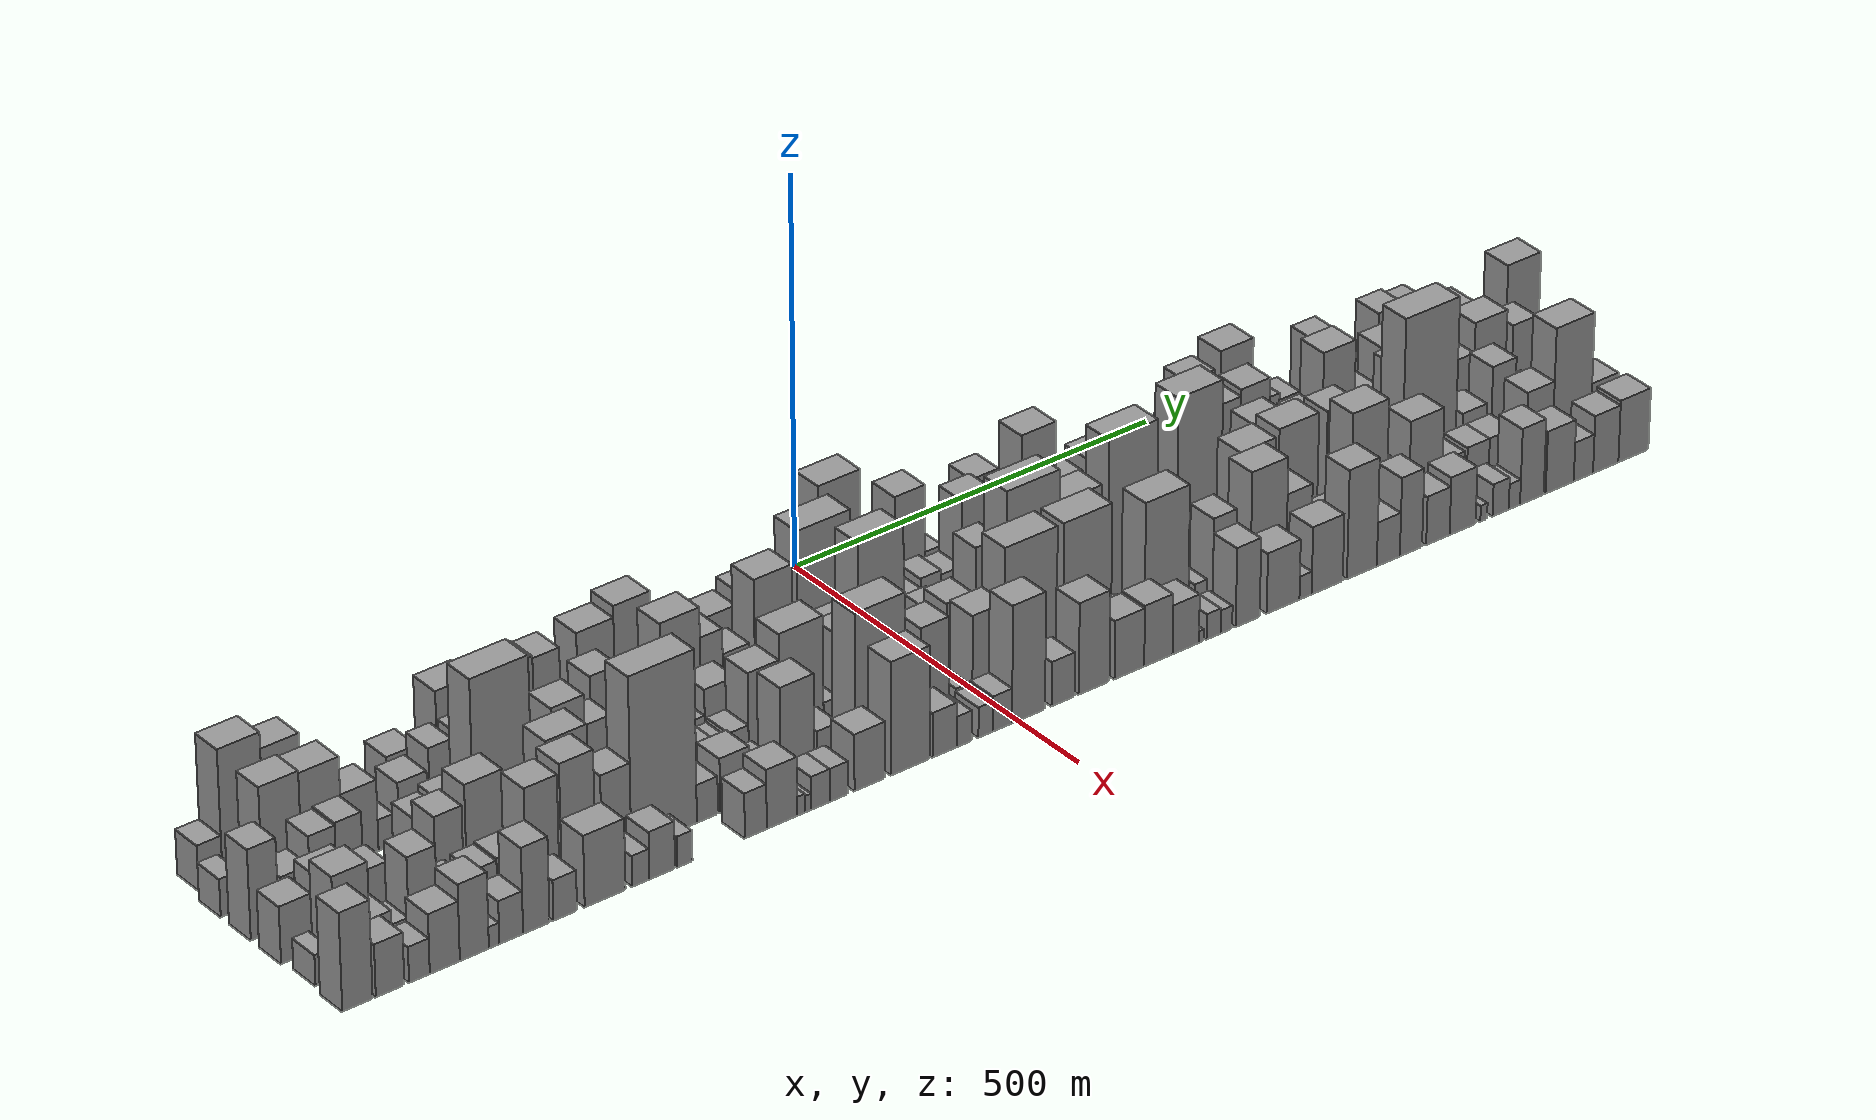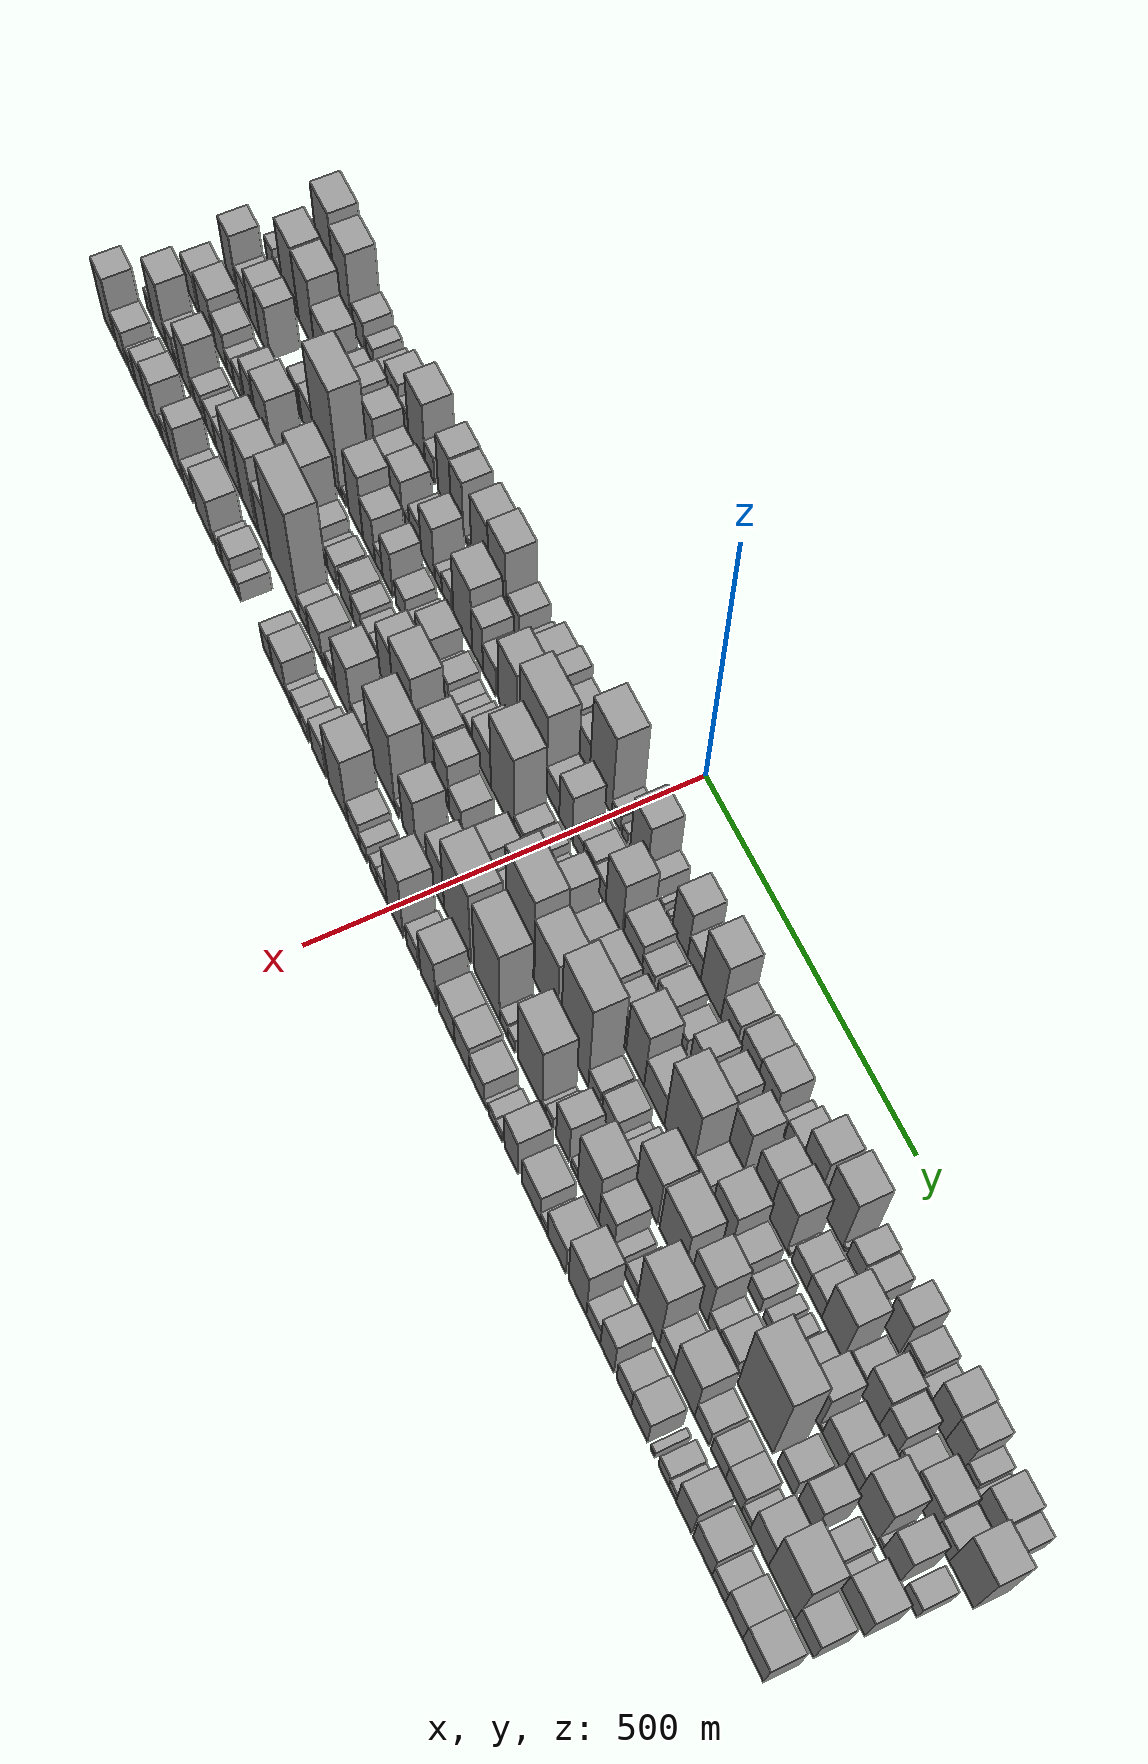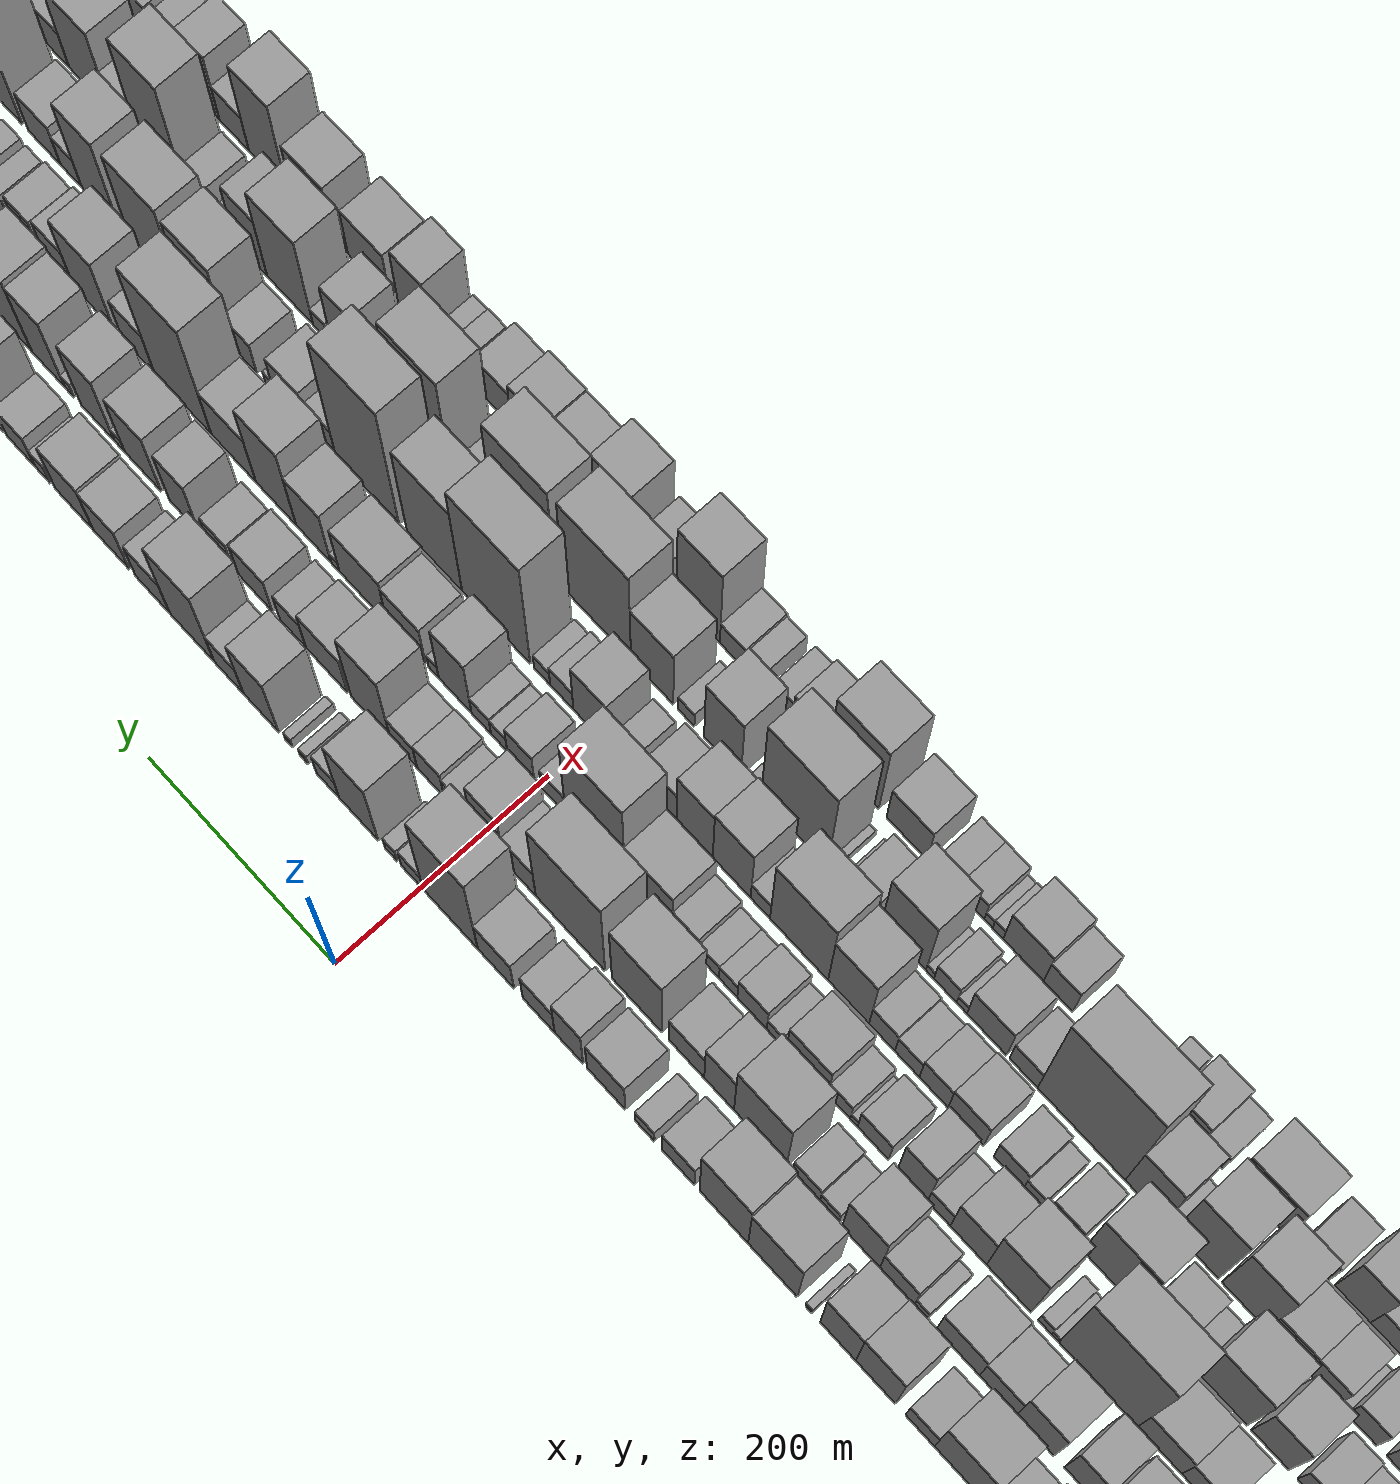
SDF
<sdf version="1.6">
 <world name="default">
  <scene>
   <sky><clouds><speed>12</speed></clouds></sky>
   <ambient>0.4 0.4 0.4 1</ambient>
   <background>0.7 0.7 0.7 1</background>
   <shadows>1</shadows>
  </scene>
  <gravity>0 0 -9.8066</gravity>
  <magnetic_field>6e-06 2.3e-05 -4.2e-05</magnetic_field>
  <physics default="0" name="default_physics" type="ode">
   <ode>
    <solver>
     <type>quick</type>
     <iters>10</iters>
     <sor>1.0</sor>
     <use_dynamic_moi_rescaling>0</use_dynamic_moi_rescaling>
    </solver>
    <constraints>
     <cfm>0</cfm>
     <erp>0.2</erp>
     <contact_max_correcting_vel>100</contact_max_correcting_vel>
     <contact_surface_layer>0.001</contact_surface_layer>
    </constraints>
   </ode>
   <max_step_size>0.004</max_step_size>
   <real_time_factor>1</real_time_factor>
   <real_time_update_rate>250</real_time_update_rate>
  </physics>
  <light name="sun" type="directional">
   <pose>0 0 10 0 0 0</pose>
   <diffuse>0.8 0.8 0.8 1</diffuse>
   <specular>0.2 0.2 0.2 1</specular>
   <attenuation>
    <range>1000</range>
    <constant>0.9</constant>
    <linear>0.01</linear>
    <quadratic>0.001</quadratic>
   </attenuation>
   <direction>-0.5 0.1 -0.9</direction>
  </light>
  <model name="building_1">
   <static>1</static>
   <pose>100.0000 -864.7257 0 0.000000 0.000000 0.000000</pose>
   <link name="link">
    <pose>0 0 28.50 0 0 0</pose>
    <collision name="collision"><geometry><box><size>40.0000 30.5486 57.0000</size></box></geometry></collision>
    <visual name="visual">
     <cast_shadows>0</cast_shadows>
     <geometry><box><size>40.0000 30.5486 57.0000</size></box></geometry>
     <material>
      <script>
       <uri>model://grey_wall/materials/scripts</uri>
       <uri>model://grey_wall/materials/textures</uri>
       <name>vrc/grey_wall</name>
      </script>
     </material>
    </visual>
   </link>
  </model>
  <model name="building_2">
   <static>1</static>
   <pose>100.0000 -822.4458 0 0.000000 0.000000 0.000000</pose>
   <link name="link">
    <pose>0 0 82.50 0 0 0</pose>
    <collision name="collision"><geometry><box><size>40.0000 54.0111 165.0000</size></box></geometry></collision>
    <visual name="visual">
     <cast_shadows>0</cast_shadows>
     <geometry><box><size>40.0000 54.0111 165.0000</size></box></geometry>
     <material>
      <script>
       <uri>model://grey_wall/materials/scripts</uri>
       <uri>model://grey_wall/materials/textures</uri>
       <name>vrc/grey_wall</name>
      </script>
     </material>
    </visual>
   </link>
  </model>
  <model name="building_3">
   <static>1</static>
   <pose>100.0000 -770.7821 0 0.000000 0.000000 0.000000</pose>
   <link name="link">
    <pose>0 0 72.00 0 0 0</pose>
    <collision name="collision"><geometry><box><size>40.0000 49.3164 144.0000</size></box></geometry></collision>
    <visual name="visual">
     <cast_shadows>0</cast_shadows>
     <geometry><box><size>40.0000 49.3164 144.0000</size></box></geometry>
     <material>
      <script>
       <uri>model://grey_wall/materials/scripts</uri>
       <uri>model://grey_wall/materials/textures</uri>
       <name>vrc/grey_wall</name>
      </script>
     </material>
    </visual>
   </link>
  </model>
  <model name="building_4">
   <static>1</static>
   <pose>100.0000 -721.9472 0 0.000000 0.000000 0.000000</pose>
   <link name="link">
    <pose>0 0 30.00 0 0 0</pose>
    <collision name="collision"><geometry><box><size>40.0000 34.3533 60.0000</size></box></geometry></collision>
    <visual name="visual">
     <cast_shadows>0</cast_shadows>
     <geometry><box><size>40.0000 34.3533 60.0000</size></box></geometry>
     <material>
      <script>
       <uri>model://grey_wall/materials/scripts</uri>
       <uri>model://grey_wall/materials/textures</uri>
       <name>vrc/grey_wall</name>
      </script>
     </material>
    </visual>
   </link>
  </model>
  <model name="building_5">
   <static>1</static>
   <pose>100.0000 -687.0318 0 0.000000 0.000000 0.000000</pose>
   <link name="link">
    <pose>0 0 21.00 0 0 0</pose>
    <collision name="collision"><geometry><box><size>40.0000 21.4775 42.0000</size></box></geometry></collision>
    <visual name="visual">
     <cast_shadows>0</cast_shadows>
     <geometry><box><size>40.0000 21.4775 42.0000</size></box></geometry>
     <material>
      <script>
       <uri>model://grey_wall/materials/scripts</uri>
       <uri>model://grey_wall/materials/textures</uri>
       <name>vrc/grey_wall</name>
      </script>
     </material>
    </visual>
   </link>
  </model>
  <model name="building_6">
   <static>1</static>
   <pose>100.0000 -655.8517 0 0.000000 0.000000 0.000000</pose>
   <link name="link">
    <pose>0 0 18.00 0 0 0</pose>
    <collision name="collision"><geometry><box><size>40.0000 20.8827 36.0000</size></box></geometry></collision>
    <visual name="visual">
     <cast_shadows>0</cast_shadows>
     <geometry><box><size>40.0000 20.8827 36.0000</size></box></geometry>
     <material>
      <script>
       <uri>model://grey_wall/materials/scripts</uri>
       <uri>model://grey_wall/materials/textures</uri>
       <name>vrc/grey_wall</name>
      </script>
     </material>
    </visual>
   </link>
  </model>
  <model name="building_7">
   <static>1</static>
   <pose>100.0000 -616.6868 0 0.000000 0.000000 0.000000</pose>
   <link name="link">
    <pose>0 0 34.50 0 0 0</pose>
    <collision name="collision"><geometry><box><size>40.0000 39.4469 69.0000</size></box></geometry></collision>
    <visual name="visual">
     <cast_shadows>0</cast_shadows>
     <geometry><box><size>40.0000 39.4469 69.0000</size></box></geometry>
     <material>
      <script>
       <uri>model://grey_wall/materials/scripts</uri>
       <uri>model://grey_wall/materials/textures</uri>
       <name>vrc/grey_wall</name>
      </script>
     </material>
    </visual>
   </link>
  </model>
  <model name="building_8">
   <static>1</static>
   <pose>100.0000 -583.9512 0 0.000000 0.000000 0.000000</pose>
   <link name="link">
    <pose>0 0 22.50 0 0 0</pose>
    <collision name="collision"><geometry><box><size>40.0000 26.0243 45.0000</size></box></geometry></collision>
    <visual name="visual">
     <cast_shadows>0</cast_shadows>
     <geometry><box><size>40.0000 26.0243 45.0000</size></box></geometry>
     <material>
      <script>
       <uri>model://grey_wall/materials/scripts</uri>
       <uri>model://grey_wall/materials/textures</uri>
       <name>vrc/grey_wall</name>
      </script>
     </material>
    </visual>
   </link>
  </model>
  <model name="building_9">
   <static>1</static>
   <pose>100.0000 -545.9353 0 0.000000 0.000000 0.000000</pose>
   <link name="link">
    <pose>0 0 63.00 0 0 0</pose>
    <collision name="collision"><geometry><box><size>40.0000 50.0075 126.0000</size></box></geometry></collision>
    <visual name="visual">
     <cast_shadows>0</cast_shadows>
     <geometry><box><size>40.0000 50.0075 126.0000</size></box></geometry>
     <material>
      <script>
       <uri>model://grey_wall/materials/scripts</uri>
       <uri>model://grey_wall/materials/textures</uri>
       <name>vrc/grey_wall</name>
      </script>
     </material>
    </visual>
   </link>
  </model>
  <model name="building_10">
   <static>1</static>
   <pose>100.0000 -506.7695 0 0.000000 0.000000 0.000000</pose>
   <link name="link">
    <pose>0 0 27.00 0 0 0</pose>
    <collision name="collision"><geometry><box><size>40.0000 28.3243 54.0000</size></box></geometry></collision>
    <visual name="visual">
     <cast_shadows>0</cast_shadows>
     <geometry><box><size>40.0000 28.3243 54.0000</size></box></geometry>
     <material>
      <script>
       <uri>model://grey_wall/materials/scripts</uri>
       <uri>model://grey_wall/materials/textures</uri>
       <name>vrc/grey_wall</name>
      </script>
     </material>
    </visual>
   </link>
  </model>
  <model name="building_11">
   <static>1</static>
   <pose>100.0000 -463.1735 0 0.000000 0.000000 0.000000</pose>
   <link name="link">
    <pose>0 0 60.00 0 0 0</pose>
    <collision name="collision"><geometry><box><size>40.0000 38.8676 120.0000</size></box></geometry></collision>
    <visual name="visual">
     <cast_shadows>0</cast_shadows>
     <geometry><box><size>40.0000 38.8676 120.0000</size></box></geometry>
     <material>
      <script>
       <uri>model://grey_wall/materials/scripts</uri>
       <uri>model://grey_wall/materials/textures</uri>
       <name>vrc/grey_wall</name>
      </script>
     </material>
    </visual>
   </link>
  </model>
  <model name="building_12">
   <static>1</static>
   <pose>100.0000 -426.0190 0 0.000000 0.000000 0.000000</pose>
   <link name="link">
    <pose>0 0 58.50 0 0 0</pose>
    <collision name="collision"><geometry><box><size>40.0000 35.4414 117.0000</size></box></geometry></collision>
    <visual name="visual">
     <cast_shadows>0</cast_shadows>
     <geometry><box><size>40.0000 35.4414 117.0000</size></box></geometry>
     <material>
      <script>
       <uri>model://grey_wall/materials/scripts</uri>
       <uri>model://grey_wall/materials/textures</uri>
       <name>vrc/grey_wall</name>
      </script>
     </material>
    </visual>
   </link>
  </model>
  <model name="building_13">
   <static>1</static>
   <pose>100.0000 -396.9022 0 0.000000 0.000000 0.000000</pose>
   <link name="link">
    <pose>0 0 7.50 0 0 0</pose>
    <collision name="collision"><geometry><box><size>40.0000 6.7922 15.0000</size></box></geometry></collision>
    <visual name="visual">
     <cast_shadows>0</cast_shadows>
     <geometry><box><size>40.0000 6.7922 15.0000</size></box></geometry>
     <material>
      <script>
       <uri>model://grey_wall/materials/scripts</uri>
       <uri>model://grey_wall/materials/textures</uri>
       <name>vrc/grey_wall</name>
      </script>
     </material>
    </visual>
   </link>
  </model>
  <model name="building_14">
   <static>1</static>
   <pose>100.0000 -360.7887 0 0.000000 0.000000 0.000000</pose>
   <link name="link">
    <pose>0 0 63.00 0 0 0</pose>
    <collision name="collision"><geometry><box><size>40.0000 49.4349 126.0000</size></box></geometry></collision>
    <visual name="visual">
     <cast_shadows>0</cast_shadows>
     <geometry><box><size>40.0000 49.4349 126.0000</size></box></geometry>
     <material>
      <script>
       <uri>model://grey_wall/materials/scripts</uri>
       <uri>model://grey_wall/materials/textures</uri>
       <name>vrc/grey_wall</name>
      </script>
     </material>
    </visual>
   </link>
  </model>
  <model name="building_15">
   <static>1</static>
   <pose>100.0000 -311.6712 0 0.000000 0.000000 0.000000</pose>
   <link name="link">
    <pose>0 0 70.50 0 0 0</pose>
    <collision name="collision"><geometry><box><size>40.0000 48.8001 141.0000</size></box></geometry></collision>
    <visual name="visual">
     <cast_shadows>0</cast_shadows>
     <geometry><box><size>40.0000 48.8001 141.0000</size></box></geometry>
     <material>
      <script>
       <uri>model://grey_wall/materials/scripts</uri>
       <uri>model://grey_wall/materials/textures</uri>
       <name>vrc/grey_wall</name>
      </script>
     </material>
    </visual>
   </link>
  </model>
  <model name="building_16">
   <static>1</static>
   <pose>100.0000 -265.8788 0 0.000000 0.000000 0.000000</pose>
   <link name="link">
    <pose>0 0 30.00 0 0 0</pose>
    <collision name="collision"><geometry><box><size>40.0000 32.7848 60.0000</size></box></geometry></collision>
    <visual name="visual">
     <cast_shadows>0</cast_shadows>
     <geometry><box><size>40.0000 32.7848 60.0000</size></box></geometry>
     <material>
      <script>
       <uri>model://grey_wall/materials/scripts</uri>
       <uri>model://grey_wall/materials/textures</uri>
       <name>vrc/grey_wall</name>
      </script>
     </material>
    </visual>
   </link>
  </model>
  <model name="building_17">
   <static>1</static>
   <pose>100.0000 -231.6135 0 0.000000 0.000000 0.000000</pose>
   <link name="link">
    <pose>0 0 16.50 0 0 0</pose>
    <collision name="collision"><geometry><box><size>40.0000 19.7459 33.0000</size></box></geometry></collision>
    <visual name="visual">
     <cast_shadows>0</cast_shadows>
     <geometry><box><size>40.0000 19.7459 33.0000</size></box></geometry>
     <material>
      <script>
       <uri>model://grey_wall/materials/scripts</uri>
       <uri>model://grey_wall/materials/textures</uri>
       <name>vrc/grey_wall</name>
      </script>
     </material>
    </visual>
   </link>
  </model>
  <model name="building_18">
   <static>1</static>
   <pose>100.0000 -192.0547 0 0.000000 0.000000 0.000000</pose>
   <link name="link">
    <pose>0 0 39.00 0 0 0</pose>
    <collision name="collision"><geometry><box><size>40.0000 39.3718 78.0000</size></box></geometry></collision>
    <visual name="visual">
     <cast_shadows>0</cast_shadows>
     <geometry><box><size>40.0000 39.3718 78.0000</size></box></geometry>
     <material>
      <script>
       <uri>model://grey_wall/materials/scripts</uri>
       <uri>model://grey_wall/materials/textures</uri>
       <name>vrc/grey_wall</name>
      </script>
     </material>
    </visual>
   </link>
  </model>
  <model name="building_19">
   <static>1</static>
   <pose>100.0000 -153.6469 0 0.000000 0.000000 0.000000</pose>
   <link name="link">
    <pose>0 0 46.50 0 0 0</pose>
    <collision name="collision"><geometry><box><size>40.0000 29.4439 93.0000</size></box></geometry></collision>
    <visual name="visual">
     <cast_shadows>0</cast_shadows>
     <geometry><box><size>40.0000 29.4439 93.0000</size></box></geometry>
     <material>
      <script>
       <uri>model://grey_wall/materials/scripts</uri>
       <uri>model://grey_wall/materials/textures</uri>
       <name>vrc/grey_wall</name>
      </script>
     </material>
    </visual>
   </link>
  </model>
  <model name="building_20">
   <static>1</static>
   <pose>100.0000 -122.4052 0 0.000000 0.000000 0.000000</pose>
   <link name="link">
    <pose>0 0 33.00 0 0 0</pose>
    <collision name="collision"><geometry><box><size>40.0000 33.0395 66.0000</size></box></geometry></collision>
    <visual name="visual">
     <cast_shadows>0</cast_shadows>
     <geometry><box><size>40.0000 33.0395 66.0000</size></box></geometry>
     <material>
      <script>
       <uri>model://grey_wall/materials/scripts</uri>
       <uri>model://grey_wall/materials/textures</uri>
       <name>vrc/grey_wall</name>
      </script>
     </material>
    </visual>
   </link>
  </model>
  <model name="building_21">
   <static>1</static>
   <pose>100.0000 -77.9015 0 0.000000 0.000000 0.000000</pose>
   <link name="link">
    <pose>0 0 36.00 0 0 0</pose>
    <collision name="collision"><geometry><box><size>40.0000 37.9678 72.0000</size></box></geometry></collision>
    <visual name="visual">
     <cast_shadows>0</cast_shadows>
     <geometry><box><size>40.0000 37.9678 72.0000</size></box></geometry>
     <material>
      <script>
       <uri>model://grey_wall/materials/scripts</uri>
       <uri>model://grey_wall/materials/textures</uri>
       <name>vrc/grey_wall</name>
      </script>
     </material>
    </visual>
   </link>
  </model>
  <model name="building_22">
   <static>1</static>
   <pose>100.0000 -30.0973 0 0.000000 0.000000 0.000000</pose>
   <link name="link">
    <pose>0 0 93.00 0 0 0</pose>
    <collision name="collision"><geometry><box><size>40.0000 57.6407 186.0000</size></box></geometry></collision>
    <visual name="visual">
     <cast_shadows>0</cast_shadows>
     <geometry><box><size>40.0000 57.6407 186.0000</size></box></geometry>
     <material>
      <script>
       <uri>model://grey_wall/materials/scripts</uri>
       <uri>model://grey_wall/materials/textures</uri>
       <name>vrc/grey_wall</name>
      </script>
     </material>
    </visual>
   </link>
  </model>
  <model name="building_23">
   <static>1</static>
   <pose>100.0000 10.3468 0 0.000000 0.000000 0.000000</pose>
   <link name="link">
    <pose>0 0 19.50 0 0 0</pose>
    <collision name="collision"><geometry><box><size>40.0000 23.2474 39.0000</size></box></geometry></collision>
    <visual name="visual">
     <cast_shadows>0</cast_shadows>
     <geometry><box><size>40.0000 23.2474 39.0000</size></box></geometry>
     <material>
      <script>
       <uri>model://grey_wall/materials/scripts</uri>
       <uri>model://grey_wall/materials/textures</uri>
       <name>vrc/grey_wall</name>
      </script>
     </material>
    </visual>
   </link>
  </model>
  <model name="building_24">
   <static>1</static>
   <pose>100.0000 32.5815 0 0.000000 0.000000 0.000000</pose>
   <link name="link">
    <pose>0 0 13.50 0 0 0</pose>
    <collision name="collision"><geometry><box><size>40.0000 13.2220 27.0000</size></box></geometry></collision>
    <visual name="visual">
     <cast_shadows>0</cast_shadows>
     <geometry><box><size>40.0000 13.2220 27.0000</size></box></geometry>
     <material>
      <script>
       <uri>model://grey_wall/materials/scripts</uri>
       <uri>model://grey_wall/materials/textures</uri>
       <name>vrc/grey_wall</name>
      </script>
     </material>
    </visual>
   </link>
  </model>
  <model name="building_25">
   <static>1</static>
   <pose>100.0000 67.2017 0 0.000000 0.000000 0.000000</pose>
   <link name="link">
    <pose>0 0 66.00 0 0 0</pose>
    <collision name="collision"><geometry><box><size>40.0000 42.0183 132.0000</size></box></geometry></collision>
    <visual name="visual">
     <cast_shadows>0</cast_shadows>
     <geometry><box><size>40.0000 42.0183 132.0000</size></box></geometry>
     <material>
      <script>
       <uri>model://grey_wall/materials/scripts</uri>
       <uri>model://grey_wall/materials/textures</uri>
       <name>vrc/grey_wall</name>
      </script>
     </material>
    </visual>
   </link>
  </model>
  <model name="building_26">
   <static>1</static>
   <pose>100.0000 100.3961 0 0.000000 0.000000 0.000000</pose>
   <link name="link">
    <pose>0 0 22.50 0 0 0</pose>
    <collision name="collision"><geometry><box><size>40.0000 24.3704 45.0000</size></box></geometry></collision>
    <visual name="visual">
     <cast_shadows>0</cast_shadows>
     <geometry><box><size>40.0000 24.3704 45.0000</size></box></geometry>
     <material>
      <script>
       <uri>model://grey_wall/materials/scripts</uri>
       <uri>model://grey_wall/materials/textures</uri>
       <name>vrc/grey_wall</name>
      </script>
     </material>
    </visual>
   </link>
  </model>
  <model name="building_27">
   <static>1</static>
   <pose>100.0000 125.8456 0 0.000000 0.000000 0.000000</pose>
   <link name="link">
    <pose>0 0 9.00 0 0 0</pose>
    <collision name="collision"><geometry><box><size>40.0000 8.5287 18.0000</size></box></geometry></collision>
    <visual name="visual">
     <cast_shadows>0</cast_shadows>
     <geometry><box><size>40.0000 8.5287 18.0000</size></box></geometry>
     <material>
      <script>
       <uri>model://grey_wall/materials/scripts</uri>
       <uri>model://grey_wall/materials/textures</uri>
       <name>vrc/grey_wall</name>
      </script>
     </material>
    </visual>
   </link>
  </model>
  <model name="building_28">
   <static>1</static>
   <pose>100.0000 142.0890 0 0.000000 0.000000 0.000000</pose>
   <link name="link">
    <pose>0 0 9.00 0 0 0</pose>
    <collision name="collision"><geometry><box><size>40.0000 7.9579 18.0000</size></box></geometry></collision>
    <visual name="visual">
     <cast_shadows>0</cast_shadows>
     <geometry><box><size>40.0000 7.9579 18.0000</size></box></geometry>
     <material>
      <script>
       <uri>model://grey_wall/materials/scripts</uri>
       <uri>model://grey_wall/materials/textures</uri>
       <name>vrc/grey_wall</name>
      </script>
     </material>
    </visual>
   </link>
  </model>
  <model name="building_29">
   <static>1</static>
   <pose>100.0000 172.0794 0 0.000000 0.000000 0.000000</pose>
   <link name="link">
    <pose>0 0 57.00 0 0 0</pose>
    <collision name="collision"><geometry><box><size>40.0000 38.0229 114.0000</size></box></geometry></collision>
    <visual name="visual">
     <cast_shadows>0</cast_shadows>
     <geometry><box><size>40.0000 38.0229 114.0000</size></box></geometry>
     <material>
      <script>
       <uri>model://grey_wall/materials/scripts</uri>
       <uri>model://grey_wall/materials/textures</uri>
       <name>vrc/grey_wall</name>
      </script>
     </material>
    </visual>
   </link>
  </model>
  <model name="building_30">
   <static>1</static>
   <pose>100.0000 207.0768 0 0.000000 0.000000 0.000000</pose>
   <link name="link">
    <pose>0 0 30.00 0 0 0</pose>
    <collision name="collision"><geometry><box><size>40.0000 31.9721 60.0000</size></box></geometry></collision>
    <visual name="visual">
     <cast_shadows>0</cast_shadows>
     <geometry><box><size>40.0000 31.9721 60.0000</size></box></geometry>
     <material>
      <script>
       <uri>model://grey_wall/materials/scripts</uri>
       <uri>model://grey_wall/materials/textures</uri>
       <name>vrc/grey_wall</name>
      </script>
     </material>
    </visual>
   </link>
  </model>
  <model name="building_31">
   <static>1</static>
   <pose>100.0000 247.4784 0 0.000000 0.000000 0.000000</pose>
   <link name="link">
    <pose>0 0 72.00 0 0 0</pose>
    <collision name="collision"><geometry><box><size>40.0000 48.8311 144.0000</size></box></geometry></collision>
    <visual name="visual">
     <cast_shadows>0</cast_shadows>
     <geometry><box><size>40.0000 48.8311 144.0000</size></box></geometry>
     <material>
      <script>
       <uri>model://grey_wall/materials/scripts</uri>
       <uri>model://grey_wall/materials/textures</uri>
       <name>vrc/grey_wall</name>
      </script>
     </material>
    </visual>
   </link>
  </model>
  <model name="building_32">
   <static>1</static>
   <pose>100.0000 290.9465 0 0.000000 0.000000 0.000000</pose>
   <link name="link">
    <pose>0 0 33.00 0 0 0</pose>
    <collision name="collision"><geometry><box><size>40.0000 38.1051 66.0000</size></box></geometry></collision>
    <visual name="visual">
     <cast_shadows>0</cast_shadows>
     <geometry><box><size>40.0000 38.1051 66.0000</size></box></geometry>
     <material>
      <script>
       <uri>model://grey_wall/materials/scripts</uri>
       <uri>model://grey_wall/materials/textures</uri>
       <name>vrc/grey_wall</name>
      </script>
     </material>
    </visual>
   </link>
  </model>
  <model name="building_33">
   <static>1</static>
   <pose>100.0000 336.8426 0 0.000000 0.000000 0.000000</pose>
   <link name="link">
    <pose>0 0 39.00 0 0 0</pose>
    <collision name="collision"><geometry><box><size>40.0000 39.6870 78.0000</size></box></geometry></collision>
    <visual name="visual">
     <cast_shadows>0</cast_shadows>
     <geometry><box><size>40.0000 39.6870 78.0000</size></box></geometry>
     <material>
      <script>
       <uri>model://grey_wall/materials/scripts</uri>
       <uri>model://grey_wall/materials/textures</uri>
       <name>vrc/grey_wall</name>
      </script>
     </material>
    </visual>
   </link>
  </model>
  <model name="building_34">
   <static>1</static>
   <pose>100.0000 377.9563 0 0.000000 0.000000 0.000000</pose>
   <link name="link">
    <pose>0 0 42.00 0 0 0</pose>
    <collision name="collision"><geometry><box><size>40.0000 42.5406 84.0000</size></box></geometry></collision>
    <visual name="visual">
     <cast_shadows>0</cast_shadows>
     <geometry><box><size>40.0000 42.5406 84.0000</size></box></geometry>
     <material>
      <script>
       <uri>model://grey_wall/materials/scripts</uri>
       <uri>model://grey_wall/materials/textures</uri>
       <name>vrc/grey_wall</name>
      </script>
     </material>
    </visual>
   </link>
  </model>
  <model name="building_35">
   <static>1</static>
   <pose>100.0000 413.5718 0 0.000000 0.000000 0.000000</pose>
   <link name="link">
    <pose>0 0 16.50 0 0 0</pose>
    <collision name="collision"><geometry><box><size>40.0000 16.6904 33.0000</size></box></geometry></collision>
    <visual name="visual">
     <cast_shadows>0</cast_shadows>
     <geometry><box><size>40.0000 16.6904 33.0000</size></box></geometry>
     <material>
      <script>
       <uri>model://grey_wall/materials/scripts</uri>
       <uri>model://grey_wall/materials/textures</uri>
       <name>vrc/grey_wall</name>
      </script>
     </material>
    </visual>
   </link>
  </model>
  <model name="building_36">
   <static>1</static>
   <pose>100.0000 437.9876 0 0.000000 0.000000 0.000000</pose>
   <link name="link">
    <pose>0 0 28.50 0 0 0</pose>
    <collision name="collision"><geometry><box><size>40.0000 32.1411 57.0000</size></box></geometry></collision>
    <visual name="visual">
     <cast_shadows>0</cast_shadows>
     <geometry><box><size>40.0000 32.1411 57.0000</size></box></geometry>
     <material>
      <script>
       <uri>model://grey_wall/materials/scripts</uri>
       <uri>model://grey_wall/materials/textures</uri>
       <name>vrc/grey_wall</name>
      </script>
     </material>
    </visual>
   </link>
  </model>
  <model name="building_37">
   <static>1</static>
   <pose>100.0000 478.6781 0 0.000000 0.000000 0.000000</pose>
   <link name="link">
    <pose>0 0 63.00 0 0 0</pose>
    <collision name="collision"><geometry><box><size>40.0000 41.2398 126.0000</size></box></geometry></collision>
    <visual name="visual">
     <cast_shadows>0</cast_shadows>
     <geometry><box><size>40.0000 41.2398 126.0000</size></box></geometry>
     <material>
      <script>
       <uri>model://grey_wall/materials/scripts</uri>
       <uri>model://grey_wall/materials/textures</uri>
       <name>vrc/grey_wall</name>
      </script>
     </material>
    </visual>
   </link>
  </model>
  <model name="building_38">
   <static>1</static>
   <pose>100.0000 530.9011 0 0.000000 0.000000 0.000000</pose>
   <link name="link">
    <pose>0 0 73.50 0 0 0</pose>
    <collision name="collision"><geometry><box><size>40.0000 47.2061 147.0000</size></box></geometry></collision>
    <visual name="visual">
     <cast_shadows>0</cast_shadows>
     <geometry><box><size>40.0000 47.2061 147.0000</size></box></geometry>
     <material>
      <script>
       <uri>model://grey_wall/materials/scripts</uri>
       <uri>model://grey_wall/materials/textures</uri>
       <name>vrc/grey_wall</name>
      </script>
     </material>
    </visual>
   </link>
  </model>
  <model name="building_39">
   <static>1</static>
   <pose>100.0000 557.7680 0 0.000000 0.000000 0.000000</pose>
   <link name="link">
    <pose>0 0 7.50 0 0 0</pose>
    <collision name="collision"><geometry><box><size>40.0000 6.5279 15.0000</size></box></geometry></collision>
    <visual name="visual">
     <cast_shadows>0</cast_shadows>
     <geometry><box><size>40.0000 6.5279 15.0000</size></box></geometry>
     <material>
      <script>
       <uri>model://grey_wall/materials/scripts</uri>
       <uri>model://grey_wall/materials/textures</uri>
       <name>vrc/grey_wall</name>
      </script>
     </material>
    </visual>
   </link>
  </model>
  <model name="building_40">
   <static>1</static>
   <pose>100.0000 579.1528 0 0.000000 0.000000 0.000000</pose>
   <link name="link">
    <pose>0 0 30.00 0 0 0</pose>
    <collision name="collision"><geometry><box><size>40.0000 30.2417 60.0000</size></box></geometry></collision>
    <visual name="visual">
     <cast_shadows>0</cast_shadows>
     <geometry><box><size>40.0000 30.2417 60.0000</size></box></geometry>
     <material>
      <script>
       <uri>model://grey_wall/materials/scripts</uri>
       <uri>model://grey_wall/materials/textures</uri>
       <name>vrc/grey_wall</name>
      </script>
     </material>
    </visual>
   </link>
  </model>
  <model name="building_41">
   <static>1</static>
   <pose>100.0000 609.5733 0 0.000000 0.000000 0.000000</pose>
   <link name="link">
    <pose>0 0 25.50 0 0 0</pose>
    <collision name="collision"><geometry><box><size>40.0000 30.5992 51.0000</size></box></geometry></collision>
    <visual name="visual">
     <cast_shadows>0</cast_shadows>
     <geometry><box><size>40.0000 30.5992 51.0000</size></box></geometry>
     <material>
      <script>
       <uri>model://grey_wall/materials/scripts</uri>
       <uri>model://grey_wall/materials/textures</uri>
       <name>vrc/grey_wall</name>
      </script>
     </material>
    </visual>
   </link>
  </model>
  <model name="building_42">
   <static>1</static>
   <pose>100.0000 639.3456 0 0.000000 0.000000 0.000000</pose>
   <link name="link">
    <pose>0 0 9.00 0 0 0</pose>
    <collision name="collision"><geometry><box><size>40.0000 8.9454 18.0000</size></box></geometry></collision>
    <visual name="visual">
     <cast_shadows>0</cast_shadows>
     <geometry><box><size>40.0000 8.9454 18.0000</size></box></geometry>
     <material>
      <script>
       <uri>model://grey_wall/materials/scripts</uri>
       <uri>model://grey_wall/materials/textures</uri>
       <name>vrc/grey_wall</name>
      </script>
     </material>
    </visual>
   </link>
  </model>
  <model name="building_43">
   <static>1</static>
   <pose>100.0000 661.3538 0 0.000000 0.000000 0.000000</pose>
   <link name="link">
    <pose>0 0 55.50 0 0 0</pose>
    <collision name="collision"><geometry><box><size>40.0000 35.0709 111.0000</size></box></geometry></collision>
    <visual name="visual">
     <cast_shadows>0</cast_shadows>
     <geometry><box><size>40.0000 35.0709 111.0000</size></box></geometry>
     <material>
      <script>
       <uri>model://grey_wall/materials/scripts</uri>
       <uri>model://grey_wall/materials/textures</uri>
       <name>vrc/grey_wall</name>
      </script>
     </material>
    </visual>
   </link>
  </model>
  <model name="building_44">
   <static>1</static>
   <pose>100.0000 699.3466 0 0.000000 0.000000 0.000000</pose>
   <link name="link">
    <pose>0 0 31.50 0 0 0</pose>
    <collision name="collision"><geometry><box><size>40.0000 34.9148 63.0000</size></box></geometry></collision>
    <visual name="visual">
     <cast_shadows>0</cast_shadows>
     <geometry><box><size>40.0000 34.9148 63.0000</size></box></geometry>
     <material>
      <script>
       <uri>model://grey_wall/materials/scripts</uri>
       <uri>model://grey_wall/materials/textures</uri>
       <name>vrc/grey_wall</name>
      </script>
     </material>
    </visual>
   </link>
  </model>
  <model name="building_45">
   <static>1</static>
   <pose>100.0000 727.9116 0 0.000000 0.000000 0.000000</pose>
   <link name="link">
    <pose>0 0 19.50 0 0 0</pose>
    <collision name="collision"><geometry><box><size>40.0000 22.2151 39.0000</size></box></geometry></collision>
    <visual name="visual">
     <cast_shadows>0</cast_shadows>
     <geometry><box><size>40.0000 22.2151 39.0000</size></box></geometry>
     <material>
      <script>
       <uri>model://grey_wall/materials/scripts</uri>
       <uri>model://grey_wall/materials/textures</uri>
       <name>vrc/grey_wall</name>
      </script>
     </material>
    </visual>
   </link>
  </model>
  <model name="building_46">
   <static>1</static>
   <pose>100.0000 757.7338 0 0.000000 0.000000 0.000000</pose>
   <link name="link">
    <pose>0 0 55.50 0 0 0</pose>
    <collision name="collision"><geometry><box><size>40.0000 37.4294 111.0000</size></box></geometry></collision>
    <visual name="visual">
     <cast_shadows>0</cast_shadows>
     <geometry><box><size>40.0000 37.4294 111.0000</size></box></geometry>
     <material>
      <script>
       <uri>model://grey_wall/materials/scripts</uri>
       <uri>model://grey_wall/materials/textures</uri>
       <name>vrc/grey_wall</name>
      </script>
     </material>
    </visual>
   </link>
  </model>
  <model name="building_47">
   <static>1</static>
   <pose>100.0000 793.2924 0 0.000000 0.000000 0.000000</pose>
   <link name="link">
    <pose>0 0 52.50 0 0 0</pose>
    <collision name="collision"><geometry><box><size>40.0000 33.6877 105.0000</size></box></geometry></collision>
    <visual name="visual">
     <cast_shadows>0</cast_shadows>
     <geometry><box><size>40.0000 33.6877 105.0000</size></box></geometry>
     <material>
      <script>
       <uri>model://grey_wall/materials/scripts</uri>
       <uri>model://grey_wall/materials/textures</uri>
       <name>vrc/grey_wall</name>
      </script>
     </material>
    </visual>
   </link>
  </model>
  <model name="building_48">
   <static>1</static>
   <pose>100.0000 822.3239 0 0.000000 0.000000 0.000000</pose>
   <link name="link">
    <pose>0 0 22.50 0 0 0</pose>
    <collision name="collision"><geometry><box><size>40.0000 24.3753 45.0000</size></box></geometry></collision>
    <visual name="visual">
     <cast_shadows>0</cast_shadows>
     <geometry><box><size>40.0000 24.3753 45.0000</size></box></geometry>
     <material>
      <script>
       <uri>model://grey_wall/materials/scripts</uri>
       <uri>model://grey_wall/materials/textures</uri>
       <name>vrc/grey_wall</name>
      </script>
     </material>
    </visual>
   </link>
  </model>
  <model name="building_49">
   <static>1</static>
   <pose>100.0000 838.6322 0 0.000000 0.000000 0.000000</pose>
   <link name="link">
    <pose>0 0 9.00 0 0 0</pose>
    <collision name="collision"><geometry><box><size>40.0000 8.2412 18.0000</size></box></geometry></collision>
    <visual name="visual">
     <cast_shadows>0</cast_shadows>
     <geometry><box><size>40.0000 8.2412 18.0000</size></box></geometry>
     <material>
      <script>
       <uri>model://grey_wall/materials/scripts</uri>
       <uri>model://grey_wall/materials/textures</uri>
       <name>vrc/grey_wall</name>
      </script>
     </material>
    </visual>
   </link>
  </model>
  <model name="building_50">
   <static>1</static>
   <pose>100.0000 862.5856 0 0.000000 0.000000 0.000000</pose>
   <link name="link">
    <pose>0 0 37.50 0 0 0</pose>
    <collision name="collision"><geometry><box><size>40.0000 39.6657 75.0000</size></box></geometry></collision>
    <visual name="visual">
     <cast_shadows>0</cast_shadows>
     <geometry><box><size>40.0000 39.6657 75.0000</size></box></geometry>
     <material>
      <script>
       <uri>model://grey_wall/materials/scripts</uri>
       <uri>model://grey_wall/materials/textures</uri>
       <name>vrc/grey_wall</name>
      </script>
     </material>
    </visual>
   </link>
  </model>
  <model name="building_51">
   <static>1</static>
   <pose>100.0000 896.2049 0 0.000000 0.000000 0.000000</pose>
   <link name="link">
    <pose>0 0 25.50 0 0 0</pose>
    <collision name="collision"><geometry><box><size>40.0000 27.5730 51.0000</size></box></geometry></collision>
    <visual name="visual">
     <cast_shadows>0</cast_shadows>
     <geometry><box><size>40.0000 27.5730 51.0000</size></box></geometry>
     <material>
      <script>
       <uri>model://grey_wall/materials/scripts</uri>
       <uri>model://grey_wall/materials/textures</uri>
       <name>vrc/grey_wall</name>
      </script>
     </material>
    </visual>
   </link>
  </model>
  <model name="building_52">
   <static>1</static>
   <pose>155.0000 -877.2453 0 0.000000 0.000000 0.000000</pose>
   <link name="link">
    <pose>0 0 24.00 0 0 0</pose>
    <collision name="collision"><geometry><box><size>40.0000 25.5093 48.0000</size></box></geometry></collision>
    <visual name="visual">
     <cast_shadows>0</cast_shadows>
     <geometry><box><size>40.0000 25.5093 48.0000</size></box></geometry>
     <material>
      <script>
       <uri>model://grey_wall/materials/scripts</uri>
       <uri>model://grey_wall/materials/textures</uri>
       <name>vrc/grey_wall</name>
      </script>
     </material>
    </visual>
   </link>
  </model>
  <model name="building_53">
   <static>1</static>
   <pose>155.0000 -847.4189 0 0.000000 0.000000 0.000000</pose>
   <link name="link">
    <pose>0 0 19.50 0 0 0</pose>
    <collision name="collision"><geometry><box><size>40.0000 22.1435 39.0000</size></box></geometry></collision>
    <visual name="visual">
     <cast_shadows>0</cast_shadows>
     <geometry><box><size>40.0000 22.1435 39.0000</size></box></geometry>
     <material>
      <script>
       <uri>model://grey_wall/materials/scripts</uri>
       <uri>model://grey_wall/materials/textures</uri>
       <name>vrc/grey_wall</name>
      </script>
     </material>
    </visual>
   </link>
  </model>
  <model name="building_54">
   <static>1</static>
   <pose>155.0000 -811.0067 0 0.000000 0.000000 0.000000</pose>
   <link name="link">
    <pose>0 0 70.50 0 0 0</pose>
    <collision name="collision"><geometry><box><size>40.0000 50.6810 141.0000</size></box></geometry></collision>
    <visual name="visual">
     <cast_shadows>0</cast_shadows>
     <geometry><box><size>40.0000 50.6810 141.0000</size></box></geometry>
     <material>
      <script>
       <uri>model://grey_wall/materials/scripts</uri>
       <uri>model://grey_wall/materials/textures</uri>
       <name>vrc/grey_wall</name>
      </script>
     </material>
    </visual>
   </link>
  </model>
  <model name="building_55">
   <static>1</static>
   <pose>155.0000 -759.9130 0 0.000000 0.000000 0.000000</pose>
   <link name="link">
    <pose>0 0 69.00 0 0 0</pose>
    <collision name="collision"><geometry><box><size>40.0000 51.5064 138.0000</size></box></geometry></collision>
    <visual name="visual">
     <cast_shadows>0</cast_shadows>
     <geometry><box><size>40.0000 51.5064 138.0000</size></box></geometry>
     <material>
      <script>
       <uri>model://grey_wall/materials/scripts</uri>
       <uri>model://grey_wall/materials/textures</uri>
       <name>vrc/grey_wall</name>
      </script>
     </material>
    </visual>
   </link>
  </model>
  <model name="building_56">
   <static>1</static>
   <pose>155.0000 -711.0327 0 0.000000 0.000000 0.000000</pose>
   <link name="link">
    <pose>0 0 45.00 0 0 0</pose>
    <collision name="collision"><geometry><box><size>40.0000 46.2541 90.0000</size></box></geometry></collision>
    <visual name="visual">
     <cast_shadows>0</cast_shadows>
     <geometry><box><size>40.0000 46.2541 90.0000</size></box></geometry>
     <material>
      <script>
       <uri>model://grey_wall/materials/scripts</uri>
       <uri>model://grey_wall/materials/textures</uri>
       <name>vrc/grey_wall</name>
      </script>
     </material>
    </visual>
   </link>
  </model>
  <model name="building_57">
   <static>1</static>
   <pose>155.0000 -677.4750 0 0.000000 0.000000 0.000000</pose>
   <link name="link">
    <pose>0 0 19.50 0 0 0</pose>
    <collision name="collision"><geometry><box><size>40.0000 20.8614 39.0000</size></box></geometry></collision>
    <visual name="visual">
     <cast_shadows>0</cast_shadows>
     <geometry><box><size>40.0000 20.8614 39.0000</size></box></geometry>
     <material>
      <script>
       <uri>model://grey_wall/materials/scripts</uri>
       <uri>model://grey_wall/materials/textures</uri>
       <name>vrc/grey_wall</name>
      </script>
     </material>
    </visual>
   </link>
  </model>
  <model name="building_58">
   <static>1</static>
   <pose>155.0000 -642.1965 0 0.000000 0.000000 0.000000</pose>
   <link name="link">
    <pose>0 0 37.50 0 0 0</pose>
    <collision name="collision"><geometry><box><size>40.0000 37.6956 75.0000</size></box></geometry></collision>
    <visual name="visual">
     <cast_shadows>0</cast_shadows>
     <geometry><box><size>40.0000 37.6956 75.0000</size></box></geometry>
     <material>
      <script>
       <uri>model://grey_wall/materials/scripts</uri>
       <uri>model://grey_wall/materials/textures</uri>
       <name>vrc/grey_wall</name>
      </script>
     </material>
    </visual>
   </link>
  </model>
  <model name="building_59">
   <static>1</static>
   <pose>155.0000 -604.8705 0 0.000000 0.000000 0.000000</pose>
   <link name="link">
    <pose>0 0 51.00 0 0 0</pose>
    <collision name="collision"><geometry><box><size>40.0000 30.9563 102.0000</size></box></geometry></collision>
    <visual name="visual">
     <cast_shadows>0</cast_shadows>
     <geometry><box><size>40.0000 30.9563 102.0000</size></box></geometry>
     <material>
      <script>
       <uri>model://grey_wall/materials/scripts</uri>
       <uri>model://grey_wall/materials/textures</uri>
       <name>vrc/grey_wall</name>
      </script>
     </material>
    </visual>
   </link>
  </model>
  <model name="building_60">
   <static>1</static>
   <pose>155.0000 -561.1471 0 0.000000 0.000000 0.000000</pose>
   <link name="link">
    <pose>0 0 51.00 0 0 0</pose>
    <collision name="collision"><geometry><box><size>40.0000 36.4905 102.0000</size></box></geometry></collision>
    <visual name="visual">
     <cast_shadows>0</cast_shadows>
     <geometry><box><size>40.0000 36.4905 102.0000</size></box></geometry>
     <material>
      <script>
       <uri>model://grey_wall/materials/scripts</uri>
       <uri>model://grey_wall/materials/textures</uri>
       <name>vrc/grey_wall</name>
      </script>
     </material>
    </visual>
   </link>
  </model>
  <model name="building_61">
   <static>1</static>
   <pose>155.0000 -525.0356 0 0.000000 0.000000 0.000000</pose>
   <link name="link">
    <pose>0 0 33.00 0 0 0</pose>
    <collision name="collision"><geometry><box><size>40.0000 35.7326 66.0000</size></box></geometry></collision>
    <visual name="visual">
     <cast_shadows>0</cast_shadows>
     <geometry><box><size>40.0000 35.7326 66.0000</size></box></geometry>
     <material>
      <script>
       <uri>model://grey_wall/materials/scripts</uri>
       <uri>model://grey_wall/materials/textures</uri>
       <name>vrc/grey_wall</name>
      </script>
     </material>
    </visual>
   </link>
  </model>
  <model name="building_62">
   <static>1</static>
   <pose>155.0000 -486.0445 0 0.000000 0.000000 0.000000</pose>
   <link name="link">
    <pose>0 0 37.50 0 0 0</pose>
    <collision name="collision"><geometry><box><size>40.0000 42.2497 75.0000</size></box></geometry></collision>
    <visual name="visual">
     <cast_shadows>0</cast_shadows>
     <geometry><box><size>40.0000 42.2497 75.0000</size></box></geometry>
     <material>
      <script>
       <uri>model://grey_wall/materials/scripts</uri>
       <uri>model://grey_wall/materials/textures</uri>
       <name>vrc/grey_wall</name>
      </script>
     </material>
    </visual>
   </link>
  </model>
  <model name="building_63">
   <static>1</static>
   <pose>155.0000 -449.4482 0 0.000000 0.000000 0.000000</pose>
   <link name="link">
    <pose>0 0 13.50 0 0 0</pose>
    <collision name="collision"><geometry><box><size>40.0000 12.9428 27.0000</size></box></geometry></collision>
    <visual name="visual">
     <cast_shadows>0</cast_shadows>
     <geometry><box><size>40.0000 12.9428 27.0000</size></box></geometry>
     <material>
      <script>
       <uri>model://grey_wall/materials/scripts</uri>
       <uri>model://grey_wall/materials/textures</uri>
       <name>vrc/grey_wall</name>
      </script>
     </material>
    </visual>
   </link>
  </model>
  <model name="building_64">
   <static>1</static>
   <pose>155.0000 -425.9013 0 0.000000 0.000000 0.000000</pose>
   <link name="link">
    <pose>0 0 30.00 0 0 0</pose>
    <collision name="collision"><geometry><box><size>40.0000 34.1510 60.0000</size></box></geometry></collision>
    <visual name="visual">
     <cast_shadows>0</cast_shadows>
     <geometry><box><size>40.0000 34.1510 60.0000</size></box></geometry>
     <material>
      <script>
       <uri>model://grey_wall/materials/scripts</uri>
       <uri>model://grey_wall/materials/textures</uri>
       <name>vrc/grey_wall</name>
      </script>
     </material>
    </visual>
   </link>
  </model>
  <model name="building_65">
   <static>1</static>
   <pose>155.0000 -389.9046 0 0.000000 0.000000 0.000000</pose>
   <link name="link">
    <pose>0 0 54.00 0 0 0</pose>
    <collision name="collision"><geometry><box><size>40.0000 37.8425 108.0000</size></box></geometry></collision>
    <visual name="visual">
     <cast_shadows>0</cast_shadows>
     <geometry><box><size>40.0000 37.8425 108.0000</size></box></geometry>
     <material>
      <script>
       <uri>model://grey_wall/materials/scripts</uri>
       <uri>model://grey_wall/materials/textures</uri>
       <name>vrc/grey_wall</name>
      </script>
     </material>
    </visual>
   </link>
  </model>
  <model name="building_66">
   <static>1</static>
   <pose>155.0000 -358.2514 0 0.000000 0.000000 0.000000</pose>
   <link name="link">
    <pose>0 0 18.00 0 0 0</pose>
    <collision name="collision"><geometry><box><size>40.0000 19.4640 36.0000</size></box></geometry></collision>
    <visual name="visual">
     <cast_shadows>0</cast_shadows>
     <geometry><box><size>40.0000 19.4640 36.0000</size></box></geometry>
     <material>
      <script>
       <uri>model://grey_wall/materials/scripts</uri>
       <uri>model://grey_wall/materials/textures</uri>
       <name>vrc/grey_wall</name>
      </script>
     </material>
    </visual>
   </link>
  </model>
  <model name="building_67">
   <static>1</static>
   <pose>155.0000 -334.8753 0 0.000000 0.000000 0.000000</pose>
   <link name="link">
    <pose>0 0 24.00 0 0 0</pose>
    <collision name="collision"><geometry><box><size>40.0000 27.2881 48.0000</size></box></geometry></collision>
    <visual name="visual">
     <cast_shadows>0</cast_shadows>
     <geometry><box><size>40.0000 27.2881 48.0000</size></box></geometry>
     <material>
      <script>
       <uri>model://grey_wall/materials/scripts</uri>
       <uri>model://grey_wall/materials/textures</uri>
       <name>vrc/grey_wall</name>
      </script>
     </material>
    </visual>
   </link>
  </model>
  <model name="building_68">
   <static>1</static>
   <pose>155.0000 -288.7077 0 0.000000 0.000000 0.000000</pose>
   <link name="link">
    <pose>0 0 69.00 0 0 0</pose>
    <collision name="collision"><geometry><box><size>40.0000 53.0472 138.0000</size></box></geometry></collision>
    <visual name="visual">
     <cast_shadows>0</cast_shadows>
     <geometry><box><size>40.0000 53.0472 138.0000</size></box></geometry>
     <material>
      <script>
       <uri>model://grey_wall/materials/scripts</uri>
       <uri>model://grey_wall/materials/textures</uri>
       <name>vrc/grey_wall</name>
      </script>
     </material>
    </visual>
   </link>
  </model>
  <model name="building_69">
   <static>1</static>
   <pose>155.0000 -247.0434 0 0.000000 0.000000 0.000000</pose>
   <link name="link">
    <pose>0 0 49.50 0 0 0</pose>
    <collision name="collision"><geometry><box><size>40.0000 30.2813 99.0000</size></box></geometry></collision>
    <visual name="visual">
     <cast_shadows>0</cast_shadows>
     <geometry><box><size>40.0000 30.2813 99.0000</size></box></geometry>
     <material>
      <script>
       <uri>model://grey_wall/materials/scripts</uri>
       <uri>model://grey_wall/materials/textures</uri>
       <name>vrc/grey_wall</name>
      </script>
     </material>
    </visual>
   </link>
  </model>
  <model name="building_70">
   <static>1</static>
   <pose>155.0000 -213.8012 0 0.000000 0.000000 0.000000</pose>
   <link name="link">
    <pose>0 0 33.00 0 0 0</pose>
    <collision name="collision"><geometry><box><size>40.0000 36.2033 66.0000</size></box></geometry></collision>
    <visual name="visual">
     <cast_shadows>0</cast_shadows>
     <geometry><box><size>40.0000 36.2033 66.0000</size></box></geometry>
     <material>
      <script>
       <uri>model://grey_wall/materials/scripts</uri>
       <uri>model://grey_wall/materials/textures</uri>
       <name>vrc/grey_wall</name>
      </script>
     </material>
    </visual>
   </link>
  </model>
  <model name="building_71">
   <static>1</static>
   <pose>155.0000 -162.9015 0 0.000000 0.000000 0.000000</pose>
   <link name="link">
    <pose>0 0 72.00 0 0 0</pose>
    <collision name="collision"><geometry><box><size>40.0000 51.5961 144.0000</size></box></geometry></collision>
    <visual name="visual">
     <cast_shadows>0</cast_shadows>
     <geometry><box><size>40.0000 51.5961 144.0000</size></box></geometry>
     <material>
      <script>
       <uri>model://grey_wall/materials/scripts</uri>
       <uri>model://grey_wall/materials/textures</uri>
       <name>vrc/grey_wall</name>
      </script>
     </material>
    </visual>
   </link>
  </model>
  <model name="building_72">
   <static>1</static>
   <pose>155.0000 -93.9543 0 0.000000 0.000000 0.000000</pose>
   <link name="link">
    <pose>0 0 91.50 0 0 0</pose>
    <collision name="collision"><geometry><box><size>40.0000 72.2982 183.0000</size></box></geometry></collision>
    <visual name="visual">
     <cast_shadows>0</cast_shadows>
     <geometry><box><size>40.0000 72.2982 183.0000</size></box></geometry>
     <material>
      <script>
       <uri>model://grey_wall/materials/scripts</uri>
       <uri>model://grey_wall/materials/textures</uri>
       <name>vrc/grey_wall</name>
      </script>
     </material>
    </visual>
   </link>
  </model>
  <model name="building_73">
   <static>1</static>
   <pose>155.0000 -41.0346 0 0.000000 0.000000 0.000000</pose>
   <link name="link">
    <pose>0 0 33.00 0 0 0</pose>
    <collision name="collision"><geometry><box><size>40.0000 33.5412 66.0000</size></box></geometry></collision>
    <visual name="visual">
     <cast_shadows>0</cast_shadows>
     <geometry><box><size>40.0000 33.5412 66.0000</size></box></geometry>
     <material>
      <script>
       <uri>model://grey_wall/materials/scripts</uri>
       <uri>model://grey_wall/materials/textures</uri>
       <name>vrc/grey_wall</name>
      </script>
     </material>
    </visual>
   </link>
  </model>
  <model name="building_74">
   <static>1</static>
   <pose>155.0000 -7.5074 0 0.000000 0.000000 0.000000</pose>
   <link name="link">
    <pose>0 0 54.00 0 0 0</pose>
    <collision name="collision"><geometry><box><size>40.0000 33.5132 108.0000</size></box></geometry></collision>
    <visual name="visual">
     <cast_shadows>0</cast_shadows>
     <geometry><box><size>40.0000 33.5132 108.0000</size></box></geometry>
     <material>
      <script>
       <uri>model://grey_wall/materials/scripts</uri>
       <uri>model://grey_wall/materials/textures</uri>
       <name>vrc/grey_wall</name>
      </script>
     </material>
    </visual>
   </link>
  </model>
  <model name="building_75">
   <static>1</static>
   <pose>155.0000 25.5011 0 0.000000 0.000000 0.000000</pose>
   <link name="link">
    <pose>0 0 22.50 0 0 0</pose>
    <collision name="collision"><geometry><box><size>40.0000 26.5037 45.0000</size></box></geometry></collision>
    <visual name="visual">
     <cast_shadows>0</cast_shadows>
     <geometry><box><size>40.0000 26.5037 45.0000</size></box></geometry>
     <material>
      <script>
       <uri>model://grey_wall/materials/scripts</uri>
       <uri>model://grey_wall/materials/textures</uri>
       <name>vrc/grey_wall</name>
      </script>
     </material>
    </visual>
   </link>
  </model>
  <model name="building_76">
   <static>1</static>
   <pose>155.0000 53.0796 0 0.000000 0.000000 0.000000</pose>
   <link name="link">
    <pose>0 0 28.50 0 0 0</pose>
    <collision name="collision"><geometry><box><size>40.0000 28.6533 57.0000</size></box></geometry></collision>
    <visual name="visual">
     <cast_shadows>0</cast_shadows>
     <geometry><box><size>40.0000 28.6533 57.0000</size></box></geometry>
     <material>
      <script>
       <uri>model://grey_wall/materials/scripts</uri>
       <uri>model://grey_wall/materials/textures</uri>
       <name>vrc/grey_wall</name>
      </script>
     </material>
    </visual>
   </link>
  </model>
  <model name="building_77">
   <static>1</static>
   <pose>155.0000 81.7268 0 0.000000 0.000000 0.000000</pose>
   <link name="link">
    <pose>0 0 25.50 0 0 0</pose>
    <collision name="collision"><geometry><box><size>40.0000 28.6413 51.0000</size></box></geometry></collision>
    <visual name="visual">
     <cast_shadows>0</cast_shadows>
     <geometry><box><size>40.0000 28.6413 51.0000</size></box></geometry>
     <material>
      <script>
       <uri>model://grey_wall/materials/scripts</uri>
       <uri>model://grey_wall/materials/textures</uri>
       <name>vrc/grey_wall</name>
      </script>
     </material>
    </visual>
   </link>
  </model>
  <model name="building_78">
   <static>1</static>
   <pose>155.0000 117.2070 0 0.000000 0.000000 0.000000</pose>
   <link name="link">
    <pose>0 0 67.50 0 0 0</pose>
    <collision name="collision"><geometry><box><size>40.0000 42.3190 135.0000</size></box></geometry></collision>
    <visual name="visual">
     <cast_shadows>0</cast_shadows>
     <geometry><box><size>40.0000 42.3190 135.0000</size></box></geometry>
     <material>
      <script>
       <uri>model://grey_wall/materials/scripts</uri>
       <uri>model://grey_wall/materials/textures</uri>
       <name>vrc/grey_wall</name>
      </script>
     </material>
    </visual>
   </link>
  </model>
  <model name="building_79">
   <static>1</static>
   <pose>155.0000 164.8329 0 0.000000 0.000000 0.000000</pose>
   <link name="link">
    <pose>0 0 37.50 0 0 0</pose>
    <collision name="collision"><geometry><box><size>40.0000 44.9328 75.0000</size></box></geometry></collision>
    <visual name="visual">
     <cast_shadows>0</cast_shadows>
     <geometry><box><size>40.0000 44.9328 75.0000</size></box></geometry>
     <material>
      <script>
       <uri>model://grey_wall/materials/scripts</uri>
       <uri>model://grey_wall/materials/textures</uri>
       <name>vrc/grey_wall</name>
      </script>
     </material>
    </visual>
   </link>
  </model>
  <model name="building_80">
   <static>1</static>
   <pose>155.0000 201.5827 0 0.000000 0.000000 0.000000</pose>
   <link name="link">
    <pose>0 0 27.00 0 0 0</pose>
    <collision name="collision"><geometry><box><size>40.0000 28.5667 54.0000</size></box></geometry></collision>
    <visual name="visual">
     <cast_shadows>0</cast_shadows>
     <geometry><box><size>40.0000 28.5667 54.0000</size></box></geometry>
     <material>
      <script>
       <uri>model://grey_wall/materials/scripts</uri>
       <uri>model://grey_wall/materials/textures</uri>
       <name>vrc/grey_wall</name>
      </script>
     </material>
    </visual>
   </link>
  </model>
  <model name="building_81">
   <static>1</static>
   <pose>155.0000 242.4506 0 0.000000 0.000000 0.000000</pose>
   <link name="link">
    <pose>0 0 33.00 0 0 0</pose>
    <collision name="collision"><geometry><box><size>40.0000 37.1691 66.0000</size></box></geometry></collision>
    <visual name="visual">
     <cast_shadows>0</cast_shadows>
     <geometry><box><size>40.0000 37.1691 66.0000</size></box></geometry>
     <material>
      <script>
       <uri>model://grey_wall/materials/scripts</uri>
       <uri>model://grey_wall/materials/textures</uri>
       <name>vrc/grey_wall</name>
      </script>
     </material>
    </visual>
   </link>
  </model>
  <model name="building_82">
   <static>1</static>
   <pose>155.0000 281.3263 0 0.000000 0.000000 0.000000</pose>
   <link name="link">
    <pose>0 0 25.50 0 0 0</pose>
    <collision name="collision"><geometry><box><size>40.0000 28.5824 51.0000</size></box></geometry></collision>
    <visual name="visual">
     <cast_shadows>0</cast_shadows>
     <geometry><box><size>40.0000 28.5824 51.0000</size></box></geometry>
     <material>
      <script>
       <uri>model://grey_wall/materials/scripts</uri>
       <uri>model://grey_wall/materials/textures</uri>
       <name>vrc/grey_wall</name>
      </script>
     </material>
    </visual>
   </link>
  </model>
  <model name="building_83">
   <static>1</static>
   <pose>155.0000 321.0863 0 0.000000 0.000000 0.000000</pose>
   <link name="link">
    <pose>0 0 46.50 0 0 0</pose>
    <collision name="collision"><geometry><box><size>40.0000 32.9375 93.0000</size></box></geometry></collision>
    <visual name="visual">
     <cast_shadows>0</cast_shadows>
     <geometry><box><size>40.0000 32.9375 93.0000</size></box></geometry>
     <material>
      <script>
       <uri>model://grey_wall/materials/scripts</uri>
       <uri>model://grey_wall/materials/textures</uri>
       <name>vrc/grey_wall</name>
      </script>
     </material>
    </visual>
   </link>
  </model>
  <model name="building_84">
   <static>1</static>
   <pose>155.0000 366.9229 0 0.000000 0.000000 0.000000</pose>
   <link name="link">
    <pose>0 0 52.50 0 0 0</pose>
    <collision name="collision"><geometry><box><size>40.0000 40.7356 105.0000</size></box></geometry></collision>
    <visual name="visual">
     <cast_shadows>0</cast_shadows>
     <geometry><box><size>40.0000 40.7356 105.0000</size></box></geometry>
     <material>
      <script>
       <uri>model://grey_wall/materials/scripts</uri>
       <uri>model://grey_wall/materials/textures</uri>
       <name>vrc/grey_wall</name>
      </script>
     </material>
    </visual>
   </link>
  </model>
  <model name="building_85">
   <static>1</static>
   <pose>155.0000 393.0219 0 0.000000 0.000000 0.000000</pose>
   <link name="link">
    <pose>0 0 12.00 0 0 0</pose>
    <collision name="collision"><geometry><box><size>40.0000 11.4626 24.0000</size></box></geometry></collision>
    <visual name="visual">
     <cast_shadows>0</cast_shadows>
     <geometry><box><size>40.0000 11.4626 24.0000</size></box></geometry>
     <material>
      <script>
       <uri>model://grey_wall/materials/scripts</uri>
       <uri>model://grey_wall/materials/textures</uri>
       <name>vrc/grey_wall</name>
      </script>
     </material>
    </visual>
   </link>
  </model>
  <model name="building_86">
   <static>1</static>
   <pose>155.0000 417.4923 0 0.000000 0.000000 0.000000</pose>
   <link name="link">
    <pose>0 0 57.00 0 0 0</pose>
    <collision name="collision"><geometry><box><size>40.0000 37.4781 114.0000</size></box></geometry></collision>
    <visual name="visual">
     <cast_shadows>0</cast_shadows>
     <geometry><box><size>40.0000 37.4781 114.0000</size></box></geometry>
     <material>
      <script>
       <uri>model://grey_wall/materials/scripts</uri>
       <uri>model://grey_wall/materials/textures</uri>
       <name>vrc/grey_wall</name>
      </script>
     </material>
    </visual>
   </link>
  </model>
  <model name="building_87">
   <static>1</static>
   <pose>155.0000 449.3597 0 0.000000 0.000000 0.000000</pose>
   <link name="link">
    <pose>0 0 12.00 0 0 0</pose>
    <collision name="collision"><geometry><box><size>40.0000 10.2568 24.0000</size></box></geometry></collision>
    <visual name="visual">
     <cast_shadows>0</cast_shadows>
     <geometry><box><size>40.0000 10.2568 24.0000</size></box></geometry>
     <material>
      <script>
       <uri>model://grey_wall/materials/scripts</uri>
       <uri>model://grey_wall/materials/textures</uri>
       <name>vrc/grey_wall</name>
      </script>
     </material>
    </visual>
   </link>
  </model>
  <model name="building_88">
   <static>1</static>
   <pose>155.0000 473.1040 0 0.000000 0.000000 0.000000</pose>
   <link name="link">
    <pose>0 0 60.00 0 0 0</pose>
    <collision name="collision"><geometry><box><size>40.0000 37.2318 120.0000</size></box></geometry></collision>
    <visual name="visual">
     <cast_shadows>0</cast_shadows>
     <geometry><box><size>40.0000 37.2318 120.0000</size></box></geometry>
     <material>
      <script>
       <uri>model://grey_wall/materials/scripts</uri>
       <uri>model://grey_wall/materials/textures</uri>
       <name>vrc/grey_wall</name>
      </script>
     </material>
    </visual>
   </link>
  </model>
  <model name="building_89">
   <static>1</static>
   <pose>155.0000 512.6525 0 0.000000 0.000000 0.000000</pose>
   <link name="link">
    <pose>0 0 64.50 0 0 0</pose>
    <collision name="collision"><geometry><box><size>40.0000 41.8652 129.0000</size></box></geometry></collision>
    <visual name="visual">
     <cast_shadows>0</cast_shadows>
     <geometry><box><size>40.0000 41.8652 129.0000</size></box></geometry>
     <material>
      <script>
       <uri>model://grey_wall/materials/scripts</uri>
       <uri>model://grey_wall/materials/textures</uri>
       <name>vrc/grey_wall</name>
      </script>
     </material>
    </visual>
   </link>
  </model>
  <model name="building_90">
   <static>1</static>
   <pose>155.0000 536.9593 0 0.000000 0.000000 0.000000</pose>
   <link name="link">
    <pose>0 0 7.50 0 0 0</pose>
    <collision name="collision"><geometry><box><size>40.0000 6.7485 15.0000</size></box></geometry></collision>
    <visual name="visual">
     <cast_shadows>0</cast_shadows>
     <geometry><box><size>40.0000 6.7485 15.0000</size></box></geometry>
     <material>
      <script>
       <uri>model://grey_wall/materials/scripts</uri>
       <uri>model://grey_wall/materials/textures</uri>
       <name>vrc/grey_wall</name>
      </script>
     </material>
    </visual>
   </link>
  </model>
  <model name="building_91">
   <static>1</static>
   <pose>155.0000 561.4248 0 0.000000 0.000000 0.000000</pose>
   <link name="link">
    <pose>0 0 28.50 0 0 0</pose>
    <collision name="collision"><geometry><box><size>40.0000 34.1826 57.0000</size></box></geometry></collision>
    <visual name="visual">
     <cast_shadows>0</cast_shadows>
     <geometry><box><size>40.0000 34.1826 57.0000</size></box></geometry>
     <material>
      <script>
       <uri>model://grey_wall/materials/scripts</uri>
       <uri>model://grey_wall/materials/textures</uri>
       <name>vrc/grey_wall</name>
      </script>
     </material>
    </visual>
   </link>
  </model>
  <model name="building_92">
   <static>1</static>
   <pose>155.0000 594.9824 0 0.000000 0.000000 0.000000</pose>
   <link name="link">
    <pose>0 0 30.00 0 0 0</pose>
    <collision name="collision"><geometry><box><size>40.0000 32.9326 60.0000</size></box></geometry></collision>
    <visual name="visual">
     <cast_shadows>0</cast_shadows>
     <geometry><box><size>40.0000 32.9326 60.0000</size></box></geometry>
     <material>
      <script>
       <uri>model://grey_wall/materials/scripts</uri>
       <uri>model://grey_wall/materials/textures</uri>
       <name>vrc/grey_wall</name>
      </script>
     </material>
    </visual>
   </link>
  </model>
  <model name="building_93">
   <static>1</static>
   <pose>155.0000 634.8041 0 0.000000 0.000000 0.000000</pose>
   <link name="link">
    <pose>0 0 66.00 0 0 0</pose>
    <collision name="collision"><geometry><box><size>40.0000 46.7108 132.0000</size></box></geometry></collision>
    <visual name="visual">
     <cast_shadows>0</cast_shadows>
     <geometry><box><size>40.0000 46.7108 132.0000</size></box></geometry>
     <material>
      <script>
       <uri>model://grey_wall/materials/scripts</uri>
       <uri>model://grey_wall/materials/textures</uri>
       <name>vrc/grey_wall</name>
      </script>
     </material>
    </visual>
   </link>
  </model>
  <model name="building_94">
   <static>1</static>
   <pose>155.0000 661.6683 0 0.000000 0.000000 0.000000</pose>
   <link name="link">
    <pose>0 0 7.50 0 0 0</pose>
    <collision name="collision"><geometry><box><size>40.0000 7.0175 15.0000</size></box></geometry></collision>
    <visual name="visual">
     <cast_shadows>0</cast_shadows>
     <geometry><box><size>40.0000 7.0175 15.0000</size></box></geometry>
     <material>
      <script>
       <uri>model://grey_wall/materials/scripts</uri>
       <uri>model://grey_wall/materials/textures</uri>
       <name>vrc/grey_wall</name>
      </script>
     </material>
    </visual>
   </link>
  </model>
  <model name="building_95">
   <static>1</static>
   <pose>155.0000 680.6765 0 0.000000 0.000000 0.000000</pose>
   <link name="link">
    <pose>0 0 28.50 0 0 0</pose>
    <collision name="collision"><geometry><box><size>40.0000 30.9990 57.0000</size></box></geometry></collision>
    <visual name="visual">
     <cast_shadows>0</cast_shadows>
     <geometry><box><size>40.0000 30.9990 57.0000</size></box></geometry>
     <material>
      <script>
       <uri>model://grey_wall/materials/scripts</uri>
       <uri>model://grey_wall/materials/textures</uri>
       <name>vrc/grey_wall</name>
      </script>
     </material>
    </visual>
   </link>
  </model>
  <model name="building_96">
   <static>1</static>
   <pose>155.0000 715.7891 0 0.000000 0.000000 0.000000</pose>
   <link name="link">
    <pose>0 0 54.00 0 0 0</pose>
    <collision name="collision"><geometry><box><size>40.0000 39.2261 108.0000</size></box></geometry></collision>
    <visual name="visual">
     <cast_shadows>0</cast_shadows>
     <geometry><box><size>40.0000 39.2261 108.0000</size></box></geometry>
     <material>
      <script>
       <uri>model://grey_wall/materials/scripts</uri>
       <uri>model://grey_wall/materials/textures</uri>
       <name>vrc/grey_wall</name>
      </script>
     </material>
    </visual>
   </link>
  </model>
  <model name="building_97">
   <static>1</static>
   <pose>155.0000 752.4125 0 0.000000 0.000000 0.000000</pose>
   <link name="link">
    <pose>0 0 46.50 0 0 0</pose>
    <collision name="collision"><geometry><box><size>40.0000 34.0209 93.0000</size></box></geometry></collision>
    <visual name="visual">
     <cast_shadows>0</cast_shadows>
     <geometry><box><size>40.0000 34.0209 93.0000</size></box></geometry>
     <material>
      <script>
       <uri>model://grey_wall/materials/scripts</uri>
       <uri>model://grey_wall/materials/textures</uri>
       <name>vrc/grey_wall</name>
      </script>
     </material>
    </visual>
   </link>
  </model>
  <model name="building_98">
   <static>1</static>
   <pose>155.0000 787.1122 0 0.000000 0.000000 0.000000</pose>
   <link name="link">
    <pose>0 0 25.50 0 0 0</pose>
    <collision name="collision"><geometry><box><size>40.0000 29.3783 51.0000</size></box></geometry></collision>
    <visual name="visual">
     <cast_shadows>0</cast_shadows>
     <geometry><box><size>40.0000 29.3783 51.0000</size></box></geometry>
     <material>
      <script>
       <uri>model://grey_wall/materials/scripts</uri>
       <uri>model://grey_wall/materials/textures</uri>
       <name>vrc/grey_wall</name>
      </script>
     </material>
    </visual>
   </link>
  </model>
  <model name="building_99">
   <static>1</static>
   <pose>155.0000 825.9825 0 0.000000 0.000000 0.000000</pose>
   <link name="link">
    <pose>0 0 42.00 0 0 0</pose>
    <collision name="collision"><geometry><box><size>40.0000 48.3623 84.0000</size></box></geometry></collision>
    <visual name="visual">
     <cast_shadows>0</cast_shadows>
     <geometry><box><size>40.0000 48.3623 84.0000</size></box></geometry>
     <material>
      <script>
       <uri>model://grey_wall/materials/scripts</uri>
       <uri>model://grey_wall/materials/textures</uri>
       <name>vrc/grey_wall</name>
      </script>
     </material>
    </visual>
   </link>
  </model>
  <model name="building_100">
   <static>1</static>
   <pose>155.0000 866.5568 0 0.000000 0.000000 0.000000</pose>
   <link name="link">
    <pose>0 0 31.50 0 0 0</pose>
    <collision name="collision"><geometry><box><size>40.0000 32.7864 63.0000</size></box></geometry></collision>
    <visual name="visual">
     <cast_shadows>0</cast_shadows>
     <geometry><box><size>40.0000 32.7864 63.0000</size></box></geometry>
     <material>
      <script>
       <uri>model://grey_wall/materials/scripts</uri>
       <uri>model://grey_wall/materials/textures</uri>
       <name>vrc/grey_wall</name>
      </script>
     </material>
    </visual>
   </link>
  </model>
  <model name="building_101">
   <static>1</static>
   <pose>155.0000 907.6513 0 0.000000 0.000000 0.000000</pose>
   <link name="link">
    <pose>0 0 73.50 0 0 0</pose>
    <collision name="collision"><geometry><box><size>40.0000 49.4026 147.0000</size></box></geometry></collision>
    <visual name="visual">
     <cast_shadows>0</cast_shadows>
     <geometry><box><size>40.0000 49.4026 147.0000</size></box></geometry>
     <material>
      <script>
       <uri>model://grey_wall/materials/scripts</uri>
       <uri>model://grey_wall/materials/textures</uri>
       <name>vrc/grey_wall</name>
      </script>
     </material>
    </visual>
   </link>
  </model>
  <model name="building_102">
   <static>1</static>
   <pose>210.0000 -872.0257 0 0.000000 0.000000 0.000000</pose>
   <link name="link">
    <pose>0 0 57.00 0 0 0</pose>
    <collision name="collision"><geometry><box><size>40.0000 35.9486 114.0000</size></box></geometry></collision>
    <visual name="visual">
     <cast_shadows>0</cast_shadows>
     <geometry><box><size>40.0000 35.9486 114.0000</size></box></geometry>
     <material>
      <script>
       <uri>model://grey_wall/materials/scripts</uri>
       <uri>model://grey_wall/materials/textures</uri>
       <name>vrc/grey_wall</name>
      </script>
     </material>
    </visual>
   </link>
  </model>
  <model name="building_103">
   <static>1</static>
   <pose>210.0000 -831.6804 0 0.000000 0.000000 0.000000</pose>
   <link name="link">
    <pose>0 0 31.50 0 0 0</pose>
    <collision name="collision"><geometry><box><size>40.0000 36.7421 63.0000</size></box></geometry></collision>
    <visual name="visual">
     <cast_shadows>0</cast_shadows>
     <geometry><box><size>40.0000 36.7421 63.0000</size></box></geometry>
     <material>
      <script>
       <uri>model://grey_wall/materials/scripts</uri>
       <uri>model://grey_wall/materials/textures</uri>
       <name>vrc/grey_wall</name>
      </script>
     </material>
    </visual>
   </link>
  </model>
  <model name="building_104">
   <static>1</static>
   <pose>210.0000 -796.4496 0 0.000000 0.000000 0.000000</pose>
   <link name="link">
    <pose>0 0 49.50 0 0 0</pose>
    <collision name="collision"><geometry><box><size>40.0000 33.7194 99.0000</size></box></geometry></collision>
    <visual name="visual">
     <cast_shadows>0</cast_shadows>
     <geometry><box><size>40.0000 33.7194 99.0000</size></box></geometry>
     <material>
      <script>
       <uri>model://grey_wall/materials/scripts</uri>
       <uri>model://grey_wall/materials/textures</uri>
       <name>vrc/grey_wall</name>
      </script>
     </material>
    </visual>
   </link>
  </model>
  <model name="building_105">
   <static>1</static>
   <pose>210.0000 -762.6803 0 0.000000 0.000000 0.000000</pose>
   <link name="link">
    <pose>0 0 51.00 0 0 0</pose>
    <collision name="collision"><geometry><box><size>40.0000 33.8191 102.0000</size></box></geometry></collision>
    <visual name="visual">
     <cast_shadows>0</cast_shadows>
     <geometry><box><size>40.0000 33.8191 102.0000</size></box></geometry>
     <material>
      <script>
       <uri>model://grey_wall/materials/scripts</uri>
       <uri>model://grey_wall/materials/textures</uri>
       <name>vrc/grey_wall</name>
      </script>
     </material>
    </visual>
   </link>
  </model>
  <model name="building_106">
   <static>1</static>
   <pose>210.0000 -662.5745 0 0.000000 0.000000 0.000000</pose>
   <link name="link">
    <pose>0 0 33.00 0 0 0</pose>
    <collision name="collision"><geometry><box><size>40.0000 34.1308 66.0000</size></box></geometry></collision>
    <visual name="visual">
     <cast_shadows>0</cast_shadows>
     <geometry><box><size>40.0000 34.1308 66.0000</size></box></geometry>
     <material>
      <script>
       <uri>model://grey_wall/materials/scripts</uri>
       <uri>model://grey_wall/materials/textures</uri>
       <name>vrc/grey_wall</name>
      </script>
     </material>
    </visual>
   </link>
  </model>
  <model name="building_107">
   <static>1</static>
   <pose>210.0000 -624.4218 0 0.000000 0.000000 0.000000</pose>
   <link name="link">
    <pose>0 0 37.50 0 0 0</pose>
    <collision name="collision"><geometry><box><size>40.0000 42.1746 75.0000</size></box></geometry></collision>
    <visual name="visual">
     <cast_shadows>0</cast_shadows>
     <geometry><box><size>40.0000 42.1746 75.0000</size></box></geometry>
     <material>
      <script>
       <uri>model://grey_wall/materials/scripts</uri>
       <uri>model://grey_wall/materials/textures</uri>
       <name>vrc/grey_wall</name>
      </script>
     </material>
    </visual>
   </link>
  </model>
  <model name="building_108">
   <static>1</static>
   <pose>210.0000 -565.2541 0 0.000000 0.000000 0.000000</pose>
   <link name="link">
    <pose>0 0 105.00 0 0 0</pose>
    <collision name="collision"><geometry><box><size>40.0000 76.1609 210.0000</size></box></geometry></collision>
    <visual name="visual">
     <cast_shadows>0</cast_shadows>
     <geometry><box><size>40.0000 76.1609 210.0000</size></box></geometry>
     <material>
      <script>
       <uri>model://grey_wall/materials/scripts</uri>
       <uri>model://grey_wall/materials/textures</uri>
       <name>vrc/grey_wall</name>
      </script>
     </material>
    </visual>
   </link>
  </model>
  <model name="building_109">
   <static>1</static>
   <pose>210.0000 -523.6101 0 0.000000 0.000000 0.000000</pose>
   <link name="link">
    <pose>0 0 7.50 0 0 0</pose>
    <collision name="collision"><geometry><box><size>40.0000 7.1270 15.0000</size></box></geometry></collision>
    <visual name="visual">
     <cast_shadows>0</cast_shadows>
     <geometry><box><size>40.0000 7.1270 15.0000</size></box></geometry>
     <material>
      <script>
       <uri>model://grey_wall/materials/scripts</uri>
       <uri>model://grey_wall/materials/textures</uri>
       <name>vrc/grey_wall</name>
      </script>
     </material>
    </visual>
   </link>
  </model>
  <model name="building_110">
   <static>1</static>
   <pose>210.0000 -513.4727 0 0.000000 0.000000 0.000000</pose>
   <link name="link">
    <pose>0 0 13.50 0 0 0</pose>
    <collision name="collision"><geometry><box><size>40.0000 13.1479 27.0000</size></box></geometry></collision>
    <visual name="visual">
     <cast_shadows>0</cast_shadows>
     <geometry><box><size>40.0000 13.1479 27.0000</size></box></geometry>
     <material>
      <script>
       <uri>model://grey_wall/materials/scripts</uri>
       <uri>model://grey_wall/materials/textures</uri>
       <name>vrc/grey_wall</name>
      </script>
     </material>
    </visual>
   </link>
  </model>
  <model name="building_111">
   <static>1</static>
   <pose>210.0000 -478.1225 0 0.000000 0.000000 0.000000</pose>
   <link name="link">
    <pose>0 0 66.00 0 0 0</pose>
    <collision name="collision"><geometry><box><size>40.0000 43.5525 132.0000</size></box></geometry></collision>
    <visual name="visual">
     <cast_shadows>0</cast_shadows>
     <geometry><box><size>40.0000 43.5525 132.0000</size></box></geometry>
     <material>
      <script>
       <uri>model://grey_wall/materials/scripts</uri>
       <uri>model://grey_wall/materials/textures</uri>
       <name>vrc/grey_wall</name>
      </script>
     </material>
    </visual>
   </link>
  </model>
  <model name="building_112">
   <static>1</static>
   <pose>210.0000 -438.4006 0 0.000000 0.000000 0.000000</pose>
   <link name="link">
    <pose>0 0 46.50 0 0 0</pose>
    <collision name="collision"><geometry><box><size>40.0000 35.8913 93.0000</size></box></geometry></collision>
    <visual name="visual">
     <cast_shadows>0</cast_shadows>
     <geometry><box><size>40.0000 35.8913 93.0000</size></box></geometry>
     <material>
      <script>
       <uri>model://grey_wall/materials/scripts</uri>
       <uri>model://grey_wall/materials/textures</uri>
       <name>vrc/grey_wall</name>
      </script>
     </material>
    </visual>
   </link>
  </model>
  <model name="building_113">
   <static>1</static>
   <pose>210.0000 -409.1339 0 0.000000 0.000000 0.000000</pose>
   <link name="link">
    <pose>0 0 22.50 0 0 0</pose>
    <collision name="collision"><geometry><box><size>40.0000 22.6420 45.0000</size></box></geometry></collision>
    <visual name="visual">
     <cast_shadows>0</cast_shadows>
     <geometry><box><size>40.0000 22.6420 45.0000</size></box></geometry>
     <material>
      <script>
       <uri>model://grey_wall/materials/scripts</uri>
       <uri>model://grey_wall/materials/textures</uri>
       <name>vrc/grey_wall</name>
      </script>
     </material>
    </visual>
   </link>
  </model>
  <model name="building_114">
   <static>1</static>
   <pose>210.0000 -382.8761 0 0.000000 0.000000 0.000000</pose>
   <link name="link">
    <pose>0 0 48.00 0 0 0</pose>
    <collision name="collision"><geometry><box><size>40.0000 29.8737 96.0000</size></box></geometry></collision>
    <visual name="visual">
     <cast_shadows>0</cast_shadows>
     <geometry><box><size>40.0000 29.8737 96.0000</size></box></geometry>
     <material>
      <script>
       <uri>model://grey_wall/materials/scripts</uri>
       <uri>model://grey_wall/materials/textures</uri>
       <name>vrc/grey_wall</name>
      </script>
     </material>
    </visual>
   </link>
  </model>
  <model name="building_115">
   <static>1</static>
   <pose>210.0000 -343.4628 0 0.000000 0.000000 0.000000</pose>
   <link name="link">
    <pose>0 0 27.00 0 0 0</pose>
    <collision name="collision"><geometry><box><size>40.0000 30.9529 54.0000</size></box></geometry></collision>
    <visual name="visual">
     <cast_shadows>0</cast_shadows>
     <geometry><box><size>40.0000 30.9529 54.0000</size></box></geometry>
     <material>
      <script>
       <uri>model://grey_wall/materials/scripts</uri>
       <uri>model://grey_wall/materials/textures</uri>
       <name>vrc/grey_wall</name>
      </script>
     </material>
    </visual>
   </link>
  </model>
  <model name="building_116">
   <static>1</static>
   <pose>210.0000 -324.3036 0 0.000000 0.000000 0.000000</pose>
   <link name="link">
    <pose>0 0 9.00 0 0 0</pose>
    <collision name="collision"><geometry><box><size>40.0000 7.3657 18.0000</size></box></geometry></collision>
    <visual name="visual">
     <cast_shadows>0</cast_shadows>
     <geometry><box><size>40.0000 7.3657 18.0000</size></box></geometry>
     <material>
      <script>
       <uri>model://grey_wall/materials/scripts</uri>
       <uri>model://grey_wall/materials/textures</uri>
       <name>vrc/grey_wall</name>
      </script>
     </material>
    </visual>
   </link>
  </model>
  <model name="building_117">
   <static>1</static>
   <pose>210.0000 -309.2652 0 0.000000 0.000000 0.000000</pose>
   <link name="link">
    <pose>0 0 21.00 0 0 0</pose>
    <collision name="collision"><geometry><box><size>40.0000 22.7111 42.0000</size></box></geometry></collision>
    <visual name="visual">
     <cast_shadows>0</cast_shadows>
     <geometry><box><size>40.0000 22.7111 42.0000</size></box></geometry>
     <material>
      <script>
       <uri>model://grey_wall/materials/scripts</uri>
       <uri>model://grey_wall/materials/textures</uri>
       <name>vrc/grey_wall</name>
      </script>
     </material>
    </visual>
   </link>
  </model>
  <model name="building_118">
   <static>1</static>
   <pose>210.0000 -276.8485 0 0.000000 0.000000 0.000000</pose>
   <link name="link">
    <pose>0 0 37.50 0 0 0</pose>
    <collision name="collision"><geometry><box><size>40.0000 42.1223 75.0000</size></box></geometry></collision>
    <visual name="visual">
     <cast_shadows>0</cast_shadows>
     <geometry><box><size>40.0000 42.1223 75.0000</size></box></geometry>
     <material>
      <script>
       <uri>model://grey_wall/materials/scripts</uri>
       <uri>model://grey_wall/materials/textures</uri>
       <name>vrc/grey_wall</name>
      </script>
     </material>
    </visual>
   </link>
  </model>
  <model name="building_119">
   <static>1</static>
   <pose>210.0000 -243.8144 0 0.000000 0.000000 0.000000</pose>
   <link name="link">
    <pose>0 0 15.00 0 0 0</pose>
    <collision name="collision"><geometry><box><size>40.0000 15.9461 30.0000</size></box></geometry></collision>
    <visual name="visual">
     <cast_shadows>0</cast_shadows>
     <geometry><box><size>40.0000 15.9461 30.0000</size></box></geometry>
     <material>
      <script>
       <uri>model://grey_wall/materials/scripts</uri>
       <uri>model://grey_wall/materials/textures</uri>
       <name>vrc/grey_wall</name>
      </script>
     </material>
    </visual>
   </link>
  </model>
  <model name="building_120">
   <static>1</static>
   <pose>210.0000 -220.8282 0 0.000000 0.000000 0.000000</pose>
   <link name="link">
    <pose>0 0 27.00 0 0 0</pose>
    <collision name="collision"><geometry><box><size>40.0000 30.0261 54.0000</size></box></geometry></collision>
    <visual name="visual">
     <cast_shadows>0</cast_shadows>
     <geometry><box><size>40.0000 30.0261 54.0000</size></box></geometry>
     <material>
      <script>
       <uri>model://grey_wall/materials/scripts</uri>
       <uri>model://grey_wall/materials/textures</uri>
       <name>vrc/grey_wall</name>
      </script>
     </material>
    </visual>
   </link>
  </model>
  <model name="building_121">
   <static>1</static>
   <pose>210.0000 -196.4307 0 0.000000 0.000000 0.000000</pose>
   <link name="link">
    <pose>0 0 18.00 0 0 0</pose>
    <collision name="collision"><geometry><box><size>40.0000 18.7690 36.0000</size></box></geometry></collision>
    <visual name="visual">
     <cast_shadows>0</cast_shadows>
     <geometry><box><size>40.0000 18.7690 36.0000</size></box></geometry>
     <material>
      <script>
       <uri>model://grey_wall/materials/scripts</uri>
       <uri>model://grey_wall/materials/textures</uri>
       <name>vrc/grey_wall</name>
      </script>
     </material>
    </visual>
   </link>
  </model>
  <model name="building_122">
   <static>1</static>
   <pose>210.0000 -176.4947 0 0.000000 0.000000 0.000000</pose>
   <link name="link">
    <pose>0 0 18.00 0 0 0</pose>
    <collision name="collision"><geometry><box><size>40.0000 21.1028 36.0000</size></box></geometry></collision>
    <visual name="visual">
     <cast_shadows>0</cast_shadows>
     <geometry><box><size>40.0000 21.1028 36.0000</size></box></geometry>
     <material>
      <script>
       <uri>model://grey_wall/materials/scripts</uri>
       <uri>model://grey_wall/materials/textures</uri>
       <name>vrc/grey_wall</name>
      </script>
     </material>
    </visual>
   </link>
  </model>
  <model name="building_123">
   <static>1</static>
   <pose>210.0000 -152.7098 0 0.000000 0.000000 0.000000</pose>
   <link name="link">
    <pose>0 0 25.50 0 0 0</pose>
    <collision name="collision"><geometry><box><size>40.0000 26.4671 51.0000</size></box></geometry></collision>
    <visual name="visual">
     <cast_shadows>0</cast_shadows>
     <geometry><box><size>40.0000 26.4671 51.0000</size></box></geometry>
     <material>
      <script>
       <uri>model://grey_wall/materials/scripts</uri>
       <uri>model://grey_wall/materials/textures</uri>
       <name>vrc/grey_wall</name>
      </script>
     </material>
    </visual>
   </link>
  </model>
  <model name="building_124">
   <static>1</static>
   <pose>210.0000 -114.6695 0 0.000000 0.000000 0.000000</pose>
   <link name="link">
    <pose>0 0 43.50 0 0 0</pose>
    <collision name="collision"><geometry><box><size>40.0000 49.6135 87.0000</size></box></geometry></collision>
    <visual name="visual">
     <cast_shadows>0</cast_shadows>
     <geometry><box><size>40.0000 49.6135 87.0000</size></box></geometry>
     <material>
      <script>
       <uri>model://grey_wall/materials/scripts</uri>
       <uri>model://grey_wall/materials/textures</uri>
       <name>vrc/grey_wall</name>
      </script>
     </material>
    </visual>
   </link>
  </model>
  <model name="building_125">
   <static>1</static>
   <pose>210.0000 -58.7451 0 0.000000 0.000000 0.000000</pose>
   <link name="link">
    <pose>0 0 90.00 0 0 0</pose>
    <collision name="collision"><geometry><box><size>40.0000 62.2352 180.0000</size></box></geometry></collision>
    <visual name="visual">
     <cast_shadows>0</cast_shadows>
     <geometry><box><size>40.0000 62.2352 180.0000</size></box></geometry>
     <material>
      <script>
       <uri>model://grey_wall/materials/scripts</uri>
       <uri>model://grey_wall/materials/textures</uri>
       <name>vrc/grey_wall</name>
      </script>
     </material>
    </visual>
   </link>
  </model>
  <model name="building_126">
   <static>1</static>
   <pose>210.0000 -14.6817 0 0.000000 0.000000 0.000000</pose>
   <link name="link">
    <pose>0 0 22.50 0 0 0</pose>
    <collision name="collision"><geometry><box><size>40.0000 25.8915 45.0000</size></box></geometry></collision>
    <visual name="visual">
     <cast_shadows>0</cast_shadows>
     <geometry><box><size>40.0000 25.8915 45.0000</size></box></geometry>
     <material>
      <script>
       <uri>model://grey_wall/materials/scripts</uri>
       <uri>model://grey_wall/materials/textures</uri>
       <name>vrc/grey_wall</name>
      </script>
     </material>
    </visual>
   </link>
  </model>
  <model name="building_127">
   <static>1</static>
   <pose>210.0000 19.5524 0 0.000000 0.000000 0.000000</pose>
   <link name="link">
    <pose>0 0 28.50 0 0 0</pose>
    <collision name="collision"><geometry><box><size>40.0000 28.5768 57.0000</size></box></geometry></collision>
    <visual name="visual">
     <cast_shadows>0</cast_shadows>
     <geometry><box><size>40.0000 28.5768 57.0000</size></box></geometry>
     <material>
      <script>
       <uri>model://grey_wall/materials/scripts</uri>
       <uri>model://grey_wall/materials/textures</uri>
       <name>vrc/grey_wall</name>
      </script>
     </material>
    </visual>
   </link>
  </model>
  <model name="building_128">
   <static>1</static>
   <pose>210.0000 42.5405 0 0.000000 0.000000 0.000000</pose>
   <link name="link">
    <pose>0 0 16.50 0 0 0</pose>
    <collision name="collision"><geometry><box><size>40.0000 17.3992 33.0000</size></box></geometry></collision>
    <visual name="visual">
     <cast_shadows>0</cast_shadows>
     <geometry><box><size>40.0000 17.3992 33.0000</size></box></geometry>
     <material>
      <script>
       <uri>model://grey_wall/materials/scripts</uri>
       <uri>model://grey_wall/materials/textures</uri>
       <name>vrc/grey_wall</name>
      </script>
     </material>
    </visual>
   </link>
  </model>
  <model name="building_129">
   <static>1</static>
   <pose>210.0000 61.5705 0 0.000000 0.000000 0.000000</pose>
   <link name="link">
    <pose>0 0 18.00 0 0 0</pose>
    <collision name="collision"><geometry><box><size>40.0000 20.6608 36.0000</size></box></geometry></collision>
    <visual name="visual">
     <cast_shadows>0</cast_shadows>
     <geometry><box><size>40.0000 20.6608 36.0000</size></box></geometry>
     <material>
      <script>
       <uri>model://grey_wall/materials/scripts</uri>
       <uri>model://grey_wall/materials/textures</uri>
       <name>vrc/grey_wall</name>
      </script>
     </material>
    </visual>
   </link>
  </model>
  <model name="building_130">
   <static>1</static>
   <pose>210.0000 89.4102 0 0.000000 0.000000 0.000000</pose>
   <link name="link">
    <pose>0 0 55.50 0 0 0</pose>
    <collision name="collision"><geometry><box><size>40.0000 35.0187 111.0000</size></box></geometry></collision>
    <visual name="visual">
     <cast_shadows>0</cast_shadows>
     <geometry><box><size>40.0000 35.0187 111.0000</size></box></geometry>
     <material>
      <script>
       <uri>model://grey_wall/materials/scripts</uri>
       <uri>model://grey_wall/materials/textures</uri>
       <name>vrc/grey_wall</name>
      </script>
     </material>
    </visual>
   </link>
  </model>
  <model name="building_131">
   <static>1</static>
   <pose>210.0000 112.4878 0 0.000000 0.000000 0.000000</pose>
   <link name="link">
    <pose>0 0 13.50 0 0 0</pose>
    <collision name="collision"><geometry><box><size>40.0000 11.1364 27.0000</size></box></geometry></collision>
    <visual name="visual">
     <cast_shadows>0</cast_shadows>
     <geometry><box><size>40.0000 11.1364 27.0000</size></box></geometry>
     <material>
      <script>
       <uri>model://grey_wall/materials/scripts</uri>
       <uri>model://grey_wall/materials/textures</uri>
       <name>vrc/grey_wall</name>
      </script>
     </material>
    </visual>
   </link>
  </model>
  <model name="building_132">
   <static>1</static>
   <pose>210.0000 141.6310 0 0.000000 0.000000 0.000000</pose>
   <link name="link">
    <pose>0 0 39.00 0 0 0</pose>
    <collision name="collision"><geometry><box><size>40.0000 41.1501 78.0000</size></box></geometry></collision>
    <visual name="visual">
     <cast_shadows>0</cast_shadows>
     <geometry><box><size>40.0000 41.1501 78.0000</size></box></geometry>
     <material>
      <script>
       <uri>model://grey_wall/materials/scripts</uri>
       <uri>model://grey_wall/materials/textures</uri>
       <name>vrc/grey_wall</name>
      </script>
     </material>
    </visual>
   </link>
  </model>
  <model name="building_133">
   <static>1</static>
   <pose>210.0000 188.3251 0 0.000000 0.000000 0.000000</pose>
   <link name="link">
    <pose>0 0 45.00 0 0 0</pose>
    <collision name="collision"><geometry><box><size>40.0000 52.2381 90.0000</size></box></geometry></collision>
    <visual name="visual">
     <cast_shadows>0</cast_shadows>
     <geometry><box><size>40.0000 52.2381 90.0000</size></box></geometry>
     <material>
      <script>
       <uri>model://grey_wall/materials/scripts</uri>
       <uri>model://grey_wall/materials/textures</uri>
       <name>vrc/grey_wall</name>
      </script>
     </material>
    </visual>
   </link>
  </model>
  <model name="building_134">
   <static>1</static>
   <pose>210.0000 218.9743 0 0.000000 0.000000 0.000000</pose>
   <link name="link">
    <pose>0 0 10.50 0 0 0</pose>
    <collision name="collision"><geometry><box><size>40.0000 9.0602 21.0000</size></box></geometry></collision>
    <visual name="visual">
     <cast_shadows>0</cast_shadows>
     <geometry><box><size>40.0000 9.0602 21.0000</size></box></geometry>
     <material>
      <script>
       <uri>model://grey_wall/materials/scripts</uri>
       <uri>model://grey_wall/materials/textures</uri>
       <name>vrc/grey_wall</name>
      </script>
     </material>
    </visual>
   </link>
  </model>
  <model name="building_135">
   <static>1</static>
   <pose>210.0000 242.5876 0 0.000000 0.000000 0.000000</pose>
   <link name="link">
    <pose>0 0 49.50 0 0 0</pose>
    <collision name="collision"><geometry><box><size>40.0000 38.1665 99.0000</size></box></geometry></collision>
    <visual name="visual">
     <cast_shadows>0</cast_shadows>
     <geometry><box><size>40.0000 38.1665 99.0000</size></box></geometry>
     <material>
      <script>
       <uri>model://grey_wall/materials/scripts</uri>
       <uri>model://grey_wall/materials/textures</uri>
       <name>vrc/grey_wall</name>
      </script>
     </material>
    </visual>
   </link>
  </model>
  <model name="building_136">
   <static>1</static>
   <pose>210.0000 283.8394 0 0.000000 0.000000 0.000000</pose>
   <link name="link">
    <pose>0 0 72.00 0 0 0</pose>
    <collision name="collision"><geometry><box><size>40.0000 44.3369 144.0000</size></box></geometry></collision>
    <visual name="visual">
     <cast_shadows>0</cast_shadows>
     <geometry><box><size>40.0000 44.3369 144.0000</size></box></geometry>
     <material>
      <script>
       <uri>model://grey_wall/materials/scripts</uri>
       <uri>model://grey_wall/materials/textures</uri>
       <name>vrc/grey_wall</name>
      </script>
     </material>
    </visual>
   </link>
  </model>
  <model name="building_137">
   <static>1</static>
   <pose>210.0000 330.6509 0 0.000000 0.000000 0.000000</pose>
   <link name="link">
    <pose>0 0 42.00 0 0 0</pose>
    <collision name="collision"><geometry><box><size>40.0000 49.2861 84.0000</size></box></geometry></collision>
    <visual name="visual">
     <cast_shadows>0</cast_shadows>
     <geometry><box><size>40.0000 49.2861 84.0000</size></box></geometry>
     <material>
      <script>
       <uri>model://grey_wall/materials/scripts</uri>
       <uri>model://grey_wall/materials/textures</uri>
       <name>vrc/grey_wall</name>
      </script>
     </material>
    </visual>
   </link>
  </model>
  <model name="building_138">
   <static>1</static>
   <pose>210.0000 387.0915 0 0.000000 0.000000 0.000000</pose>
   <link name="link">
    <pose>0 0 97.50 0 0 0</pose>
    <collision name="collision"><geometry><box><size>40.0000 63.5952 195.0000</size></box></geometry></collision>
    <visual name="visual">
     <cast_shadows>0</cast_shadows>
     <geometry><box><size>40.0000 63.5952 195.0000</size></box></geometry>
     <material>
      <script>
       <uri>model://grey_wall/materials/scripts</uri>
       <uri>model://grey_wall/materials/textures</uri>
       <name>vrc/grey_wall</name>
      </script>
     </material>
    </visual>
   </link>
  </model>
  <model name="building_139">
   <static>1</static>
   <pose>210.0000 436.9905 0 0.000000 0.000000 0.000000</pose>
   <link name="link">
    <pose>0 0 36.00 0 0 0</pose>
    <collision name="collision"><geometry><box><size>40.0000 36.2027 72.0000</size></box></geometry></collision>
    <visual name="visual">
     <cast_shadows>0</cast_shadows>
     <geometry><box><size>40.0000 36.2027 72.0000</size></box></geometry>
     <material>
      <script>
       <uri>model://grey_wall/materials/scripts</uri>
       <uri>model://grey_wall/materials/textures</uri>
       <name>vrc/grey_wall</name>
      </script>
     </material>
    </visual>
   </link>
  </model>
  <model name="building_140">
   <static>1</static>
   <pose>210.0000 486.9974 0 0.000000 0.000000 0.000000</pose>
   <link name="link">
    <pose>0 0 60.00 0 0 0</pose>
    <collision name="collision"><geometry><box><size>40.0000 45.8111 120.0000</size></box></geometry></collision>
    <visual name="visual">
     <cast_shadows>0</cast_shadows>
     <geometry><box><size>40.0000 45.8111 120.0000</size></box></geometry>
     <material>
      <script>
       <uri>model://grey_wall/materials/scripts</uri>
       <uri>model://grey_wall/materials/textures</uri>
       <name>vrc/grey_wall</name>
      </script>
     </material>
    </visual>
   </link>
  </model>
  <model name="building_141">
   <static>1</static>
   <pose>210.0000 526.6734 0 0.000000 0.000000 0.000000</pose>
   <link name="link">
    <pose>0 0 31.50 0 0 0</pose>
    <collision name="collision"><geometry><box><size>40.0000 33.5410 63.0000</size></box></geometry></collision>
    <visual name="visual">
     <cast_shadows>0</cast_shadows>
     <geometry><box><size>40.0000 33.5410 63.0000</size></box></geometry>
     <material>
      <script>
       <uri>model://grey_wall/materials/scripts</uri>
       <uri>model://grey_wall/materials/textures</uri>
       <name>vrc/grey_wall</name>
      </script>
     </material>
    </visual>
   </link>
  </model>
  <model name="building_142">
   <static>1</static>
   <pose>210.0000 564.6591 0 0.000000 0.000000 0.000000</pose>
   <link name="link">
    <pose>0 0 24.00 0 0 0</pose>
    <collision name="collision"><geometry><box><size>40.0000 28.4304 48.0000</size></box></geometry></collision>
    <visual name="visual">
     <cast_shadows>0</cast_shadows>
     <geometry><box><size>40.0000 28.4304 48.0000</size></box></geometry>
     <material>
      <script>
       <uri>model://grey_wall/materials/scripts</uri>
       <uri>model://grey_wall/materials/textures</uri>
       <name>vrc/grey_wall</name>
      </script>
     </material>
    </visual>
   </link>
  </model>
  <model name="building_143">
   <static>1</static>
   <pose>210.0000 594.9779 0 0.000000 0.000000 0.000000</pose>
   <link name="link">
    <pose>0 0 18.00 0 0 0</pose>
    <collision name="collision"><geometry><box><size>40.0000 18.2071 36.0000</size></box></geometry></collision>
    <visual name="visual">
     <cast_shadows>0</cast_shadows>
     <geometry><box><size>40.0000 18.2071 36.0000</size></box></geometry>
     <material>
      <script>
       <uri>model://grey_wall/materials/scripts</uri>
       <uri>model://grey_wall/materials/textures</uri>
       <name>vrc/grey_wall</name>
      </script>
     </material>
    </visual>
   </link>
  </model>
  <model name="building_144">
   <static>1</static>
   <pose>210.0000 619.4862 0 0.000000 0.000000 0.000000</pose>
   <link name="link">
    <pose>0 0 19.50 0 0 0</pose>
    <collision name="collision"><geometry><box><size>40.0000 20.8095 39.0000</size></box></geometry></collision>
    <visual name="visual">
     <cast_shadows>0</cast_shadows>
     <geometry><box><size>40.0000 20.8095 39.0000</size></box></geometry>
     <material>
      <script>
       <uri>model://grey_wall/materials/scripts</uri>
       <uri>model://grey_wall/materials/textures</uri>
       <name>vrc/grey_wall</name>
      </script>
     </material>
    </visual>
   </link>
  </model>
  <model name="building_145">
   <static>1</static>
   <pose>210.0000 654.6180 0 0.000000 0.000000 0.000000</pose>
   <link name="link">
    <pose>0 0 34.50 0 0 0</pose>
    <collision name="collision"><geometry><box><size>40.0000 35.4540 69.0000</size></box></geometry></collision>
    <visual name="visual">
     <cast_shadows>0</cast_shadows>
     <geometry><box><size>40.0000 35.4540 69.0000</size></box></geometry>
     <material>
      <script>
       <uri>model://grey_wall/materials/scripts</uri>
       <uri>model://grey_wall/materials/textures</uri>
       <name>vrc/grey_wall</name>
      </script>
     </material>
    </visual>
   </link>
  </model>
  <model name="building_146">
   <static>1</static>
   <pose>210.0000 691.2730 0 0.000000 0.000000 0.000000</pose>
   <link name="link">
    <pose>0 0 58.50 0 0 0</pose>
    <collision name="collision"><geometry><box><size>40.0000 37.8559 117.0000</size></box></geometry></collision>
    <visual name="visual">
     <cast_shadows>0</cast_shadows>
     <geometry><box><size>40.0000 37.8559 117.0000</size></box></geometry>
     <material>
      <script>
       <uri>model://grey_wall/materials/scripts</uri>
       <uri>model://grey_wall/materials/textures</uri>
       <name>vrc/grey_wall</name>
      </script>
     </material>
    </visual>
   </link>
  </model>
  <model name="building_147">
   <static>1</static>
   <pose>210.0000 713.3845 0 0.000000 0.000000 0.000000</pose>
   <link name="link">
    <pose>0 0 7.50 0 0 0</pose>
    <collision name="collision"><geometry><box><size>40.0000 6.3672 15.0000</size></box></geometry></collision>
    <visual name="visual">
     <cast_shadows>0</cast_shadows>
     <geometry><box><size>40.0000 6.3672 15.0000</size></box></geometry>
     <material>
      <script>
       <uri>model://grey_wall/materials/scripts</uri>
       <uri>model://grey_wall/materials/textures</uri>
       <name>vrc/grey_wall</name>
      </script>
     </material>
    </visual>
   </link>
  </model>
  <model name="building_148">
   <static>1</static>
   <pose>210.0000 737.3814 0 0.000000 0.000000 0.000000</pose>
   <link name="link">
    <pose>0 0 37.50 0 0 0</pose>
    <collision name="collision"><geometry><box><size>40.0000 41.6265 75.0000</size></box></geometry></collision>
    <visual name="visual">
     <cast_shadows>0</cast_shadows>
     <geometry><box><size>40.0000 41.6265 75.0000</size></box></geometry>
     <material>
      <script>
       <uri>model://grey_wall/materials/scripts</uri>
       <uri>model://grey_wall/materials/textures</uri>
       <name>vrc/grey_wall</name>
      </script>
     </material>
    </visual>
   </link>
  </model>
  <model name="building_149">
   <static>1</static>
   <pose>210.0000 772.7951 0 0.000000 0.000000 0.000000</pose>
   <link name="link">
    <pose>0 0 46.50 0 0 0</pose>
    <collision name="collision"><geometry><box><size>40.0000 29.2011 93.0000</size></box></geometry></collision>
    <visual name="visual">
     <cast_shadows>0</cast_shadows>
     <geometry><box><size>40.0000 29.2011 93.0000</size></box></geometry>
     <material>
      <script>
       <uri>model://grey_wall/materials/scripts</uri>
       <uri>model://grey_wall/materials/textures</uri>
       <name>vrc/grey_wall</name>
      </script>
     </material>
    </visual>
   </link>
  </model>
  <model name="building_150">
   <static>1</static>
   <pose>210.0000 811.1156 0 0.000000 0.000000 0.000000</pose>
   <link name="link">
    <pose>0 0 66.00 0 0 0</pose>
    <collision name="collision"><geometry><box><size>40.0000 47.4399 132.0000</size></box></geometry></collision>
    <visual name="visual">
     <cast_shadows>0</cast_shadows>
     <geometry><box><size>40.0000 47.4399 132.0000</size></box></geometry>
     <material>
      <script>
       <uri>model://grey_wall/materials/scripts</uri>
       <uri>model://grey_wall/materials/textures</uri>
       <name>vrc/grey_wall</name>
      </script>
     </material>
    </visual>
   </link>
  </model>
  <model name="building_151">
   <static>1</static>
   <pose>210.0000 839.6683 0 0.000000 0.000000 0.000000</pose>
   <link name="link">
    <pose>0 0 10.50 0 0 0</pose>
    <collision name="collision"><geometry><box><size>40.0000 9.6655 21.0000</size></box></geometry></collision>
    <visual name="visual">
     <cast_shadows>0</cast_shadows>
     <geometry><box><size>40.0000 9.6655 21.0000</size></box></geometry>
     <material>
      <script>
       <uri>model://grey_wall/materials/scripts</uri>
       <uri>model://grey_wall/materials/textures</uri>
       <name>vrc/grey_wall</name>
      </script>
     </material>
    </visual>
   </link>
  </model>
  <model name="building_152">
   <static>1</static>
   <pose>210.0000 862.0344 0 0.000000 0.000000 0.000000</pose>
   <link name="link">
    <pose>0 0 54.00 0 0 0</pose>
    <collision name="collision"><geometry><box><size>40.0000 35.0665 108.0000</size></box></geometry></collision>
    <visual name="visual">
     <cast_shadows>0</cast_shadows>
     <geometry><box><size>40.0000 35.0665 108.0000</size></box></geometry>
     <material>
      <script>
       <uri>model://grey_wall/materials/scripts</uri>
       <uri>model://grey_wall/materials/textures</uri>
       <name>vrc/grey_wall</name>
      </script>
     </material>
    </visual>
   </link>
  </model>
  <model name="building_153">
   <static>1</static>
   <pose>210.0000 901.7839 0 0.000000 0.000000 0.000000</pose>
   <link name="link">
    <pose>0 0 24.00 0 0 0</pose>
    <collision name="collision"><geometry><box><size>40.0000 28.4325 48.0000</size></box></geometry></collision>
    <visual name="visual">
     <cast_shadows>0</cast_shadows>
     <geometry><box><size>40.0000 28.4325 48.0000</size></box></geometry>
     <material>
      <script>
       <uri>model://grey_wall/materials/scripts</uri>
       <uri>model://grey_wall/materials/textures</uri>
       <name>vrc/grey_wall</name>
      </script>
     </material>
    </visual>
   </link>
  </model>
  <model name="building_154">
   <static>1</static>
   <pose>265.0000 -869.8966 0 0.000000 0.000000 0.000000</pose>
   <link name="link">
    <pose>0 0 36.00 0 0 0</pose>
    <collision name="collision"><geometry><box><size>40.0000 40.2068 72.0000</size></box></geometry></collision>
    <visual name="visual">
     <cast_shadows>0</cast_shadows>
     <geometry><box><size>40.0000 40.2068 72.0000</size></box></geometry>
     <material>
      <script>
       <uri>model://grey_wall/materials/scripts</uri>
       <uri>model://grey_wall/materials/textures</uri>
       <name>vrc/grey_wall</name>
      </script>
     </material>
    </visual>
   </link>
  </model>
  <model name="building_155">
   <static>1</static>
   <pose>265.0000 -846.0512 0 0.000000 0.000000 0.000000</pose>
   <link name="link">
    <pose>0 0 7.50 0 0 0</pose>
    <collision name="collision"><geometry><box><size>40.0000 7.4838 15.0000</size></box></geometry></collision>
    <visual name="visual">
     <cast_shadows>0</cast_shadows>
     <geometry><box><size>40.0000 7.4838 15.0000</size></box></geometry>
     <material>
      <script>
       <uri>model://grey_wall/materials/scripts</uri>
       <uri>model://grey_wall/materials/textures</uri>
       <name>vrc/grey_wall</name>
      </script>
     </material>
    </visual>
   </link>
  </model>
  <model name="building_156">
   <static>1</static>
   <pose>265.0000 -818.6921 0 0.000000 0.000000 0.000000</pose>
   <link name="link">
    <pose>0 0 45.00 0 0 0</pose>
    <collision name="collision"><geometry><box><size>40.0000 47.2345 90.0000</size></box></geometry></collision>
    <visual name="visual">
     <cast_shadows>0</cast_shadows>
     <geometry><box><size>40.0000 47.2345 90.0000</size></box></geometry>
     <material>
      <script>
       <uri>model://grey_wall/materials/scripts</uri>
       <uri>model://grey_wall/materials/textures</uri>
       <name>vrc/grey_wall</name>
      </script>
     </material>
    </visual>
   </link>
  </model>
  <model name="building_157">
   <static>1</static>
   <pose>265.0000 -771.1643 0 0.000000 0.000000 0.000000</pose>
   <link name="link">
    <pose>0 0 36.00 0 0 0</pose>
    <collision name="collision"><geometry><box><size>40.0000 37.8212 72.0000</size></box></geometry></collision>
    <visual name="visual">
     <cast_shadows>0</cast_shadows>
     <geometry><box><size>40.0000 37.8212 72.0000</size></box></geometry>
     <material>
      <script>
       <uri>model://grey_wall/materials/scripts</uri>
       <uri>model://grey_wall/materials/textures</uri>
       <name>vrc/grey_wall</name>
      </script>
     </material>
    </visual>
   </link>
  </model>
  <model name="building_158">
   <static>1</static>
   <pose>265.0000 -740.4808 0 0.000000 0.000000 0.000000</pose>
   <link name="link">
    <pose>0 0 22.50 0 0 0</pose>
    <collision name="collision"><geometry><box><size>40.0000 23.5458 45.0000</size></box></geometry></collision>
    <visual name="visual">
     <cast_shadows>0</cast_shadows>
     <geometry><box><size>40.0000 23.5458 45.0000</size></box></geometry>
     <material>
      <script>
       <uri>model://grey_wall/materials/scripts</uri>
       <uri>model://grey_wall/materials/textures</uri>
       <name>vrc/grey_wall</name>
      </script>
     </material>
    </visual>
   </link>
  </model>
  <model name="building_159">
   <static>1</static>
   <pose>265.0000 -714.3545 0 0.000000 0.000000 0.000000</pose>
   <link name="link">
    <pose>0 0 27.00 0 0 0</pose>
    <collision name="collision"><geometry><box><size>40.0000 28.7067 54.0000</size></box></geometry></collision>
    <visual name="visual">
     <cast_shadows>0</cast_shadows>
     <geometry><box><size>40.0000 28.7067 54.0000</size></box></geometry>
     <material>
      <script>
       <uri>model://grey_wall/materials/scripts</uri>
       <uri>model://grey_wall/materials/textures</uri>
       <name>vrc/grey_wall</name>
      </script>
     </material>
    </visual>
   </link>
  </model>
  <model name="building_160">
   <static>1</static>
   <pose>265.0000 -674.1225 0 0.000000 0.000000 0.000000</pose>
   <link name="link">
    <pose>0 0 51.00 0 0 0</pose>
    <collision name="collision"><geometry><box><size>40.0000 35.7574 102.0000</size></box></geometry></collision>
    <visual name="visual">
     <cast_shadows>0</cast_shadows>
     <geometry><box><size>40.0000 35.7574 102.0000</size></box></geometry>
     <material>
      <script>
       <uri>model://grey_wall/materials/scripts</uri>
       <uri>model://grey_wall/materials/textures</uri>
       <name>vrc/grey_wall</name>
      </script>
     </material>
    </visual>
   </link>
  </model>
  <model name="building_161">
   <static>1</static>
   <pose>265.0000 -627.6729 0 0.000000 0.000000 0.000000</pose>
   <link name="link">
    <pose>0 0 63.00 0 0 0</pose>
    <collision name="collision"><geometry><box><size>40.0000 49.1418 126.0000</size></box></geometry></collision>
    <visual name="visual">
     <cast_shadows>0</cast_shadows>
     <geometry><box><size>40.0000 49.1418 126.0000</size></box></geometry>
     <material>
      <script>
       <uri>model://grey_wall/materials/scripts</uri>
       <uri>model://grey_wall/materials/textures</uri>
       <name>vrc/grey_wall</name>
      </script>
     </material>
    </visual>
   </link>
  </model>
  <model name="building_162">
   <static>1</static>
   <pose>265.0000 -594.2826 0 0.000000 0.000000 0.000000</pose>
   <link name="link">
    <pose>0 0 16.50 0 0 0</pose>
    <collision name="collision"><geometry><box><size>40.0000 17.6388 33.0000</size></box></geometry></collision>
    <visual name="visual">
     <cast_shadows>0</cast_shadows>
     <geometry><box><size>40.0000 17.6388 33.0000</size></box></geometry>
     <material>
      <script>
       <uri>model://grey_wall/materials/scripts</uri>
       <uri>model://grey_wall/materials/textures</uri>
       <name>vrc/grey_wall</name>
      </script>
     </material>
    </visual>
   </link>
  </model>
  <model name="building_163">
   <static>1</static>
   <pose>265.0000 -567.7418 0 0.000000 0.000000 0.000000</pose>
   <link name="link">
    <pose>0 0 30.00 0 0 0</pose>
    <collision name="collision"><geometry><box><size>40.0000 35.4427 60.0000</size></box></geometry></collision>
    <visual name="visual">
     <cast_shadows>0</cast_shadows>
     <geometry><box><size>40.0000 35.4427 60.0000</size></box></geometry>
     <material>
      <script>
       <uri>model://grey_wall/materials/scripts</uri>
       <uri>model://grey_wall/materials/textures</uri>
       <name>vrc/grey_wall</name>
      </script>
     </material>
    </visual>
   </link>
  </model>
  <model name="building_164">
   <static>1</static>
   <pose>265.0000 -520.1163 0 0.000000 0.000000 0.000000</pose>
   <link name="link">
    <pose>0 0 69.00 0 0 0</pose>
    <collision name="collision"><geometry><box><size>40.0000 53.8084 138.0000</size></box></geometry></collision>
    <visual name="visual">
     <cast_shadows>0</cast_shadows>
     <geometry><box><size>40.0000 53.8084 138.0000</size></box></geometry>
     <material>
      <script>
       <uri>model://grey_wall/materials/scripts</uri>
       <uri>model://grey_wall/materials/textures</uri>
       <name>vrc/grey_wall</name>
      </script>
     </material>
    </visual>
   </link>
  </model>
  <model name="building_165">
   <static>1</static>
   <pose>265.0000 -473.5946 0 0.000000 0.000000 0.000000</pose>
   <link name="link">
    <pose>0 0 27.00 0 0 0</pose>
    <collision name="collision"><geometry><box><size>40.0000 29.2351 54.0000</size></box></geometry></collision>
    <visual name="visual">
     <cast_shadows>0</cast_shadows>
     <geometry><box><size>40.0000 29.2351 54.0000</size></box></geometry>
     <material>
      <script>
       <uri>model://grey_wall/materials/scripts</uri>
       <uri>model://grey_wall/materials/textures</uri>
       <name>vrc/grey_wall</name>
      </script>
     </material>
    </visual>
   </link>
  </model>
  <model name="building_166">
   <static>1</static>
   <pose>265.0000 -444.6396 0 0.000000 0.000000 0.000000</pose>
   <link name="link">
    <pose>0 0 16.50 0 0 0</pose>
    <collision name="collision"><geometry><box><size>40.0000 18.6748 33.0000</size></box></geometry></collision>
    <visual name="visual">
     <cast_shadows>0</cast_shadows>
     <geometry><box><size>40.0000 18.6748 33.0000</size></box></geometry>
     <material>
      <script>
       <uri>model://grey_wall/materials/scripts</uri>
       <uri>model://grey_wall/materials/textures</uri>
       <name>vrc/grey_wall</name>
      </script>
     </material>
    </visual>
   </link>
  </model>
  <model name="building_167">
   <static>1</static>
   <pose>265.0000 -420.5488 0 0.000000 0.000000 0.000000</pose>
   <link name="link">
    <pose>0 0 25.50 0 0 0</pose>
    <collision name="collision"><geometry><box><size>40.0000 29.5069 51.0000</size></box></geometry></collision>
    <visual name="visual">
     <cast_shadows>0</cast_shadows>
     <geometry><box><size>40.0000 29.5069 51.0000</size></box></geometry>
     <material>
      <script>
       <uri>model://grey_wall/materials/scripts</uri>
       <uri>model://grey_wall/materials/textures</uri>
       <name>vrc/grey_wall</name>
      </script>
     </material>
    </visual>
   </link>
  </model>
  <model name="building_168">
   <static>1</static>
   <pose>265.0000 -377.9930 0 0.000000 0.000000 0.000000</pose>
   <link name="link">
    <pose>0 0 31.50 0 0 0</pose>
    <collision name="collision"><geometry><box><size>40.0000 35.6047 63.0000</size></box></geometry></collision>
    <visual name="visual">
     <cast_shadows>0</cast_shadows>
     <geometry><box><size>40.0000 35.6047 63.0000</size></box></geometry>
     <material>
      <script>
       <uri>model://grey_wall/materials/scripts</uri>
       <uri>model://grey_wall/materials/textures</uri>
       <name>vrc/grey_wall</name>
      </script>
     </material>
    </visual>
   </link>
  </model>
  <model name="building_169">
   <static>1</static>
   <pose>265.0000 -345.8460 0 0.000000 0.000000 0.000000</pose>
   <link name="link">
    <pose>0 0 28.50 0 0 0</pose>
    <collision name="collision"><geometry><box><size>40.0000 28.6892 57.0000</size></box></geometry></collision>
    <visual name="visual">
     <cast_shadows>0</cast_shadows>
     <geometry><box><size>40.0000 28.6892 57.0000</size></box></geometry>
     <material>
      <script>
       <uri>model://grey_wall/materials/scripts</uri>
       <uri>model://grey_wall/materials/textures</uri>
       <name>vrc/grey_wall</name>
      </script>
     </material>
    </visual>
   </link>
  </model>
  <model name="building_170">
   <static>1</static>
   <pose>265.0000 -319.1171 0 0.000000 0.000000 0.000000</pose>
   <link name="link">
    <pose>0 0 22.50 0 0 0</pose>
    <collision name="collision"><geometry><box><size>40.0000 24.7686 45.0000</size></box></geometry></collision>
    <visual name="visual">
     <cast_shadows>0</cast_shadows>
     <geometry><box><size>40.0000 24.7686 45.0000</size></box></geometry>
     <material>
      <script>
       <uri>model://grey_wall/materials/scripts</uri>
       <uri>model://grey_wall/materials/textures</uri>
       <name>vrc/grey_wall</name>
      </script>
     </material>
    </visual>
   </link>
  </model>
  <model name="building_171">
   <static>1</static>
   <pose>265.0000 -293.7078 0 0.000000 0.000000 0.000000</pose>
   <link name="link">
    <pose>0 0 25.50 0 0 0</pose>
    <collision name="collision"><geometry><box><size>40.0000 26.0502 51.0000</size></box></geometry></collision>
    <visual name="visual">
     <cast_shadows>0</cast_shadows>
     <geometry><box><size>40.0000 26.0502 51.0000</size></box></geometry>
     <material>
      <script>
       <uri>model://grey_wall/materials/scripts</uri>
       <uri>model://grey_wall/materials/textures</uri>
       <name>vrc/grey_wall</name>
      </script>
     </material>
    </visual>
   </link>
  </model>
  <model name="building_172">
   <static>1</static>
   <pose>265.0000 -259.9286 0 0.000000 0.000000 0.000000</pose>
   <link name="link">
    <pose>0 0 58.50 0 0 0</pose>
    <collision name="collision"><geometry><box><size>40.0000 41.5083 117.0000</size></box></geometry></collision>
    <visual name="visual">
     <cast_shadows>0</cast_shadows>
     <geometry><box><size>40.0000 41.5083 117.0000</size></box></geometry>
     <material>
      <script>
       <uri>model://grey_wall/materials/scripts</uri>
       <uri>model://grey_wall/materials/textures</uri>
       <name>vrc/grey_wall</name>
      </script>
     </material>
    </visual>
   </link>
  </model>
  <model name="building_173">
   <static>1</static>
   <pose>265.0000 -209.4524 0 0.000000 0.000000 0.000000</pose>
   <link name="link">
    <pose>0 0 75.00 0 0 0</pose>
    <collision name="collision"><geometry><box><size>40.0000 59.4441 150.0000</size></box></geometry></collision>
    <visual name="visual">
     <cast_shadows>0</cast_shadows>
     <geometry><box><size>40.0000 59.4441 150.0000</size></box></geometry>
     <material>
      <script>
       <uri>model://grey_wall/materials/scripts</uri>
       <uri>model://grey_wall/materials/textures</uri>
       <name>vrc/grey_wall</name>
      </script>
     </material>
    </visual>
   </link>
  </model>
  <model name="building_174">
   <static>1</static>
   <pose>265.0000 -169.7395 0 0.000000 0.000000 0.000000</pose>
   <link name="link">
    <pose>0 0 19.50 0 0 0</pose>
    <collision name="collision"><geometry><box><size>40.0000 19.9816 39.0000</size></box></geometry></collision>
    <visual name="visual">
     <cast_shadows>0</cast_shadows>
     <geometry><box><size>40.0000 19.9816 39.0000</size></box></geometry>
     <material>
      <script>
       <uri>model://grey_wall/materials/scripts</uri>
       <uri>model://grey_wall/materials/textures</uri>
       <name>vrc/grey_wall</name>
      </script>
     </material>
    </visual>
   </link>
  </model>
  <model name="building_175">
   <static>1</static>
   <pose>265.0000 -140.2064 0 0.000000 0.000000 0.000000</pose>
   <link name="link">
    <pose>0 0 58.50 0 0 0</pose>
    <collision name="collision"><geometry><box><size>40.0000 39.0846 117.0000</size></box></geometry></collision>
    <visual name="visual">
     <cast_shadows>0</cast_shadows>
     <geometry><box><size>40.0000 39.0846 117.0000</size></box></geometry>
     <material>
      <script>
       <uri>model://grey_wall/materials/scripts</uri>
       <uri>model://grey_wall/materials/textures</uri>
       <name>vrc/grey_wall</name>
      </script>
     </material>
    </visual>
   </link>
  </model>
  <model name="building_176">
   <static>1</static>
   <pose>265.0000 -102.0691 0 0.000000 0.000000 0.000000</pose>
   <link name="link">
    <pose>0 0 55.50 0 0 0</pose>
    <collision name="collision"><geometry><box><size>40.0000 37.1901 111.0000</size></box></geometry></collision>
    <visual name="visual">
     <cast_shadows>0</cast_shadows>
     <geometry><box><size>40.0000 37.1901 111.0000</size></box></geometry>
     <material>
      <script>
       <uri>model://grey_wall/materials/scripts</uri>
       <uri>model://grey_wall/materials/textures</uri>
       <name>vrc/grey_wall</name>
      </script>
     </material>
    </visual>
   </link>
  </model>
  <model name="building_177">
   <static>1</static>
   <pose>265.0000 -65.9257 0 0.000000 0.000000 0.000000</pose>
   <link name="link">
    <pose>0 0 31.50 0 0 0</pose>
    <collision name="collision"><geometry><box><size>40.0000 35.0968 63.0000</size></box></geometry></collision>
    <visual name="visual">
     <cast_shadows>0</cast_shadows>
     <geometry><box><size>40.0000 35.0968 63.0000</size></box></geometry>
     <material>
      <script>
       <uri>model://grey_wall/materials/scripts</uri>
       <uri>model://grey_wall/materials/textures</uri>
       <name>vrc/grey_wall</name>
      </script>
     </material>
    </visual>
   </link>
  </model>
  <model name="building_178">
   <static>1</static>
   <pose>265.0000 -26.9105 0 0.000000 0.000000 0.000000</pose>
   <link name="link">
    <pose>0 0 19.50 0 0 0</pose>
    <collision name="collision"><geometry><box><size>40.0000 22.9336 39.0000</size></box></geometry></collision>
    <visual name="visual">
     <cast_shadows>0</cast_shadows>
     <geometry><box><size>40.0000 22.9336 39.0000</size></box></geometry>
     <material>
      <script>
       <uri>model://grey_wall/materials/scripts</uri>
       <uri>model://grey_wall/materials/textures</uri>
       <name>vrc/grey_wall</name>
      </script>
     </material>
    </visual>
   </link>
  </model>
  <model name="building_179">
   <static>1</static>
   <pose>265.0000 6.9068 0 0.000000 0.000000 0.000000</pose>
   <link name="link">
    <pose>0 0 49.50 0 0 0</pose>
    <collision name="collision"><geometry><box><size>40.0000 36.7010 99.0000</size></box></geometry></collision>
    <visual name="visual">
     <cast_shadows>0</cast_shadows>
     <geometry><box><size>40.0000 36.7010 99.0000</size></box></geometry>
     <material>
      <script>
       <uri>model://grey_wall/materials/scripts</uri>
       <uri>model://grey_wall/materials/textures</uri>
       <name>vrc/grey_wall</name>
      </script>
     </material>
    </visual>
   </link>
  </model>
  <model name="building_180">
   <static>1</static>
   <pose>265.0000 37.5542 0 0.000000 0.000000 0.000000</pose>
   <link name="link">
    <pose>0 0 21.00 0 0 0</pose>
    <collision name="collision"><geometry><box><size>40.0000 24.5937 42.0000</size></box></geometry></collision>
    <visual name="visual">
     <cast_shadows>0</cast_shadows>
     <geometry><box><size>40.0000 24.5937 42.0000</size></box></geometry>
     <material>
      <script>
       <uri>model://grey_wall/materials/scripts</uri>
       <uri>model://grey_wall/materials/textures</uri>
       <name>vrc/grey_wall</name>
      </script>
     </material>
    </visual>
   </link>
  </model>
  <model name="building_181">
   <static>1</static>
   <pose>265.0000 58.4927 0 0.000000 0.000000 0.000000</pose>
   <link name="link">
    <pose>0 0 15.00 0 0 0</pose>
    <collision name="collision"><geometry><box><size>40.0000 17.2833 30.0000</size></box></geometry></collision>
    <visual name="visual">
     <cast_shadows>0</cast_shadows>
     <geometry><box><size>40.0000 17.2833 30.0000</size></box></geometry>
     <material>
      <script>
       <uri>model://grey_wall/materials/scripts</uri>
       <uri>model://grey_wall/materials/textures</uri>
       <name>vrc/grey_wall</name>
      </script>
     </material>
    </visual>
   </link>
  </model>
  <model name="building_182">
   <static>1</static>
   <pose>265.0000 107.6291 0 0.000000 0.000000 0.000000</pose>
   <link name="link">
    <pose>0 0 105.00 0 0 0</pose>
    <collision name="collision"><geometry><box><size>40.0000 72.9895 210.0000</size></box></geometry></collision>
    <visual name="visual">
     <cast_shadows>0</cast_shadows>
     <geometry><box><size>40.0000 72.9895 210.0000</size></box></geometry>
     <material>
      <script>
       <uri>model://grey_wall/materials/scripts</uri>
       <uri>model://grey_wall/materials/textures</uri>
       <name>vrc/grey_wall</name>
      </script>
     </material>
    </visual>
   </link>
  </model>
  <model name="building_183">
   <static>1</static>
   <pose>265.0000 173.7679 0 0.000000 0.000000 0.000000</pose>
   <link name="link">
    <pose>0 0 84.00 0 0 0</pose>
    <collision name="collision"><geometry><box><size>40.0000 59.2882 168.0000</size></box></geometry></collision>
    <visual name="visual">
     <cast_shadows>0</cast_shadows>
     <geometry><box><size>40.0000 59.2882 168.0000</size></box></geometry>
     <material>
      <script>
       <uri>model://grey_wall/materials/scripts</uri>
       <uri>model://grey_wall/materials/textures</uri>
       <name>vrc/grey_wall</name>
      </script>
     </material>
    </visual>
   </link>
  </model>
  <model name="building_184">
   <static>1</static>
   <pose>265.0000 246.9088 0 0.000000 0.000000 0.000000</pose>
   <link name="link">
    <pose>0 0 111.00 0 0 0</pose>
    <collision name="collision"><geometry><box><size>40.0000 68.9936 222.0000</size></box></geometry></collision>
    <visual name="visual">
     <cast_shadows>0</cast_shadows>
     <geometry><box><size>40.0000 68.9936 222.0000</size></box></geometry>
     <material>
      <script>
       <uri>model://grey_wall/materials/scripts</uri>
       <uri>model://grey_wall/materials/textures</uri>
       <name>vrc/grey_wall</name>
      </script>
     </material>
    </visual>
   </link>
  </model>
  <model name="building_185">
   <static>1</static>
   <pose>265.0000 295.7043 0 0.000000 0.000000 0.000000</pose>
   <link name="link">
    <pose>0 0 27.00 0 0 0</pose>
    <collision name="collision"><geometry><box><size>40.0000 28.5974 54.0000</size></box></geometry></collision>
    <visual name="visual">
     <cast_shadows>0</cast_shadows>
     <geometry><box><size>40.0000 28.5974 54.0000</size></box></geometry>
     <material>
      <script>
       <uri>model://grey_wall/materials/scripts</uri>
       <uri>model://grey_wall/materials/textures</uri>
       <name>vrc/grey_wall</name>
      </script>
     </material>
    </visual>
   </link>
  </model>
  <model name="building_186">
   <static>1</static>
   <pose>265.0000 332.8525 0 0.000000 0.000000 0.000000</pose>
   <link name="link">
    <pose>0 0 31.50 0 0 0</pose>
    <collision name="collision"><geometry><box><size>40.0000 35.6989 63.0000</size></box></geometry></collision>
    <visual name="visual">
     <cast_shadows>0</cast_shadows>
     <geometry><box><size>40.0000 35.6989 63.0000</size></box></geometry>
     <material>
      <script>
       <uri>model://grey_wall/materials/scripts</uri>
       <uri>model://grey_wall/materials/textures</uri>
       <name>vrc/grey_wall</name>
      </script>
     </material>
    </visual>
   </link>
  </model>
  <model name="building_187">
   <static>1</static>
   <pose>265.0000 355.3073 0 0.000000 0.000000 0.000000</pose>
   <link name="link">
    <pose>0 0 10.50 0 0 0</pose>
    <collision name="collision"><geometry><box><size>40.0000 9.2108 21.0000</size></box></geometry></collision>
    <visual name="visual">
     <cast_shadows>0</cast_shadows>
     <geometry><box><size>40.0000 9.2108 21.0000</size></box></geometry>
     <material>
      <script>
       <uri>model://grey_wall/materials/scripts</uri>
       <uri>model://grey_wall/materials/textures</uri>
       <name>vrc/grey_wall</name>
      </script>
     </material>
    </visual>
   </link>
  </model>
  <model name="building_188">
   <static>1</static>
   <pose>265.0000 384.2195 0 0.000000 0.000000 0.000000</pose>
   <link name="link">
    <pose>0 0 27.00 0 0 0</pose>
    <collision name="collision"><geometry><box><size>40.0000 30.6137 54.0000</size></box></geometry></collision>
    <visual name="visual">
     <cast_shadows>0</cast_shadows>
     <geometry><box><size>40.0000 30.6137 54.0000</size></box></geometry>
     <material>
      <script>
       <uri>model://grey_wall/materials/scripts</uri>
       <uri>model://grey_wall/materials/textures</uri>
       <name>vrc/grey_wall</name>
      </script>
     </material>
    </visual>
   </link>
  </model>
  <model name="building_189">
   <static>1</static>
   <pose>265.0000 424.6347 0 0.000000 0.000000 0.000000</pose>
   <link name="link">
    <pose>0 0 67.50 0 0 0</pose>
    <collision name="collision"><geometry><box><size>40.0000 50.2166 135.0000</size></box></geometry></collision>
    <visual name="visual">
     <cast_shadows>0</cast_shadows>
     <geometry><box><size>40.0000 50.2166 135.0000</size></box></geometry>
     <material>
      <script>
       <uri>model://grey_wall/materials/scripts</uri>
       <uri>model://grey_wall/materials/textures</uri>
       <name>vrc/grey_wall</name>
      </script>
     </material>
    </visual>
   </link>
  </model>
  <model name="building_190">
   <static>1</static>
   <pose>265.0000 483.2213 0 0.000000 0.000000 0.000000</pose>
   <link name="link">
    <pose>0 0 72.00 0 0 0</pose>
    <collision name="collision"><geometry><box><size>40.0000 56.9568 144.0000</size></box></geometry></collision>
    <visual name="visual">
     <cast_shadows>0</cast_shadows>
     <geometry><box><size>40.0000 56.9568 144.0000</size></box></geometry>
     <material>
      <script>
       <uri>model://grey_wall/materials/scripts</uri>
       <uri>model://grey_wall/materials/textures</uri>
       <name>vrc/grey_wall</name>
      </script>
     </material>
    </visual>
   </link>
  </model>
  <model name="building_191">
   <static>1</static>
   <pose>265.0000 515.3617 0 0.000000 0.000000 0.000000</pose>
   <link name="link">
    <pose>0 0 7.50 0 0 0</pose>
    <collision name="collision"><geometry><box><size>40.0000 7.3239 15.0000</size></box></geometry></collision>
    <visual name="visual">
     <cast_shadows>0</cast_shadows>
     <geometry><box><size>40.0000 7.3239 15.0000</size></box></geometry>
     <material>
      <script>
       <uri>model://grey_wall/materials/scripts</uri>
       <uri>model://grey_wall/materials/textures</uri>
       <name>vrc/grey_wall</name>
      </script>
     </material>
    </visual>
   </link>
  </model>
  <model name="building_192">
   <static>1</static>
   <pose>265.0000 545.4132 0 0.000000 0.000000 0.000000</pose>
   <link name="link">
    <pose>0 0 70.50 0 0 0</pose>
    <collision name="collision"><geometry><box><size>40.0000 42.7792 141.0000</size></box></geometry></collision>
    <visual name="visual">
     <cast_shadows>0</cast_shadows>
     <geometry><box><size>40.0000 42.7792 141.0000</size></box></geometry>
     <material>
      <script>
       <uri>model://grey_wall/materials/scripts</uri>
       <uri>model://grey_wall/materials/textures</uri>
       <name>vrc/grey_wall</name>
      </script>
     </material>
    </visual>
   </link>
  </model>
  <model name="building_193">
   <static>1</static>
   <pose>265.0000 578.9306 0 0.000000 0.000000 0.000000</pose>
   <link name="link">
    <pose>0 0 24.00 0 0 0</pose>
    <collision name="collision"><geometry><box><size>40.0000 24.2557 48.0000</size></box></geometry></collision>
    <visual name="visual">
     <cast_shadows>0</cast_shadows>
     <geometry><box><size>40.0000 24.2557 48.0000</size></box></geometry>
     <material>
      <script>
       <uri>model://grey_wall/materials/scripts</uri>
       <uri>model://grey_wall/materials/textures</uri>
       <name>vrc/grey_wall</name>
      </script>
     </material>
    </visual>
   </link>
  </model>
  <model name="building_194">
   <static>1</static>
   <pose>265.0000 609.7738 0 0.000000 0.000000 0.000000</pose>
   <link name="link">
    <pose>0 0 31.50 0 0 0</pose>
    <collision name="collision"><geometry><box><size>40.0000 37.4307 63.0000</size></box></geometry></collision>
    <visual name="visual">
     <cast_shadows>0</cast_shadows>
     <geometry><box><size>40.0000 37.4307 63.0000</size></box></geometry>
     <material>
      <script>
       <uri>model://grey_wall/materials/scripts</uri>
       <uri>model://grey_wall/materials/textures</uri>
       <name>vrc/grey_wall</name>
      </script>
     </material>
    </visual>
   </link>
  </model>
  <model name="building_195">
   <static>1</static>
   <pose>265.0000 674.7218 0 0.000000 0.000000 0.000000</pose>
   <link name="link">
    <pose>0 0 109.50 0 0 0</pose>
    <collision name="collision"><geometry><box><size>40.0000 78.4655 219.0000</size></box></geometry></collision>
    <visual name="visual">
     <cast_shadows>0</cast_shadows>
     <geometry><box><size>40.0000 78.4655 219.0000</size></box></geometry>
     <material>
      <script>
       <uri>model://grey_wall/materials/scripts</uri>
       <uri>model://grey_wall/materials/textures</uri>
       <name>vrc/grey_wall</name>
      </script>
     </material>
    </visual>
   </link>
  </model>
  <model name="building_196">
   <static>1</static>
   <pose>265.0000 741.8530 0 0.000000 0.000000 0.000000</pose>
   <link name="link">
    <pose>0 0 31.50 0 0 0</pose>
    <collision name="collision"><geometry><box><size>40.0000 35.7968 63.0000</size></box></geometry></collision>
    <visual name="visual">
     <cast_shadows>0</cast_shadows>
     <geometry><box><size>40.0000 35.7968 63.0000</size></box></geometry>
     <material>
      <script>
       <uri>model://grey_wall/materials/scripts</uri>
       <uri>model://grey_wall/materials/textures</uri>
       <name>vrc/grey_wall</name>
      </script>
     </material>
    </visual>
   </link>
  </model>
  <model name="building_197">
   <static>1</static>
   <pose>265.0000 784.1682 0 0.000000 0.000000 0.000000</pose>
   <link name="link">
    <pose>0 0 54.00 0 0 0</pose>
    <collision name="collision"><geometry><box><size>40.0000 34.8337 108.0000</size></box></geometry></collision>
    <visual name="visual">
     <cast_shadows>0</cast_shadows>
     <geometry><box><size>40.0000 34.8337 108.0000</size></box></geometry>
     <material>
      <script>
       <uri>model://grey_wall/materials/scripts</uri>
       <uri>model://grey_wall/materials/textures</uri>
       <name>vrc/grey_wall</name>
      </script>
     </material>
    </visual>
   </link>
  </model>
  <model name="building_198">
   <static>1</static>
   <pose>265.0000 827.6057 0 0.000000 0.000000 0.000000</pose>
   <link name="link">
    <pose>0 0 28.50 0 0 0</pose>
    <collision name="collision"><geometry><box><size>40.0000 32.0413 57.0000</size></box></geometry></collision>
    <visual name="visual">
     <cast_shadows>0</cast_shadows>
     <geometry><box><size>40.0000 32.0413 57.0000</size></box></geometry>
     <material>
      <script>
       <uri>model://grey_wall/materials/scripts</uri>
       <uri>model://grey_wall/materials/textures</uri>
       <name>vrc/grey_wall</name>
      </script>
     </material>
    </visual>
   </link>
  </model>
  <model name="building_199">
   <static>1</static>
   <pose>265.0000 852.2963 0 0.000000 0.000000 0.000000</pose>
   <link name="link">
    <pose>0 0 15.00 0 0 0</pose>
    <collision name="collision"><geometry><box><size>40.0000 17.3398 30.0000</size></box></geometry></collision>
    <visual name="visual">
     <cast_shadows>0</cast_shadows>
     <geometry><box><size>40.0000 17.3398 30.0000</size></box></geometry>
     <material>
      <script>
       <uri>model://grey_wall/materials/scripts</uri>
       <uri>model://grey_wall/materials/textures</uri>
       <name>vrc/grey_wall</name>
      </script>
     </material>
    </visual>
   </link>
  </model>
  <model name="building_200">
   <static>1</static>
   <pose>265.0000 885.5351 0 0.000000 0.000000 0.000000</pose>
   <link name="link">
    <pose>0 0 43.50 0 0 0</pose>
    <collision name="collision"><geometry><box><size>40.0000 49.1378 87.0000</size></box></geometry></collision>
    <visual name="visual">
     <cast_shadows>0</cast_shadows>
     <geometry><box><size>40.0000 49.1378 87.0000</size></box></geometry>
     <material>
      <script>
       <uri>model://grey_wall/materials/scripts</uri>
       <uri>model://grey_wall/materials/textures</uri>
       <name>vrc/grey_wall</name>
      </script>
     </material>
    </visual>
   </link>
  </model>
  <model name="building_201">
   <static>1</static>
   <pose>320.0000 -874.5870 0 0.000000 0.000000 0.000000</pose>
   <link name="link">
    <pose>0 0 19.50 0 0 0</pose>
    <collision name="collision"><geometry><box><size>40.0000 20.8260 39.0000</size></box></geometry></collision>
    <visual name="visual">
     <cast_shadows>0</cast_shadows>
     <geometry><box><size>40.0000 20.8260 39.0000</size></box></geometry>
     <material>
      <script>
       <uri>model://grey_wall/materials/scripts</uri>
       <uri>model://grey_wall/materials/textures</uri>
       <name>vrc/grey_wall</name>
      </script>
     </material>
    </visual>
   </link>
  </model>
  <model name="building_202">
   <static>1</static>
   <pose>320.0000 -837.5990 0 0.000000 0.000000 0.000000</pose>
   <link name="link">
    <pose>0 0 63.00 0 0 0</pose>
    <collision name="collision"><geometry><box><size>40.0000 45.1499 126.0000</size></box></geometry></collision>
    <visual name="visual">
     <cast_shadows>0</cast_shadows>
     <geometry><box><size>40.0000 45.1499 126.0000</size></box></geometry>
     <material>
      <script>
       <uri>model://grey_wall/materials/scripts</uri>
       <uri>model://grey_wall/materials/textures</uri>
       <name>vrc/grey_wall</name>
      </script>
     </material>
    </visual>
   </link>
  </model>
  <model name="building_203">
   <static>1</static>
   <pose>320.0000 -801.2038 0 0.000000 0.000000 0.000000</pose>
   <link name="link">
    <pose>0 0 27.00 0 0 0</pose>
    <collision name="collision"><geometry><box><size>40.0000 27.6406 54.0000</size></box></geometry></collision>
    <visual name="visual">
     <cast_shadows>0</cast_shadows>
     <geometry><box><size>40.0000 27.6406 54.0000</size></box></geometry>
     <material>
      <script>
       <uri>model://grey_wall/materials/scripts</uri>
       <uri>model://grey_wall/materials/textures</uri>
       <name>vrc/grey_wall</name>
      </script>
     </material>
    </visual>
   </link>
  </model>
  <model name="building_204">
   <static>1</static>
   <pose>320.0000 -776.6204 0 0.000000 0.000000 0.000000</pose>
   <link name="link">
    <pose>0 0 18.00 0 0 0</pose>
    <collision name="collision"><geometry><box><size>40.0000 21.5260 36.0000</size></box></geometry></collision>
    <visual name="visual">
     <cast_shadows>0</cast_shadows>
     <geometry><box><size>40.0000 21.5260 36.0000</size></box></geometry>
     <material>
      <script>
       <uri>model://grey_wall/materials/scripts</uri>
       <uri>model://grey_wall/materials/textures</uri>
       <name>vrc/grey_wall</name>
      </script>
     </material>
    </visual>
   </link>
  </model>
  <model name="building_205">
   <static>1</static>
   <pose>320.0000 -747.6105 0 0.000000 0.000000 0.000000</pose>
   <link name="link">
    <pose>0 0 55.50 0 0 0</pose>
    <collision name="collision"><geometry><box><size>40.0000 36.4938 111.0000</size></box></geometry></collision>
    <visual name="visual">
     <cast_shadows>0</cast_shadows>
     <geometry><box><size>40.0000 36.4938 111.0000</size></box></geometry>
     <material>
      <script>
       <uri>model://grey_wall/materials/scripts</uri>
       <uri>model://grey_wall/materials/textures</uri>
       <name>vrc/grey_wall</name>
      </script>
     </material>
    </visual>
   </link>
  </model>
  <model name="building_206">
   <static>1</static>
   <pose>320.0000 -705.8832 0 0.000000 0.000000 0.000000</pose>
   <link name="link">
    <pose>0 0 28.50 0 0 0</pose>
    <collision name="collision"><geometry><box><size>40.0000 28.9608 57.0000</size></box></geometry></collision>
    <visual name="visual">
     <cast_shadows>0</cast_shadows>
     <geometry><box><size>40.0000 28.9608 57.0000</size></box></geometry>
     <material>
      <script>
       <uri>model://grey_wall/materials/scripts</uri>
       <uri>model://grey_wall/materials/textures</uri>
       <name>vrc/grey_wall</name>
      </script>
     </material>
    </visual>
   </link>
  </model>
  <model name="building_207">
   <static>1</static>
   <pose>320.0000 -687.2575 0 0.000000 0.000000 0.000000</pose>
   <link name="link">
    <pose>0 0 9.00 0 0 0</pose>
    <collision name="collision"><geometry><box><size>40.0000 8.2906 18.0000</size></box></geometry></collision>
    <visual name="visual">
     <cast_shadows>0</cast_shadows>
     <geometry><box><size>40.0000 8.2906 18.0000</size></box></geometry>
     <material>
      <script>
       <uri>model://grey_wall/materials/scripts</uri>
       <uri>model://grey_wall/materials/textures</uri>
       <name>vrc/grey_wall</name>
      </script>
     </material>
    </visual>
   </link>
  </model>
  <model name="building_208">
   <static>1</static>
   <pose>320.0000 -667.7452 0 0.000000 0.000000 0.000000</pose>
   <link name="link">
    <pose>0 0 30.00 0 0 0</pose>
    <collision name="collision"><geometry><box><size>40.0000 30.7339 60.0000</size></box></geometry></collision>
    <visual name="visual">
     <cast_shadows>0</cast_shadows>
     <geometry><box><size>40.0000 30.7339 60.0000</size></box></geometry>
     <material>
      <script>
       <uri>model://grey_wall/materials/scripts</uri>
       <uri>model://grey_wall/materials/textures</uri>
       <name>vrc/grey_wall</name>
      </script>
     </material>
    </visual>
   </link>
  </model>
  <model name="building_209">
   <static>1</static>
   <pose>320.0000 -633.8303 0 0.000000 0.000000 0.000000</pose>
   <link name="link">
    <pose>0 0 31.50 0 0 0</pose>
    <collision name="collision"><geometry><box><size>40.0000 37.0960 63.0000</size></box></geometry></collision>
    <visual name="visual">
     <cast_shadows>0</cast_shadows>
     <geometry><box><size>40.0000 37.0960 63.0000</size></box></geometry>
     <material>
      <script>
       <uri>model://grey_wall/materials/scripts</uri>
       <uri>model://grey_wall/materials/textures</uri>
       <name>vrc/grey_wall</name>
      </script>
     </material>
    </visual>
   </link>
  </model>
  <model name="building_210">
   <static>1</static>
   <pose>320.0000 -593.8156 0 0.000000 0.000000 0.000000</pose>
   <link name="link">
    <pose>0 0 67.50 0 0 0</pose>
    <collision name="collision"><geometry><box><size>40.0000 42.9334 135.0000</size></box></geometry></collision>
    <visual name="visual">
     <cast_shadows>0</cast_shadows>
     <geometry><box><size>40.0000 42.9334 135.0000</size></box></geometry>
     <material>
      <script>
       <uri>model://grey_wall/materials/scripts</uri>
       <uri>model://grey_wall/materials/textures</uri>
       <name>vrc/grey_wall</name>
      </script>
     </material>
    </visual>
   </link>
  </model>
  <model name="building_211">
   <static>1</static>
   <pose>320.0000 -547.2403 0 0.000000 0.000000 0.000000</pose>
   <link name="link">
    <pose>0 0 73.50 0 0 0</pose>
    <collision name="collision"><geometry><box><size>40.0000 44.2172 147.0000</size></box></geometry></collision>
    <visual name="visual">
     <cast_shadows>0</cast_shadows>
     <geometry><box><size>40.0000 44.2172 147.0000</size></box></geometry>
     <material>
      <script>
       <uri>model://grey_wall/materials/scripts</uri>
       <uri>model://grey_wall/materials/textures</uri>
       <name>vrc/grey_wall</name>
      </script>
     </material>
    </visual>
   </link>
  </model>
  <model name="building_212">
   <static>1</static>
   <pose>320.0000 -520.9393 0 0.000000 0.000000 0.000000</pose>
   <link name="link">
    <pose>0 0 9.00 0 0 0</pose>
    <collision name="collision"><geometry><box><size>40.0000 8.3847 18.0000</size></box></geometry></collision>
    <visual name="visual">
     <cast_shadows>0</cast_shadows>
     <geometry><box><size>40.0000 8.3847 18.0000</size></box></geometry>
     <material>
      <script>
       <uri>model://grey_wall/materials/scripts</uri>
       <uri>model://grey_wall/materials/textures</uri>
       <name>vrc/grey_wall</name>
      </script>
     </material>
    </visual>
   </link>
  </model>
  <model name="building_213">
   <static>1</static>
   <pose>320.0000 -497.5087 0 0.000000 0.000000 0.000000</pose>
   <link name="link">
    <pose>0 0 55.50 0 0 0</pose>
    <collision name="collision"><geometry><box><size>40.0000 38.4766 111.0000</size></box></geometry></collision>
    <visual name="visual">
     <cast_shadows>0</cast_shadows>
     <geometry><box><size>40.0000 38.4766 111.0000</size></box></geometry>
     <material>
      <script>
       <uri>model://grey_wall/materials/scripts</uri>
       <uri>model://grey_wall/materials/textures</uri>
       <name>vrc/grey_wall</name>
      </script>
     </material>
    </visual>
   </link>
  </model>
  <model name="building_214">
   <static>1</static>
   <pose>320.0000 -434.9837 0 0.000000 0.000000 0.000000</pose>
   <link name="link">
    <pose>0 0 109.50 0 0 0</pose>
    <collision name="collision"><geometry><box><size>40.0000 86.5735 219.0000</size></box></geometry></collision>
    <visual name="visual">
     <cast_shadows>0</cast_shadows>
     <geometry><box><size>40.0000 86.5735 219.0000</size></box></geometry>
     <material>
      <script>
       <uri>model://grey_wall/materials/scripts</uri>
       <uri>model://grey_wall/materials/textures</uri>
       <name>vrc/grey_wall</name>
      </script>
     </material>
    </visual>
   </link>
  </model>
  <model name="building_215">
   <static>1</static>
   <pose>320.0000 -377.7248 0 0.000000 0.000000 0.000000</pose>
   <link name="link">
    <pose>0 0 24.00 0 0 0</pose>
    <collision name="collision"><geometry><box><size>40.0000 27.9443 48.0000</size></box></geometry></collision>
    <visual name="visual">
     <cast_shadows>0</cast_shadows>
     <geometry><box><size>40.0000 27.9443 48.0000</size></box></geometry>
     <material>
      <script>
       <uri>model://grey_wall/materials/scripts</uri>
       <uri>model://grey_wall/materials/textures</uri>
       <name>vrc/grey_wall</name>
      </script>
     </material>
    </visual>
   </link>
  </model>
  <model name="building_216">
   <static>1</static>
   <pose>320.0000 -340.9839 0 0.000000 0.000000 0.000000</pose>
   <link name="link">
    <pose>0 0 34.50 0 0 0</pose>
    <collision name="collision"><geometry><box><size>40.0000 39.5375 69.0000</size></box></geometry></collision>
    <visual name="visual">
     <cast_shadows>0</cast_shadows>
     <geometry><box><size>40.0000 39.5375 69.0000</size></box></geometry>
     <material>
      <script>
       <uri>model://grey_wall/materials/scripts</uri>
       <uri>model://grey_wall/materials/textures</uri>
       <name>vrc/grey_wall</name>
      </script>
     </material>
    </visual>
   </link>
  </model>
  <model name="building_217">
   <static>1</static>
   <pose>320.0000 -316.0597 0 0.000000 0.000000 0.000000</pose>
   <link name="link">
    <pose>0 0 10.50 0 0 0</pose>
    <collision name="collision"><geometry><box><size>40.0000 10.3108 21.0000</size></box></geometry></collision>
    <visual name="visual">
     <cast_shadows>0</cast_shadows>
     <geometry><box><size>40.0000 10.3108 21.0000</size></box></geometry>
     <material>
      <script>
       <uri>model://grey_wall/materials/scripts</uri>
       <uri>model://grey_wall/materials/textures</uri>
       <name>vrc/grey_wall</name>
      </script>
     </material>
    </visual>
   </link>
  </model>
  <model name="building_218">
   <static>1</static>
   <pose>320.0000 -299.3911 0 0.000000 0.000000 0.000000</pose>
   <link name="link">
    <pose>0 0 21.00 0 0 0</pose>
    <collision name="collision"><geometry><box><size>40.0000 23.0265 42.0000</size></box></geometry></collision>
    <visual name="visual">
     <cast_shadows>0</cast_shadows>
     <geometry><box><size>40.0000 23.0265 42.0000</size></box></geometry>
     <material>
      <script>
       <uri>model://grey_wall/materials/scripts</uri>
       <uri>model://grey_wall/materials/textures</uri>
       <name>vrc/grey_wall</name>
      </script>
     </material>
    </visual>
   </link>
  </model>
  <model name="building_219">
   <static>1</static>
   <pose>320.0000 -283.8162 0 0.000000 0.000000 0.000000</pose>
   <link name="link">
    <pose>0 0 9.00 0 0 0</pose>
    <collision name="collision"><geometry><box><size>40.0000 8.1233 18.0000</size></box></geometry></collision>
    <visual name="visual">
     <cast_shadows>0</cast_shadows>
     <geometry><box><size>40.0000 8.1233 18.0000</size></box></geometry>
     <material>
      <script>
       <uri>model://grey_wall/materials/scripts</uri>
       <uri>model://grey_wall/materials/textures</uri>
       <name>vrc/grey_wall</name>
      </script>
     </material>
    </visual>
   </link>
  </model>
  <model name="building_220">
   <static>1</static>
   <pose>320.0000 -257.1824 0 0.000000 0.000000 0.000000</pose>
   <link name="link">
    <pose>0 0 63.00 0 0 0</pose>
    <collision name="collision"><geometry><box><size>40.0000 45.1444 126.0000</size></box></geometry></collision>
    <visual name="visual">
     <cast_shadows>0</cast_shadows>
     <geometry><box><size>40.0000 45.1444 126.0000</size></box></geometry>
     <material>
      <script>
       <uri>model://grey_wall/materials/scripts</uri>
       <uri>model://grey_wall/materials/textures</uri>
       <name>vrc/grey_wall</name>
      </script>
     </material>
    </visual>
   </link>
  </model>
  <model name="building_221">
   <static>1</static>
   <pose>320.0000 -215.8403 0 0.000000 0.000000 0.000000</pose>
   <link name="link">
    <pose>0 0 25.50 0 0 0</pose>
    <collision name="collision"><geometry><box><size>40.0000 29.5397 51.0000</size></box></geometry></collision>
    <visual name="visual">
     <cast_shadows>0</cast_shadows>
     <geometry><box><size>40.0000 29.5397 51.0000</size></box></geometry>
     <material>
      <script>
       <uri>model://grey_wall/materials/scripts</uri>
       <uri>model://grey_wall/materials/textures</uri>
       <name>vrc/grey_wall</name>
      </script>
     </material>
    </visual>
   </link>
  </model>
  <model name="building_222">
   <static>1</static>
   <pose>320.0000 -197.5055 0 0.000000 0.000000 0.000000</pose>
   <link name="link">
    <pose>0 0 7.50 0 0 0</pose>
    <collision name="collision"><geometry><box><size>40.0000 7.1299 15.0000</size></box></geometry></collision>
    <visual name="visual">
     <cast_shadows>0</cast_shadows>
     <geometry><box><size>40.0000 7.1299 15.0000</size></box></geometry>
     <material>
      <script>
       <uri>model://grey_wall/materials/scripts</uri>
       <uri>model://grey_wall/materials/textures</uri>
       <name>vrc/grey_wall</name>
      </script>
     </material>
    </visual>
   </link>
  </model>
  <model name="building_223">
   <static>1</static>
   <pose>320.0000 -182.6568 0 0.000000 0.000000 0.000000</pose>
   <link name="link">
    <pose>0 0 7.50 0 0 0</pose>
    <collision name="collision"><geometry><box><size>40.0000 6.5675 15.0000</size></box></geometry></collision>
    <visual name="visual">
     <cast_shadows>0</cast_shadows>
     <geometry><box><size>40.0000 6.5675 15.0000</size></box></geometry>
     <material>
      <script>
       <uri>model://grey_wall/materials/scripts</uri>
       <uri>model://grey_wall/materials/textures</uri>
       <name>vrc/grey_wall</name>
      </script>
     </material>
    </visual>
   </link>
  </model>
  <model name="building_224">
   <static>1</static>
   <pose>320.0000 -145.1535 0 0.000000 0.000000 0.000000</pose>
   <link name="link">
    <pose>0 0 90.00 0 0 0</pose>
    <collision name="collision"><geometry><box><size>40.0000 68.4389 180.0000</size></box></geometry></collision>
    <visual name="visual">
     <cast_shadows>0</cast_shadows>
     <geometry><box><size>40.0000 68.4389 180.0000</size></box></geometry>
     <material>
      <script>
       <uri>model://grey_wall/materials/scripts</uri>
       <uri>model://grey_wall/materials/textures</uri>
       <name>vrc/grey_wall</name>
      </script>
     </material>
    </visual>
   </link>
  </model>
  <model name="building_225">
   <static>1</static>
   <pose>320.0000 -105.0051 0 0.000000 0.000000 0.000000</pose>
   <link name="link">
    <pose>0 0 13.50 0 0 0</pose>
    <collision name="collision"><geometry><box><size>40.0000 11.8579 27.0000</size></box></geometry></collision>
    <visual name="visual">
     <cast_shadows>0</cast_shadows>
     <geometry><box><size>40.0000 11.8579 27.0000</size></box></geometry>
     <material>
      <script>
       <uri>model://grey_wall/materials/scripts</uri>
       <uri>model://grey_wall/materials/textures</uri>
       <name>vrc/grey_wall</name>
      </script>
     </material>
    </visual>
   </link>
  </model>
  <model name="building_226">
   <static>1</static>
   <pose>320.0000 -70.8626 0 0.000000 0.000000 0.000000</pose>
   <link name="link">
    <pose>0 0 63.00 0 0 0</pose>
    <collision name="collision"><geometry><box><size>40.0000 38.4270 126.0000</size></box></geometry></collision>
    <visual name="visual">
     <cast_shadows>0</cast_shadows>
     <geometry><box><size>40.0000 38.4270 126.0000</size></box></geometry>
     <material>
      <script>
       <uri>model://grey_wall/materials/scripts</uri>
       <uri>model://grey_wall/materials/textures</uri>
       <name>vrc/grey_wall</name>
      </script>
     </material>
    </visual>
   </link>
  </model>
  <model name="building_227">
   <static>1</static>
   <pose>320.0000 -33.0319 0 0.000000 0.000000 0.000000</pose>
   <link name="link">
    <pose>0 0 15.00 0 0 0</pose>
    <collision name="collision"><geometry><box><size>40.0000 17.2343 30.0000</size></box></geometry></collision>
    <visual name="visual">
     <cast_shadows>0</cast_shadows>
     <geometry><box><size>40.0000 17.2343 30.0000</size></box></geometry>
     <material>
      <script>
       <uri>model://grey_wall/materials/scripts</uri>
       <uri>model://grey_wall/materials/textures</uri>
       <name>vrc/grey_wall</name>
      </script>
     </material>
    </visual>
   </link>
  </model>
  <model name="building_228">
   <static>1</static>
   <pose>320.0000 2.8687 0 0.000000 0.000000 0.000000</pose>
   <link name="link">
    <pose>0 0 57.00 0 0 0</pose>
    <collision name="collision"><geometry><box><size>40.0000 44.5670 114.0000</size></box></geometry></collision>
    <visual name="visual">
     <cast_shadows>0</cast_shadows>
     <geometry><box><size>40.0000 44.5670 114.0000</size></box></geometry>
     <material>
      <script>
       <uri>model://grey_wall/materials/scripts</uri>
       <uri>model://grey_wall/materials/textures</uri>
       <name>vrc/grey_wall</name>
      </script>
     </material>
    </visual>
   </link>
  </model>
  <model name="building_229">
   <static>1</static>
   <pose>320.0000 61.1413 0 0.000000 0.000000 0.000000</pose>
   <link name="link">
    <pose>0 0 91.50 0 0 0</pose>
    <collision name="collision"><geometry><box><size>40.0000 71.9783 183.0000</size></box></geometry></collision>
    <visual name="visual">
     <cast_shadows>0</cast_shadows>
     <geometry><box><size>40.0000 71.9783 183.0000</size></box></geometry>
     <material>
      <script>
       <uri>model://grey_wall/materials/scripts</uri>
       <uri>model://grey_wall/materials/textures</uri>
       <name>vrc/grey_wall</name>
      </script>
     </material>
    </visual>
   </link>
  </model>
  <model name="building_230">
   <static>1</static>
   <pose>320.0000 139.4884 0 0.000000 0.000000 0.000000</pose>
   <link name="link">
    <pose>0 0 91.50 0 0 0</pose>
    <collision name="collision"><geometry><box><size>40.0000 66.7158 183.0000</size></box></geometry></collision>
    <visual name="visual">
     <cast_shadows>0</cast_shadows>
     <geometry><box><size>40.0000 66.7158 183.0000</size></box></geometry>
     <material>
      <script>
       <uri>model://grey_wall/materials/scripts</uri>
       <uri>model://grey_wall/materials/textures</uri>
       <name>vrc/grey_wall</name>
      </script>
     </material>
    </visual>
   </link>
  </model>
  <model name="building_231">
   <static>1</static>
   <pose>320.0000 183.2553 0 0.000000 0.000000 0.000000</pose>
   <link name="link">
    <pose>0 0 19.50 0 0 0</pose>
    <collision name="collision"><geometry><box><size>40.0000 20.8181 39.0000</size></box></geometry></collision>
    <visual name="visual">
     <cast_shadows>0</cast_shadows>
     <geometry><box><size>40.0000 20.8181 39.0000</size></box></geometry>
     <material>
      <script>
       <uri>model://grey_wall/materials/scripts</uri>
       <uri>model://grey_wall/materials/textures</uri>
       <name>vrc/grey_wall</name>
      </script>
     </material>
    </visual>
   </link>
  </model>
  <model name="building_232">
   <static>1</static>
   <pose>320.0000 202.8331 0 0.000000 0.000000 0.000000</pose>
   <link name="link">
    <pose>0 0 16.50 0 0 0</pose>
    <collision name="collision"><geometry><box><size>40.0000 18.3374 33.0000</size></box></geometry></collision>
    <visual name="visual">
     <cast_shadows>0</cast_shadows>
     <geometry><box><size>40.0000 18.3374 33.0000</size></box></geometry>
     <material>
      <script>
       <uri>model://grey_wall/materials/scripts</uri>
       <uri>model://grey_wall/materials/textures</uri>
       <name>vrc/grey_wall</name>
      </script>
     </material>
    </visual>
   </link>
  </model>
  <model name="building_233">
   <static>1</static>
   <pose>320.0000 250.8969 0 0.000000 0.000000 0.000000</pose>
   <link name="link">
    <pose>0 0 82.50 0 0 0</pose>
    <collision name="collision"><geometry><box><size>40.0000 61.7901 165.0000</size></box></geometry></collision>
    <visual name="visual">
     <cast_shadows>0</cast_shadows>
     <geometry><box><size>40.0000 61.7901 165.0000</size></box></geometry>
     <material>
      <script>
       <uri>model://grey_wall/materials/scripts</uri>
       <uri>model://grey_wall/materials/textures</uri>
       <name>vrc/grey_wall</name>
      </script>
     </material>
    </visual>
   </link>
  </model>
  <model name="building_234">
   <static>1</static>
   <pose>320.0000 286.3077 0 0.000000 0.000000 0.000000</pose>
   <link name="link">
    <pose>0 0 10.50 0 0 0</pose>
    <collision name="collision"><geometry><box><size>40.0000 9.0316 21.0000</size></box></geometry></collision>
    <visual name="visual">
     <cast_shadows>0</cast_shadows>
     <geometry><box><size>40.0000 9.0316 21.0000</size></box></geometry>
     <material>
      <script>
       <uri>model://grey_wall/materials/scripts</uri>
       <uri>model://grey_wall/materials/textures</uri>
       <name>vrc/grey_wall</name>
      </script>
     </material>
    </visual>
   </link>
  </model>
  <model name="building_235">
   <static>1</static>
   <pose>320.0000 299.6743 0 0.000000 0.000000 0.000000</pose>
   <link name="link">
    <pose>0 0 16.50 0 0 0</pose>
    <collision name="collision"><geometry><box><size>40.0000 17.7015 33.0000</size></box></geometry></collision>
    <visual name="visual">
     <cast_shadows>0</cast_shadows>
     <geometry><box><size>40.0000 17.7015 33.0000</size></box></geometry>
     <material>
      <script>
       <uri>model://grey_wall/materials/scripts</uri>
       <uri>model://grey_wall/materials/textures</uri>
       <name>vrc/grey_wall</name>
      </script>
     </material>
    </visual>
   </link>
  </model>
  <model name="building_236">
   <static>1</static>
   <pose>320.0000 332.8367 0 0.000000 0.000000 0.000000</pose>
   <link name="link">
    <pose>0 0 54.00 0 0 0</pose>
    <collision name="collision"><geometry><box><size>40.0000 32.6235 108.0000</size></box></geometry></collision>
    <visual name="visual">
     <cast_shadows>0</cast_shadows>
     <geometry><box><size>40.0000 32.6235 108.0000</size></box></geometry>
     <material>
      <script>
       <uri>model://grey_wall/materials/scripts</uri>
       <uri>model://grey_wall/materials/textures</uri>
       <name>vrc/grey_wall</name>
      </script>
     </material>
    </visual>
   </link>
  </model>
  <model name="building_237">
   <static>1</static>
   <pose>320.0000 362.1706 0 0.000000 0.000000 0.000000</pose>
   <link name="link">
    <pose>0 0 15.00 0 0 0</pose>
    <collision name="collision"><geometry><box><size>40.0000 16.0442 30.0000</size></box></geometry></collision>
    <visual name="visual">
     <cast_shadows>0</cast_shadows>
     <geometry><box><size>40.0000 16.0442 30.0000</size></box></geometry>
     <material>
      <script>
       <uri>model://grey_wall/materials/scripts</uri>
       <uri>model://grey_wall/materials/textures</uri>
       <name>vrc/grey_wall</name>
      </script>
     </material>
    </visual>
   </link>
  </model>
  <model name="building_238">
   <static>1</static>
   <pose>320.0000 395.8200 0 0.000000 0.000000 0.000000</pose>
   <link name="link">
    <pose>0 0 73.50 0 0 0</pose>
    <collision name="collision"><geometry><box><size>40.0000 51.2545 147.0000</size></box></geometry></collision>
    <visual name="visual">
     <cast_shadows>0</cast_shadows>
     <geometry><box><size>40.0000 51.2545 147.0000</size></box></geometry>
     <material>
      <script>
       <uri>model://grey_wall/materials/scripts</uri>
       <uri>model://grey_wall/materials/textures</uri>
       <name>vrc/grey_wall</name>
      </script>
     </material>
    </visual>
   </link>
  </model>
  <model name="building_239">
   <static>1</static>
   <pose>320.0000 439.4277 0 0.000000 0.000000 0.000000</pose>
   <link name="link">
    <pose>0 0 49.50 0 0 0</pose>
    <collision name="collision"><geometry><box><size>40.0000 35.9609 99.0000</size></box></geometry></collision>
    <visual name="visual">
     <cast_shadows>0</cast_shadows>
     <geometry><box><size>40.0000 35.9609 99.0000</size></box></geometry>
     <material>
      <script>
       <uri>model://grey_wall/materials/scripts</uri>
       <uri>model://grey_wall/materials/textures</uri>
       <name>vrc/grey_wall</name>
      </script>
     </material>
    </visual>
   </link>
  </model>
  <model name="building_240">
   <static>1</static>
   <pose>320.0000 466.6482 0 0.000000 0.000000 0.000000</pose>
   <link name="link">
    <pose>0 0 16.50 0 0 0</pose>
    <collision name="collision"><geometry><box><size>40.0000 18.4801 33.0000</size></box></geometry></collision>
    <visual name="visual">
     <cast_shadows>0</cast_shadows>
     <geometry><box><size>40.0000 18.4801 33.0000</size></box></geometry>
     <material>
      <script>
       <uri>model://grey_wall/materials/scripts</uri>
       <uri>model://grey_wall/materials/textures</uri>
       <name>vrc/grey_wall</name>
      </script>
     </material>
    </visual>
   </link>
  </model>
  <model name="building_241">
   <static>1</static>
   <pose>320.0000 497.9533 0 0.000000 0.000000 0.000000</pose>
   <link name="link">
    <pose>0 0 24.00 0 0 0</pose>
    <collision name="collision"><geometry><box><size>40.0000 26.1301 48.0000</size></box></geometry></collision>
    <visual name="visual">
     <cast_shadows>0</cast_shadows>
     <geometry><box><size>40.0000 26.1301 48.0000</size></box></geometry>
     <material>
      <script>
       <uri>model://grey_wall/materials/scripts</uri>
       <uri>model://grey_wall/materials/textures</uri>
       <name>vrc/grey_wall</name>
      </script>
     </material>
    </visual>
   </link>
  </model>
  <model name="building_242">
   <static>1</static>
   <pose>320.0000 539.8377 0 0.000000 0.000000 0.000000</pose>
   <link name="link">
    <pose>0 0 84.00 0 0 0</pose>
    <collision name="collision"><geometry><box><size>40.0000 51.6387 168.0000</size></box></geometry></collision>
    <visual name="visual">
     <cast_shadows>0</cast_shadows>
     <geometry><box><size>40.0000 51.6387 168.0000</size></box></geometry>
     <material>
      <script>
       <uri>model://grey_wall/materials/scripts</uri>
       <uri>model://grey_wall/materials/textures</uri>
       <name>vrc/grey_wall</name>
      </script>
     </material>
    </visual>
   </link>
  </model>
  <model name="building_243">
   <static>1</static>
   <pose>320.0000 582.1600 0 0.000000 0.000000 0.000000</pose>
   <link name="link">
    <pose>0 0 33.00 0 0 0</pose>
    <collision name="collision"><geometry><box><size>40.0000 33.0058 66.0000</size></box></geometry></collision>
    <visual name="visual">
     <cast_shadows>0</cast_shadows>
     <geometry><box><size>40.0000 33.0058 66.0000</size></box></geometry>
     <material>
      <script>
       <uri>model://grey_wall/materials/scripts</uri>
       <uri>model://grey_wall/materials/textures</uri>
       <name>vrc/grey_wall</name>
      </script>
     </material>
    </visual>
   </link>
  </model>
  <model name="building_244">
   <static>1</static>
   <pose>320.0000 622.8695 0 0.000000 0.000000 0.000000</pose>
   <link name="link">
    <pose>0 0 63.00 0 0 0</pose>
    <collision name="collision"><geometry><box><size>40.0000 48.4132 126.0000</size></box></geometry></collision>
    <visual name="visual">
     <cast_shadows>0</cast_shadows>
     <geometry><box><size>40.0000 48.4132 126.0000</size></box></geometry>
     <material>
      <script>
       <uri>model://grey_wall/materials/scripts</uri>
       <uri>model://grey_wall/materials/textures</uri>
       <name>vrc/grey_wall</name>
      </script>
     </material>
    </visual>
   </link>
  </model>
  <model name="building_245">
   <static>1</static>
   <pose>320.0000 663.3395 0 0.000000 0.000000 0.000000</pose>
   <link name="link">
    <pose>0 0 28.50 0 0 0</pose>
    <collision name="collision"><geometry><box><size>40.0000 32.5268 57.0000</size></box></geometry></collision>
    <visual name="visual">
     <cast_shadows>0</cast_shadows>
     <geometry><box><size>40.0000 32.5268 57.0000</size></box></geometry>
     <material>
      <script>
       <uri>model://grey_wall/materials/scripts</uri>
       <uri>model://grey_wall/materials/textures</uri>
       <name>vrc/grey_wall</name>
      </script>
     </material>
    </visual>
   </link>
  </model>
  <model name="building_246">
   <static>1</static>
   <pose>320.0000 699.8684 0 0.000000 0.000000 0.000000</pose>
   <link name="link">
    <pose>0 0 30.00 0 0 0</pose>
    <collision name="collision"><geometry><box><size>40.0000 32.5311 60.0000</size></box></geometry></collision>
    <visual name="visual">
     <cast_shadows>0</cast_shadows>
     <geometry><box><size>40.0000 32.5311 60.0000</size></box></geometry>
     <material>
      <script>
       <uri>model://grey_wall/materials/scripts</uri>
       <uri>model://grey_wall/materials/textures</uri>
       <name>vrc/grey_wall</name>
      </script>
     </material>
    </visual>
   </link>
  </model>
  <model name="building_247">
   <static>1</static>
   <pose>320.0000 733.8208 0 0.000000 0.000000 0.000000</pose>
   <link name="link">
    <pose>0 0 30.00 0 0 0</pose>
    <collision name="collision"><geometry><box><size>40.0000 35.3736 60.0000</size></box></geometry></collision>
    <visual name="visual">
     <cast_shadows>0</cast_shadows>
     <geometry><box><size>40.0000 35.3736 60.0000</size></box></geometry>
     <material>
      <script>
       <uri>model://grey_wall/materials/scripts</uri>
       <uri>model://grey_wall/materials/textures</uri>
       <name>vrc/grey_wall</name>
      </script>
     </material>
    </visual>
   </link>
  </model>
  <model name="building_248">
   <static>1</static>
   <pose>320.0000 761.2670 0 0.000000 0.000000 0.000000</pose>
   <link name="link">
    <pose>0 0 16.50 0 0 0</pose>
    <collision name="collision"><geometry><box><size>40.0000 19.5189 33.0000</size></box></geometry></collision>
    <visual name="visual">
     <cast_shadows>0</cast_shadows>
     <geometry><box><size>40.0000 19.5189 33.0000</size></box></geometry>
     <material>
      <script>
       <uri>model://grey_wall/materials/scripts</uri>
       <uri>model://grey_wall/materials/textures</uri>
       <name>vrc/grey_wall</name>
      </script>
     </material>
    </visual>
   </link>
  </model>
  <model name="building_249">
   <static>1</static>
   <pose>320.0000 790.7819 0 0.000000 0.000000 0.000000</pose>
   <link name="link">
    <pose>0 0 49.50 0 0 0</pose>
    <collision name="collision"><geometry><box><size>40.0000 39.5109 99.0000</size></box></geometry></collision>
    <visual name="visual">
     <cast_shadows>0</cast_shadows>
     <geometry><box><size>40.0000 39.5109 99.0000</size></box></geometry>
     <material>
      <script>
       <uri>model://grey_wall/materials/scripts</uri>
       <uri>model://grey_wall/materials/textures</uri>
       <name>vrc/grey_wall</name>
      </script>
     </material>
    </visual>
   </link>
  </model>
  <model name="building_250">
   <static>1</static>
   <pose>320.0000 838.8953 0 0.000000 0.000000 0.000000</pose>
   <link name="link">
    <pose>0 0 84.00 0 0 0</pose>
    <collision name="collision"><geometry><box><size>40.0000 56.7158 168.0000</size></box></geometry></collision>
    <visual name="visual">
     <cast_shadows>0</cast_shadows>
     <geometry><box><size>40.0000 56.7158 168.0000</size></box></geometry>
     <material>
      <script>
       <uri>model://grey_wall/materials/scripts</uri>
       <uri>model://grey_wall/materials/textures</uri>
       <name>vrc/grey_wall</name>
      </script>
     </material>
    </visual>
   </link>
  </model>
  <model name="building_251">
   <static>1</static>
   <pose>320.0000 887.1605 0 0.000000 0.000000 0.000000</pose>
   <link name="link">
    <pose>0 0 37.50 0 0 0</pose>
    <collision name="collision"><geometry><box><size>40.0000 39.8145 75.0000</size></box></geometry></collision>
    <visual name="visual">
     <cast_shadows>0</cast_shadows>
     <geometry><box><size>40.0000 39.8145 75.0000</size></box></geometry>
     <material>
      <script>
       <uri>model://grey_wall/materials/scripts</uri>
       <uri>model://grey_wall/materials/textures</uri>
       <name>vrc/grey_wall</name>
      </script>
     </material>
    </visual>
   </link>
  </model>
  <model name="building_252">
   <static>1</static>
   <pose>375.0000 -870.8621 0 0.000000 0.000000 0.000000</pose>
   <link name="link">
    <pose>0 0 61.50 0 0 0</pose>
    <collision name="collision"><geometry><box><size>40.0000 38.2757 123.0000</size></box></geometry></collision>
    <visual name="visual">
     <cast_shadows>0</cast_shadows>
     <geometry><box><size>40.0000 38.2757 123.0000</size></box></geometry>
     <material>
      <script>
       <uri>model://grey_wall/materials/scripts</uri>
       <uri>model://grey_wall/materials/textures</uri>
       <name>vrc/grey_wall</name>
      </script>
     </material>
    </visual>
   </link>
  </model>
  <model name="building_253">
   <static>1</static>
   <pose>375.0000 -829.6356 0 0.000000 0.000000 0.000000</pose>
   <link name="link">
    <pose>0 0 33.00 0 0 0</pose>
    <collision name="collision"><geometry><box><size>40.0000 36.1774 66.0000</size></box></geometry></collision>
    <visual name="visual">
     <cast_shadows>0</cast_shadows>
     <geometry><box><size>40.0000 36.1774 66.0000</size></box></geometry>
     <material>
      <script>
       <uri>model://grey_wall/materials/scripts</uri>
       <uri>model://grey_wall/materials/textures</uri>
       <name>vrc/grey_wall</name>
      </script>
     </material>
    </visual>
   </link>
  </model>
  <model name="building_254">
   <static>1</static>
   <pose>375.0000 -792.3854 0 0.000000 0.000000 0.000000</pose>
   <link name="link">
    <pose>0 0 22.50 0 0 0</pose>
    <collision name="collision"><geometry><box><size>40.0000 26.3230 45.0000</size></box></geometry></collision>
    <visual name="visual">
     <cast_shadows>0</cast_shadows>
     <geometry><box><size>40.0000 26.3230 45.0000</size></box></geometry>
     <material>
      <script>
       <uri>model://grey_wall/materials/scripts</uri>
       <uri>model://grey_wall/materials/textures</uri>
       <name>vrc/grey_wall</name>
      </script>
     </material>
    </visual>
   </link>
  </model>
  <model name="building_255">
   <static>1</static>
   <pose>375.0000 -760.0310 0 0.000000 0.000000 0.000000</pose>
   <link name="link">
    <pose>0 0 37.50 0 0 0</pose>
    <collision name="collision"><geometry><box><size>40.0000 38.3857 75.0000</size></box></geometry></collision>
    <visual name="visual">
     <cast_shadows>0</cast_shadows>
     <geometry><box><size>40.0000 38.3857 75.0000</size></box></geometry>
     <material>
      <script>
       <uri>model://grey_wall/materials/scripts</uri>
       <uri>model://grey_wall/materials/textures</uri>
       <name>vrc/grey_wall</name>
      </script>
     </material>
    </visual>
   </link>
  </model>
  <model name="building_256">
   <static>1</static>
   <pose>375.0000 -722.2607 0 0.000000 0.000000 0.000000</pose>
   <link name="link">
    <pose>0 0 48.00 0 0 0</pose>
    <collision name="collision"><geometry><box><size>40.0000 37.1551 96.0000</size></box></geometry></collision>
    <visual name="visual">
     <cast_shadows>0</cast_shadows>
     <geometry><box><size>40.0000 37.1551 96.0000</size></box></geometry>
     <material>
      <script>
       <uri>model://grey_wall/materials/scripts</uri>
       <uri>model://grey_wall/materials/textures</uri>
       <name>vrc/grey_wall</name>
      </script>
     </material>
    </visual>
   </link>
  </model>
  <model name="building_257">
   <static>1</static>
   <pose>375.0000 -696.9505 0 0.000000 0.000000 0.000000</pose>
   <link name="link">
    <pose>0 0 13.50 0 0 0</pose>
    <collision name="collision"><geometry><box><size>40.0000 13.4652 27.0000</size></box></geometry></collision>
    <visual name="visual">
     <cast_shadows>0</cast_shadows>
     <geometry><box><size>40.0000 13.4652 27.0000</size></box></geometry>
     <material>
      <script>
       <uri>model://grey_wall/materials/scripts</uri>
       <uri>model://grey_wall/materials/textures</uri>
       <name>vrc/grey_wall</name>
      </script>
     </material>
    </visual>
   </link>
  </model>
  <model name="building_258">
   <static>1</static>
   <pose>375.0000 -674.9305 0 0.000000 0.000000 0.000000</pose>
   <link name="link">
    <pose>0 0 27.00 0 0 0</pose>
    <collision name="collision"><geometry><box><size>40.0000 30.5749 54.0000</size></box></geometry></collision>
    <visual name="visual">
     <cast_shadows>0</cast_shadows>
     <geometry><box><size>40.0000 30.5749 54.0000</size></box></geometry>
     <material>
      <script>
       <uri>model://grey_wall/materials/scripts</uri>
       <uri>model://grey_wall/materials/textures</uri>
       <name>vrc/grey_wall</name>
      </script>
     </material>
    </visual>
   </link>
  </model>
  <model name="building_259">
   <static>1</static>
   <pose>375.0000 -642.5731 0 0.000000 0.000000 0.000000</pose>
   <link name="link">
    <pose>0 0 54.00 0 0 0</pose>
    <collision name="collision"><geometry><box><size>40.0000 34.1399 108.0000</size></box></geometry></collision>
    <visual name="visual">
     <cast_shadows>0</cast_shadows>
     <geometry><box><size>40.0000 34.1399 108.0000</size></box></geometry>
     <material>
      <script>
       <uri>model://grey_wall/materials/scripts</uri>
       <uri>model://grey_wall/materials/textures</uri>
       <name>vrc/grey_wall</name>
      </script>
     </material>
    </visual>
   </link>
  </model>
  <model name="building_260">
   <static>1</static>
   <pose>375.0000 -605.2171 0 0.000000 0.000000 0.000000</pose>
   <link name="link">
    <pose>0 0 25.50 0 0 0</pose>
    <collision name="collision"><geometry><box><size>40.0000 30.5722 51.0000</size></box></geometry></collision>
    <visual name="visual">
     <cast_shadows>0</cast_shadows>
     <geometry><box><size>40.0000 30.5722 51.0000</size></box></geometry>
     <material>
      <script>
       <uri>model://grey_wall/materials/scripts</uri>
       <uri>model://grey_wall/materials/textures</uri>
       <name>vrc/grey_wall</name>
      </script>
     </material>
    </visual>
   </link>
  </model>
  <model name="building_261">
   <static>1</static>
   <pose>375.0000 -553.3310 0 0.000000 0.000000 0.000000</pose>
   <link name="link">
    <pose>0 0 45.00 0 0 0</pose>
    <collision name="collision"><geometry><box><size>40.0000 53.2001 90.0000</size></box></geometry></collision>
    <visual name="visual">
     <cast_shadows>0</cast_shadows>
     <geometry><box><size>40.0000 53.2001 90.0000</size></box></geometry>
     <material>
      <script>
       <uri>model://grey_wall/materials/scripts</uri>
       <uri>model://grey_wall/materials/textures</uri>
       <name>vrc/grey_wall</name>
      </script>
     </material>
    </visual>
   </link>
  </model>
  <model name="building_262">
   <static>1</static>
   <pose>375.0000 -506.6495 0 0.000000 0.000000 0.000000</pose>
   <link name="link">
    <pose>0 0 19.50 0 0 0</pose>
    <collision name="collision"><geometry><box><size>40.0000 22.1629 39.0000</size></box></geometry></collision>
    <visual name="visual">
     <cast_shadows>0</cast_shadows>
     <geometry><box><size>40.0000 22.1629 39.0000</size></box></geometry>
     <material>
      <script>
       <uri>model://grey_wall/materials/scripts</uri>
       <uri>model://grey_wall/materials/textures</uri>
       <name>vrc/grey_wall</name>
      </script>
     </material>
    </visual>
   </link>
  </model>
  <model name="building_263">
   <static>1</static>
   <pose>375.0000 -478.7372 0 0.000000 0.000000 0.000000</pose>
   <link name="link">
    <pose>0 0 30.00 0 0 0</pose>
    <collision name="collision"><geometry><box><size>40.0000 33.6616 60.0000</size></box></geometry></collision>
    <visual name="visual">
     <cast_shadows>0</cast_shadows>
     <geometry><box><size>40.0000 33.6616 60.0000</size></box></geometry>
     <material>
      <script>
       <uri>model://grey_wall/materials/scripts</uri>
       <uri>model://grey_wall/materials/textures</uri>
       <name>vrc/grey_wall</name>
      </script>
     </material>
    </visual>
   </link>
  </model>
  <model name="building_264">
   <static>1</static>
   <pose>375.0000 -448.8621 0 0.000000 0.000000 0.000000</pose>
   <link name="link">
    <pose>0 0 19.50 0 0 0</pose>
    <collision name="collision"><geometry><box><size>40.0000 20.0886 39.0000</size></box></geometry></collision>
    <visual name="visual">
     <cast_shadows>0</cast_shadows>
     <geometry><box><size>40.0000 20.0886 39.0000</size></box></geometry>
     <material>
      <script>
       <uri>model://grey_wall/materials/scripts</uri>
       <uri>model://grey_wall/materials/textures</uri>
       <name>vrc/grey_wall</name>
      </script>
     </material>
    </visual>
   </link>
  </model>
  <model name="building_265">
   <static>1</static>
   <pose>375.0000 -355.0406 0 0.000000 0.000000 0.000000</pose>
   <link name="link">
    <pose>0 0 28.50 0 0 0</pose>
    <collision name="collision"><geometry><box><size>40.0000 29.1848 57.0000</size></box></geometry></collision>
    <visual name="visual">
     <cast_shadows>0</cast_shadows>
     <geometry><box><size>40.0000 29.1848 57.0000</size></box></geometry>
     <material>
      <script>
       <uri>model://grey_wall/materials/scripts</uri>
       <uri>model://grey_wall/materials/textures</uri>
       <name>vrc/grey_wall</name>
      </script>
     </material>
    </visual>
   </link>
  </model>
  <model name="building_266">
   <static>1</static>
   <pose>375.0000 -320.1899 0 0.000000 0.000000 0.000000</pose>
   <link name="link">
    <pose>0 0 37.50 0 0 0</pose>
    <collision name="collision"><geometry><box><size>40.0000 40.5166 75.0000</size></box></geometry></collision>
    <visual name="visual">
     <cast_shadows>0</cast_shadows>
     <geometry><box><size>40.0000 40.5166 75.0000</size></box></geometry>
     <material>
      <script>
       <uri>model://grey_wall/materials/scripts</uri>
       <uri>model://grey_wall/materials/textures</uri>
       <name>vrc/grey_wall</name>
      </script>
     </material>
    </visual>
   </link>
  </model>
  <model name="building_267">
   <static>1</static>
   <pose>375.0000 -294.6321 0 0.000000 0.000000 0.000000</pose>
   <link name="link">
    <pose>0 0 12.00 0 0 0</pose>
    <collision name="collision"><geometry><box><size>40.0000 10.5990 24.0000</size></box></geometry></collision>
    <visual name="visual">
     <cast_shadows>0</cast_shadows>
     <geometry><box><size>40.0000 10.5990 24.0000</size></box></geometry>
     <material>
      <script>
       <uri>model://grey_wall/materials/scripts</uri>
       <uri>model://grey_wall/materials/textures</uri>
       <name>vrc/grey_wall</name>
      </script>
     </material>
    </visual>
   </link>
  </model>
  <model name="building_268">
   <static>1</static>
   <pose>375.0000 -285.0669 0 0.000000 0.000000 0.000000</pose>
   <link name="link">
    <pose>0 0 10.50 0 0 0</pose>
    <collision name="collision"><geometry><box><size>40.0000 8.5314 21.0000</size></box></geometry></collision>
    <visual name="visual">
     <cast_shadows>0</cast_shadows>
     <geometry><box><size>40.0000 8.5314 21.0000</size></box></geometry>
     <material>
      <script>
       <uri>model://grey_wall/materials/scripts</uri>
       <uri>model://grey_wall/materials/textures</uri>
       <name>vrc/grey_wall</name>
      </script>
     </material>
    </visual>
   </link>
  </model>
  <model name="building_269">
   <static>1</static>
   <pose>375.0000 -268.4119 0 0.000000 0.000000 0.000000</pose>
   <link name="link">
    <pose>0 0 21.00 0 0 0</pose>
    <collision name="collision"><geometry><box><size>40.0000 24.7786 42.0000</size></box></geometry></collision>
    <visual name="visual">
     <cast_shadows>0</cast_shadows>
     <geometry><box><size>40.0000 24.7786 42.0000</size></box></geometry>
     <material>
      <script>
       <uri>model://grey_wall/materials/scripts</uri>
       <uri>model://grey_wall/materials/textures</uri>
       <name>vrc/grey_wall</name>
      </script>
     </material>
    </visual>
   </link>
  </model>
  <model name="building_270">
   <static>1</static>
   <pose>375.0000 -243.9555 0 0.000000 0.000000 0.000000</pose>
   <link name="link">
    <pose>0 0 21.00 0 0 0</pose>
    <collision name="collision"><geometry><box><size>40.0000 24.1341 42.0000</size></box></geometry></collision>
    <visual name="visual">
     <cast_shadows>0</cast_shadows>
     <geometry><box><size>40.0000 24.1341 42.0000</size></box></geometry>
     <material>
      <script>
       <uri>model://grey_wall/materials/scripts</uri>
       <uri>model://grey_wall/materials/textures</uri>
       <name>vrc/grey_wall</name>
      </script>
     </material>
    </visual>
   </link>
  </model>
  <model name="building_271">
   <static>1</static>
   <pose>375.0000 -202.1199 0 0.000000 0.000000 0.000000</pose>
   <link name="link">
    <pose>0 0 36.00 0 0 0</pose>
    <collision name="collision"><geometry><box><size>40.0000 41.5372 72.0000</size></box></geometry></collision>
    <visual name="visual">
     <cast_shadows>0</cast_shadows>
     <geometry><box><size>40.0000 41.5372 72.0000</size></box></geometry>
     <material>
      <script>
       <uri>model://grey_wall/materials/scripts</uri>
       <uri>model://grey_wall/materials/textures</uri>
       <name>vrc/grey_wall</name>
      </script>
     </material>
    </visual>
   </link>
  </model>
  <model name="building_272">
   <static>1</static>
   <pose>375.0000 -147.3381 0 0.000000 0.000000 0.000000</pose>
   <link name="link">
    <pose>0 0 72.00 0 0 0</pose>
    <collision name="collision"><geometry><box><size>40.0000 52.0263 144.0000</size></box></geometry></collision>
    <visual name="visual">
     <cast_shadows>0</cast_shadows>
     <geometry><box><size>40.0000 52.0263 144.0000</size></box></geometry>
     <material>
      <script>
       <uri>model://grey_wall/materials/scripts</uri>
       <uri>model://grey_wall/materials/textures</uri>
       <name>vrc/grey_wall</name>
      </script>
     </material>
    </visual>
   </link>
  </model>
  <model name="building_273">
   <static>1</static>
   <pose>375.0000 -100.8179 0 0.000000 0.000000 0.000000</pose>
   <link name="link">
    <pose>0 0 28.50 0 0 0</pose>
    <collision name="collision"><geometry><box><size>40.0000 33.0141 57.0000</size></box></geometry></collision>
    <visual name="visual">
     <cast_shadows>0</cast_shadows>
     <geometry><box><size>40.0000 33.0141 57.0000</size></box></geometry>
     <material>
      <script>
       <uri>model://grey_wall/materials/scripts</uri>
       <uri>model://grey_wall/materials/textures</uri>
       <name>vrc/grey_wall</name>
      </script>
     </material>
    </visual>
   </link>
  </model>
  <model name="building_274">
   <static>1</static>
   <pose>375.0000 -73.9425 0 0.000000 0.000000 0.000000</pose>
   <link name="link">
    <pose>0 0 19.50 0 0 0</pose>
    <collision name="collision"><geometry><box><size>40.0000 20.7368 39.0000</size></box></geometry></collision>
    <visual name="visual">
     <cast_shadows>0</cast_shadows>
     <geometry><box><size>40.0000 20.7368 39.0000</size></box></geometry>
     <material>
      <script>
       <uri>model://grey_wall/materials/scripts</uri>
       <uri>model://grey_wall/materials/textures</uri>
       <name>vrc/grey_wall</name>
      </script>
     </material>
    </visual>
   </link>
  </model>
  <model name="building_275">
   <static>1</static>
   <pose>375.0000 -44.4052 0 0.000000 0.000000 0.000000</pose>
   <link name="link">
    <pose>0 0 19.50 0 0 0</pose>
    <collision name="collision"><geometry><box><size>40.0000 20.3377 39.0000</size></box></geometry></collision>
    <visual name="visual">
     <cast_shadows>0</cast_shadows>
     <geometry><box><size>40.0000 20.3377 39.0000</size></box></geometry>
     <material>
      <script>
       <uri>model://grey_wall/materials/scripts</uri>
       <uri>model://grey_wall/materials/textures</uri>
       <name>vrc/grey_wall</name>
      </script>
     </material>
    </visual>
   </link>
  </model>
  <model name="building_276">
   <static>1</static>
   <pose>375.0000 -21.2244 0 0.000000 0.000000 0.000000</pose>
   <link name="link">
    <pose>0 0 22.50 0 0 0</pose>
    <collision name="collision"><geometry><box><size>40.0000 26.0240 45.0000</size></box></geometry></collision>
    <visual name="visual">
     <cast_shadows>0</cast_shadows>
     <geometry><box><size>40.0000 26.0240 45.0000</size></box></geometry>
     <material>
      <script>
       <uri>model://grey_wall/materials/scripts</uri>
       <uri>model://grey_wall/materials/textures</uri>
       <name>vrc/grey_wall</name>
      </script>
     </material>
    </visual>
   </link>
  </model>
  <model name="building_277">
   <static>1</static>
   <pose>375.0000 14.4819 0 0.000000 0.000000 0.000000</pose>
   <link name="link">
    <pose>0 0 75.00 0 0 0</pose>
    <collision name="collision"><geometry><box><size>40.0000 45.3887 150.0000</size></box></geometry></collision>
    <visual name="visual">
     <cast_shadows>0</cast_shadows>
     <geometry><box><size>40.0000 45.3887 150.0000</size></box></geometry>
     <material>
      <script>
       <uri>model://grey_wall/materials/scripts</uri>
       <uri>model://grey_wall/materials/textures</uri>
       <name>vrc/grey_wall</name>
      </script>
     </material>
    </visual>
   </link>
  </model>
  <model name="building_278">
   <static>1</static>
   <pose>375.0000 62.0414 0 0.000000 0.000000 0.000000</pose>
   <link name="link">
    <pose>0 0 28.50 0 0 0</pose>
    <collision name="collision"><geometry><box><size>40.0000 31.7304 57.0000</size></box></geometry></collision>
    <visual name="visual">
     <cast_shadows>0</cast_shadows>
     <geometry><box><size>40.0000 31.7304 57.0000</size></box></geometry>
     <material>
      <script>
       <uri>model://grey_wall/materials/scripts</uri>
       <uri>model://grey_wall/materials/textures</uri>
       <name>vrc/grey_wall</name>
      </script>
     </material>
    </visual>
   </link>
  </model>
  <model name="building_279">
   <static>1</static>
   <pose>375.0000 105.1777 0 0.000000 0.000000 0.000000</pose>
   <link name="link">
    <pose>0 0 58.50 0 0 0</pose>
    <collision name="collision"><geometry><box><size>40.0000 42.5422 117.0000</size></box></geometry></collision>
    <visual name="visual">
     <cast_shadows>0</cast_shadows>
     <geometry><box><size>40.0000 42.5422 117.0000</size></box></geometry>
     <material>
      <script>
       <uri>model://grey_wall/materials/scripts</uri>
       <uri>model://grey_wall/materials/textures</uri>
       <name>vrc/grey_wall</name>
      </script>
     </material>
    </visual>
   </link>
  </model>
  <model name="building_280">
   <static>1</static>
   <pose>375.0000 154.2229 0 0.000000 0.000000 0.000000</pose>
   <link name="link">
    <pose>0 0 37.50 0 0 0</pose>
    <collision name="collision"><geometry><box><size>40.0000 41.5481 75.0000</size></box></geometry></collision>
    <visual name="visual">
     <cast_shadows>0</cast_shadows>
     <geometry><box><size>40.0000 41.5481 75.0000</size></box></geometry>
     <material>
      <script>
       <uri>model://grey_wall/materials/scripts</uri>
       <uri>model://grey_wall/materials/textures</uri>
       <name>vrc/grey_wall</name>
      </script>
     </material>
    </visual>
   </link>
  </model>
  <model name="building_281">
   <static>1</static>
   <pose>375.0000 194.8468 0 0.000000 0.000000 0.000000</pose>
   <link name="link">
    <pose>0 0 39.00 0 0 0</pose>
    <collision name="collision"><geometry><box><size>40.0000 39.6998 78.0000</size></box></geometry></collision>
    <visual name="visual">
     <cast_shadows>0</cast_shadows>
     <geometry><box><size>40.0000 39.6998 78.0000</size></box></geometry>
     <material>
      <script>
       <uri>model://grey_wall/materials/scripts</uri>
       <uri>model://grey_wall/materials/textures</uri>
       <name>vrc/grey_wall</name>
      </script>
     </material>
    </visual>
   </link>
  </model>
  <model name="building_282">
   <static>1</static>
   <pose>375.0000 233.3361 0 0.000000 0.000000 0.000000</pose>
   <link name="link">
    <pose>0 0 31.50 0 0 0</pose>
    <collision name="collision"><geometry><box><size>40.0000 37.2787 63.0000</size></box></geometry></collision>
    <visual name="visual">
     <cast_shadows>0</cast_shadows>
     <geometry><box><size>40.0000 37.2787 63.0000</size></box></geometry>
     <material>
      <script>
       <uri>model://grey_wall/materials/scripts</uri>
       <uri>model://grey_wall/materials/textures</uri>
       <name>vrc/grey_wall</name>
      </script>
     </material>
    </visual>
   </link>
  </model>
  <model name="building_283">
   <static>1</static>
   <pose>375.0000 255.4935 0 0.000000 0.000000 0.000000</pose>
   <link name="link">
    <pose>0 0 7.50 0 0 0</pose>
    <collision name="collision"><geometry><box><size>40.0000 7.0362 15.0000</size></box></geometry></collision>
    <visual name="visual">
     <cast_shadows>0</cast_shadows>
     <geometry><box><size>40.0000 7.0362 15.0000</size></box></geometry>
     <material>
      <script>
       <uri>model://grey_wall/materials/scripts</uri>
       <uri>model://grey_wall/materials/textures</uri>
       <name>vrc/grey_wall</name>
      </script>
     </material>
    </visual>
   </link>
  </model>
  <model name="building_284">
   <static>1</static>
   <pose>375.0000 272.7546 0 0.000000 0.000000 0.000000</pose>
   <link name="link">
    <pose>0 0 16.50 0 0 0</pose>
    <collision name="collision"><geometry><box><size>40.0000 19.4860 33.0000</size></box></geometry></collision>
    <visual name="visual">
     <cast_shadows>0</cast_shadows>
     <geometry><box><size>40.0000 19.4860 33.0000</size></box></geometry>
     <material>
      <script>
       <uri>model://grey_wall/materials/scripts</uri>
       <uri>model://grey_wall/materials/textures</uri>
       <name>vrc/grey_wall</name>
      </script>
     </material>
    </visual>
   </link>
  </model>
  <model name="building_285">
   <static>1</static>
   <pose>375.0000 290.7454 0 0.000000 0.000000 0.000000</pose>
   <link name="link">
    <pose>0 0 15.00 0 0 0</pose>
    <collision name="collision"><geometry><box><size>40.0000 16.4955 30.0000</size></box></geometry></collision>
    <visual name="visual">
     <cast_shadows>0</cast_shadows>
     <geometry><box><size>40.0000 16.4955 30.0000</size></box></geometry>
     <material>
      <script>
       <uri>model://grey_wall/materials/scripts</uri>
       <uri>model://grey_wall/materials/textures</uri>
       <name>vrc/grey_wall</name>
      </script>
     </material>
    </visual>
   </link>
  </model>
  <model name="building_286">
   <static>1</static>
   <pose>375.0000 321.0319 0 0.000000 0.000000 0.000000</pose>
   <link name="link">
    <pose>0 0 51.00 0 0 0</pose>
    <collision name="collision"><geometry><box><size>40.0000 34.0775 102.0000</size></box></geometry></collision>
    <visual name="visual">
     <cast_shadows>0</cast_shadows>
     <geometry><box><size>40.0000 34.0775 102.0000</size></box></geometry>
     <material>
      <script>
       <uri>model://grey_wall/materials/scripts</uri>
       <uri>model://grey_wall/materials/textures</uri>
       <name>vrc/grey_wall</name>
      </script>
     </material>
    </visual>
   </link>
  </model>
  <model name="building_287">
   <static>1</static>
   <pose>375.0000 371.4096 0 0.000000 0.000000 0.000000</pose>
   <link name="link">
    <pose>0 0 39.00 0 0 0</pose>
    <collision name="collision"><geometry><box><size>40.0000 46.6779 78.0000</size></box></geometry></collision>
    <visual name="visual">
     <cast_shadows>0</cast_shadows>
     <geometry><box><size>40.0000 46.6779 78.0000</size></box></geometry>
     <material>
      <script>
       <uri>model://grey_wall/materials/scripts</uri>
       <uri>model://grey_wall/materials/textures</uri>
       <name>vrc/grey_wall</name>
      </script>
     </material>
    </visual>
   </link>
  </model>
  <model name="building_288">
   <static>1</static>
   <pose>375.0000 403.4576 0 0.000000 0.000000 0.000000</pose>
   <link name="link">
    <pose>0 0 15.00 0 0 0</pose>
    <collision name="collision"><geometry><box><size>40.0000 17.4181 30.0000</size></box></geometry></collision>
    <visual name="visual">
     <cast_shadows>0</cast_shadows>
     <geometry><box><size>40.0000 17.4181 30.0000</size></box></geometry>
     <material>
      <script>
       <uri>model://grey_wall/materials/scripts</uri>
       <uri>model://grey_wall/materials/textures</uri>
       <name>vrc/grey_wall</name>
      </script>
     </material>
    </visual>
   </link>
  </model>
  <model name="building_289">
   <static>1</static>
   <pose>375.0000 434.5782 0 0.000000 0.000000 0.000000</pose>
   <link name="link">
    <pose>0 0 43.50 0 0 0</pose>
    <collision name="collision"><geometry><box><size>40.0000 44.8230 87.0000</size></box></geometry></collision>
    <visual name="visual">
     <cast_shadows>0</cast_shadows>
     <geometry><box><size>40.0000 44.8230 87.0000</size></box></geometry>
     <material>
      <script>
       <uri>model://grey_wall/materials/scripts</uri>
       <uri>model://grey_wall/materials/textures</uri>
       <name>vrc/grey_wall</name>
      </script>
     </material>
    </visual>
   </link>
  </model>
  <model name="building_290">
   <static>1</static>
   <pose>375.0000 484.5499 0 0.000000 0.000000 0.000000</pose>
   <link name="link">
    <pose>0 0 70.50 0 0 0</pose>
    <collision name="collision"><geometry><box><size>40.0000 43.1205 141.0000</size></box></geometry></collision>
    <visual name="visual">
     <cast_shadows>0</cast_shadows>
     <geometry><box><size>40.0000 43.1205 141.0000</size></box></geometry>
     <material>
      <script>
       <uri>model://grey_wall/materials/scripts</uri>
       <uri>model://grey_wall/materials/textures</uri>
       <name>vrc/grey_wall</name>
      </script>
     </material>
    </visual>
   </link>
  </model>
  <model name="building_291">
   <static>1</static>
   <pose>375.0000 522.7864 0 0.000000 0.000000 0.000000</pose>
   <link name="link">
    <pose>0 0 28.50 0 0 0</pose>
    <collision name="collision"><geometry><box><size>40.0000 33.3524 57.0000</size></box></geometry></collision>
    <visual name="visual">
     <cast_shadows>0</cast_shadows>
     <geometry><box><size>40.0000 33.3524 57.0000</size></box></geometry>
     <material>
      <script>
       <uri>model://grey_wall/materials/scripts</uri>
       <uri>model://grey_wall/materials/textures</uri>
       <name>vrc/grey_wall</name>
      </script>
     </material>
    </visual>
   </link>
  </model>
  <model name="building_292">
   <static>1</static>
   <pose>375.0000 555.5835 0 0.000000 0.000000 0.000000</pose>
   <link name="link">
    <pose>0 0 51.00 0 0 0</pose>
    <collision name="collision"><geometry><box><size>40.0000 32.2418 102.0000</size></box></geometry></collision>
    <visual name="visual">
     <cast_shadows>0</cast_shadows>
     <geometry><box><size>40.0000 32.2418 102.0000</size></box></geometry>
     <material>
      <script>
       <uri>model://grey_wall/materials/scripts</uri>
       <uri>model://grey_wall/materials/textures</uri>
       <name>vrc/grey_wall</name>
      </script>
     </material>
    </visual>
   </link>
  </model>
  <model name="building_293">
   <static>1</static>
   <pose>375.0000 594.8041 0 0.000000 0.000000 0.000000</pose>
   <link name="link">
    <pose>0 0 31.50 0 0 0</pose>
    <collision name="collision"><geometry><box><size>40.0000 34.1995 63.0000</size></box></geometry></collision>
    <visual name="visual">
     <cast_shadows>0</cast_shadows>
     <geometry><box><size>40.0000 34.1995 63.0000</size></box></geometry>
     <material>
      <script>
       <uri>model://grey_wall/materials/scripts</uri>
       <uri>model://grey_wall/materials/textures</uri>
       <name>vrc/grey_wall</name>
      </script>
     </material>
    </visual>
   </link>
  </model>
  <model name="building_294">
   <static>1</static>
   <pose>375.0000 630.8962 0 0.000000 0.000000 0.000000</pose>
   <link name="link">
    <pose>0 0 37.50 0 0 0</pose>
    <collision name="collision"><geometry><box><size>40.0000 37.9847 75.0000</size></box></geometry></collision>
    <visual name="visual">
     <cast_shadows>0</cast_shadows>
     <geometry><box><size>40.0000 37.9847 75.0000</size></box></geometry>
     <material>
      <script>
       <uri>model://grey_wall/materials/scripts</uri>
       <uri>model://grey_wall/materials/textures</uri>
       <name>vrc/grey_wall</name>
      </script>
     </material>
    </visual>
   </link>
  </model>
  <model name="building_295">
   <static>1</static>
   <pose>375.0000 661.8527 0 0.000000 0.000000 0.000000</pose>
   <link name="link">
    <pose>0 0 10.50 0 0 0</pose>
    <collision name="collision"><geometry><box><size>40.0000 9.9283 21.0000</size></box></geometry></collision>
    <visual name="visual">
     <cast_shadows>0</cast_shadows>
     <geometry><box><size>40.0000 9.9283 21.0000</size></box></geometry>
     <material>
      <script>
       <uri>model://grey_wall/materials/scripts</uri>
       <uri>model://grey_wall/materials/textures</uri>
       <name>vrc/grey_wall</name>
      </script>
     </material>
    </visual>
   </link>
  </model>
  <model name="building_296">
   <static>1</static>
   <pose>375.0000 686.7717 0 0.000000 0.000000 0.000000</pose>
   <link name="link">
    <pose>0 0 21.00 0 0 0</pose>
    <collision name="collision"><geometry><box><size>40.0000 23.9096 42.0000</size></box></geometry></collision>
    <visual name="visual">
     <cast_shadows>0</cast_shadows>
     <geometry><box><size>40.0000 23.9096 42.0000</size></box></geometry>
     <material>
      <script>
       <uri>model://grey_wall/materials/scripts</uri>
       <uri>model://grey_wall/materials/textures</uri>
       <name>vrc/grey_wall</name>
      </script>
     </material>
    </visual>
   </link>
  </model>
  <model name="building_297">
   <static>1</static>
   <pose>375.0000 707.0508 0 0.000000 0.000000 0.000000</pose>
   <link name="link">
    <pose>0 0 16.50 0 0 0</pose>
    <collision name="collision"><geometry><box><size>40.0000 16.6485 33.0000</size></box></geometry></collision>
    <visual name="visual">
     <cast_shadows>0</cast_shadows>
     <geometry><box><size>40.0000 16.6485 33.0000</size></box></geometry>
     <material>
      <script>
       <uri>model://grey_wall/materials/scripts</uri>
       <uri>model://grey_wall/materials/textures</uri>
       <name>vrc/grey_wall</name>
      </script>
     </material>
    </visual>
   </link>
  </model>
  <model name="building_298">
   <static>1</static>
   <pose>375.0000 732.7792 0 0.000000 0.000000 0.000000</pose>
   <link name="link">
    <pose>0 0 49.50 0 0 0</pose>
    <collision name="collision"><geometry><box><size>40.0000 34.8082 99.0000</size></box></geometry></collision>
    <visual name="visual">
     <cast_shadows>0</cast_shadows>
     <geometry><box><size>40.0000 34.8082 99.0000</size></box></geometry>
     <material>
      <script>
       <uri>model://grey_wall/materials/scripts</uri>
       <uri>model://grey_wall/materials/textures</uri>
       <name>vrc/grey_wall</name>
      </script>
     </material>
    </visual>
   </link>
  </model>
  <model name="building_299">
   <static>1</static>
   <pose>375.0000 774.0252 0 0.000000 0.000000 0.000000</pose>
   <link name="link">
    <pose>0 0 40.50 0 0 0</pose>
    <collision name="collision"><geometry><box><size>40.0000 41.6840 81.0000</size></box></geometry></collision>
    <visual name="visual">
     <cast_shadows>0</cast_shadows>
     <geometry><box><size>40.0000 41.6840 81.0000</size></box></geometry>
     <material>
      <script>
       <uri>model://grey_wall/materials/scripts</uri>
       <uri>model://grey_wall/materials/textures</uri>
       <name>vrc/grey_wall</name>
      </script>
     </material>
    </visual>
   </link>
  </model>
  <model name="building_300">
   <static>1</static>
   <pose>375.0000 809.2204 0 0.000000 0.000000 0.000000</pose>
   <link name="link">
    <pose>0 0 25.50 0 0 0</pose>
    <collision name="collision"><geometry><box><size>40.0000 28.7064 51.0000</size></box></geometry></collision>
    <visual name="visual">
     <cast_shadows>0</cast_shadows>
     <geometry><box><size>40.0000 28.7064 51.0000</size></box></geometry>
     <material>
      <script>
       <uri>model://grey_wall/materials/scripts</uri>
       <uri>model://grey_wall/materials/textures</uri>
       <name>vrc/grey_wall</name>
      </script>
     </material>
    </visual>
   </link>
  </model>
  <model name="building_301">
   <static>1</static>
   <pose>375.0000 842.4882 0 0.000000 0.000000 0.000000</pose>
   <link name="link">
    <pose>0 0 37.50 0 0 0</pose>
    <collision name="collision"><geometry><box><size>40.0000 37.8292 75.0000</size></box></geometry></collision>
    <visual name="visual">
     <cast_shadows>0</cast_shadows>
     <geometry><box><size>40.0000 37.8292 75.0000</size></box></geometry>
     <material>
      <script>
       <uri>model://grey_wall/materials/scripts</uri>
       <uri>model://grey_wall/materials/textures</uri>
       <name>vrc/grey_wall</name>
      </script>
     </material>
    </visual>
   </link>
  </model>
  <model name="building_302">
   <static>1</static>
   <pose>375.0000 883.8554 0 0.000000 0.000000 0.000000</pose>
   <link name="link">
    <pose>0 0 40.50 0 0 0</pose>
    <collision name="collision"><geometry><box><size>40.0000 44.9053 81.0000</size></box></geometry></collision>
    <visual name="visual">
     <cast_shadows>0</cast_shadows>
     <geometry><box><size>40.0000 44.9053 81.0000</size></box></geometry>
     <material>
      <script>
       <uri>model://grey_wall/materials/scripts</uri>
       <uri>model://grey_wall/materials/textures</uri>
       <name>vrc/grey_wall</name>
      </script>
     </material>
    </visual>
   </link>
  </model>
 </world>
</sdf>
